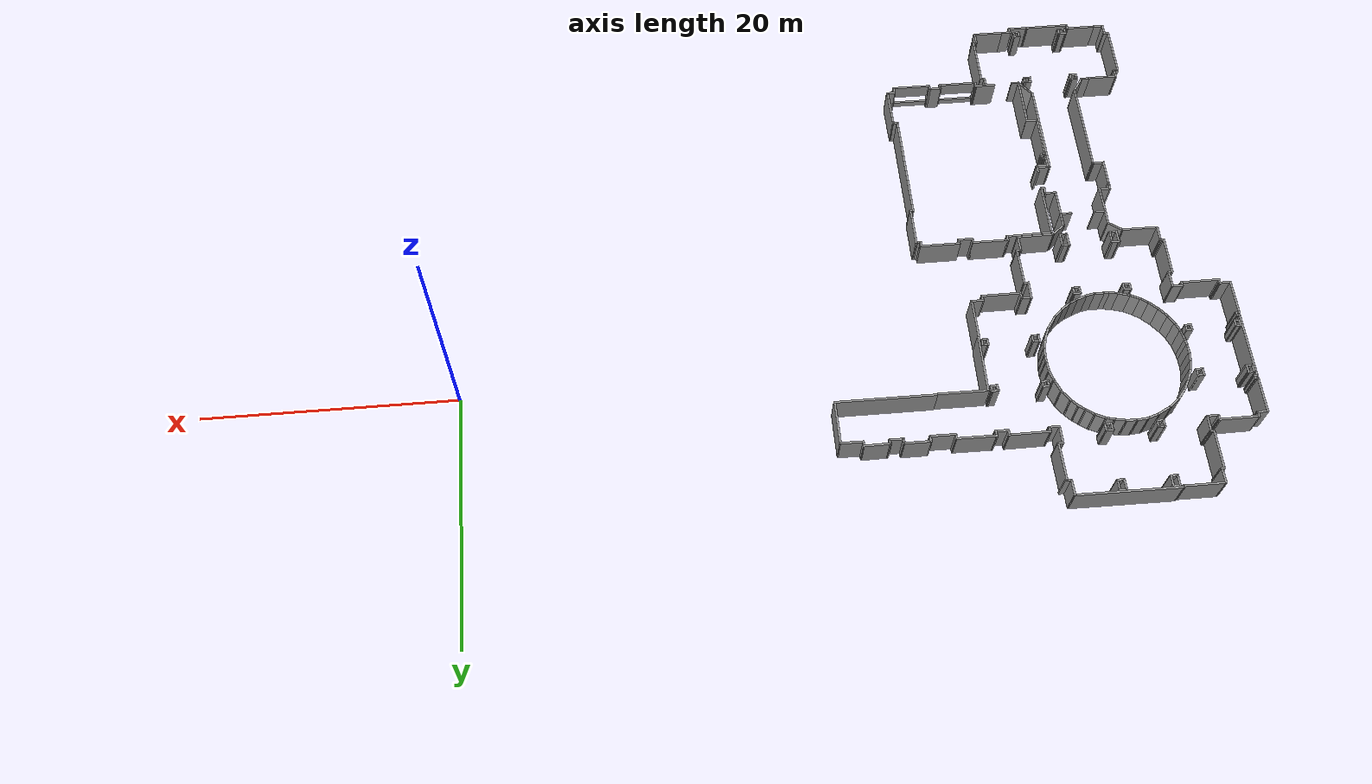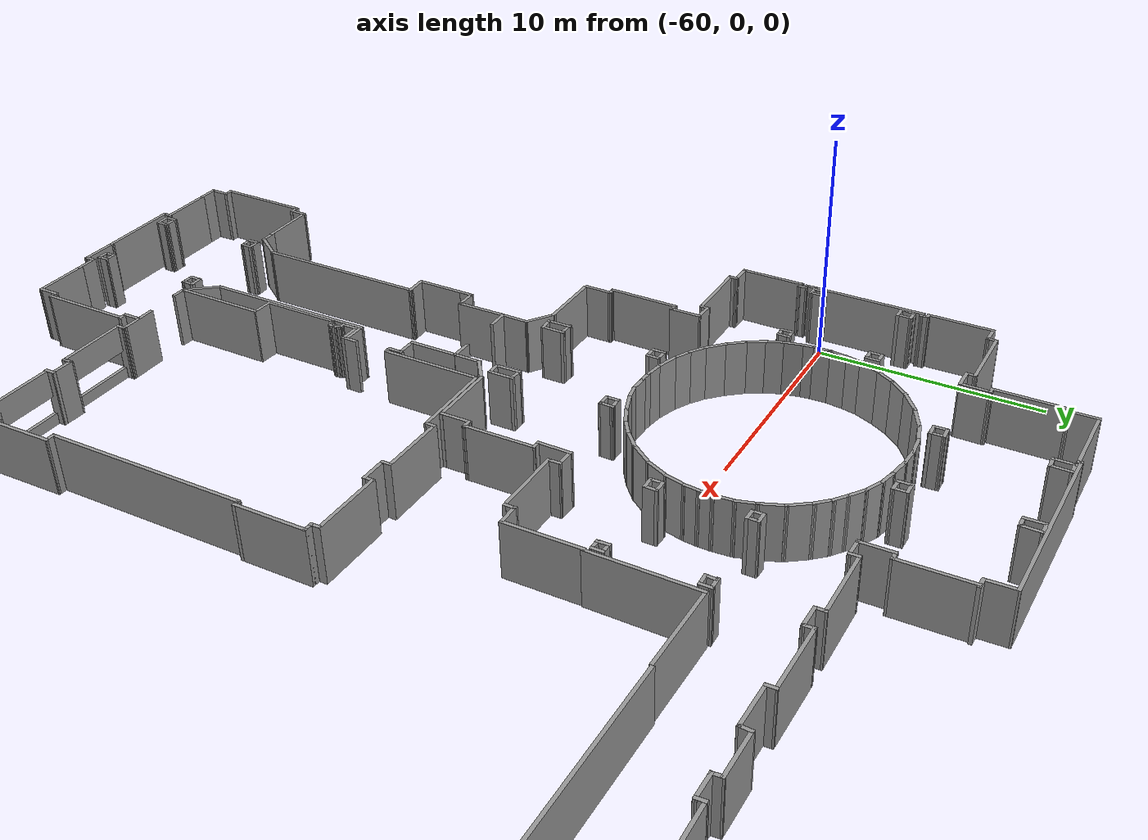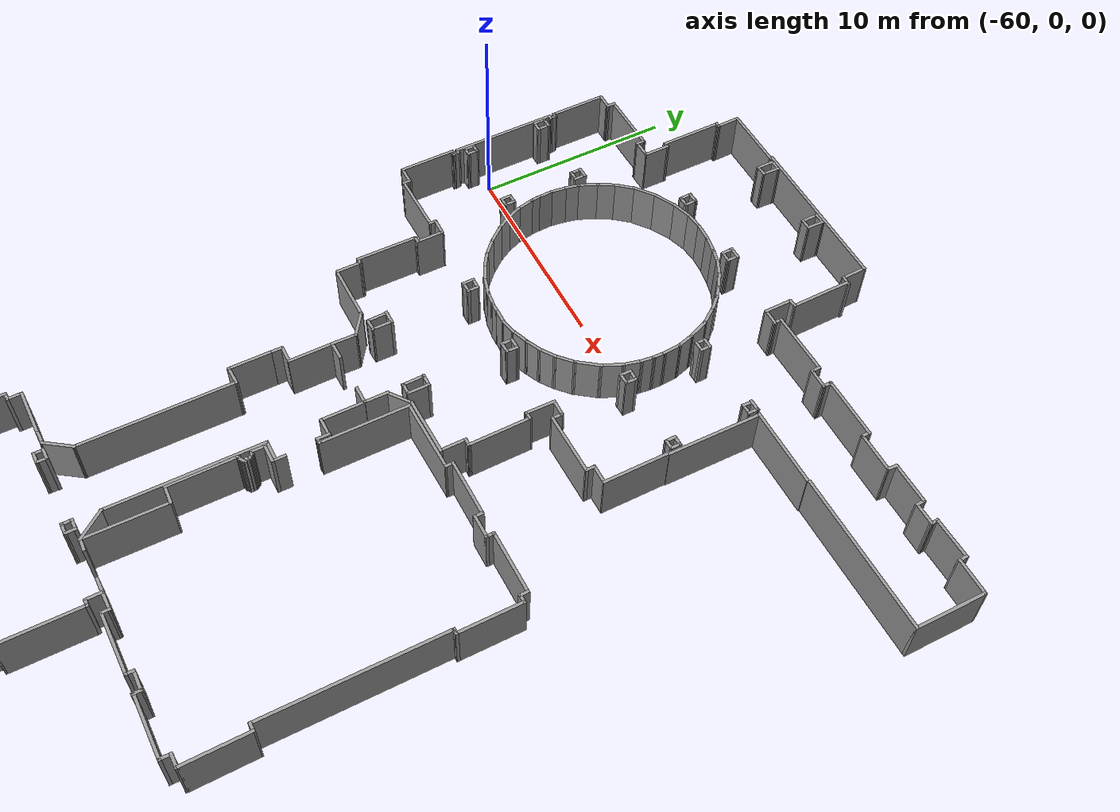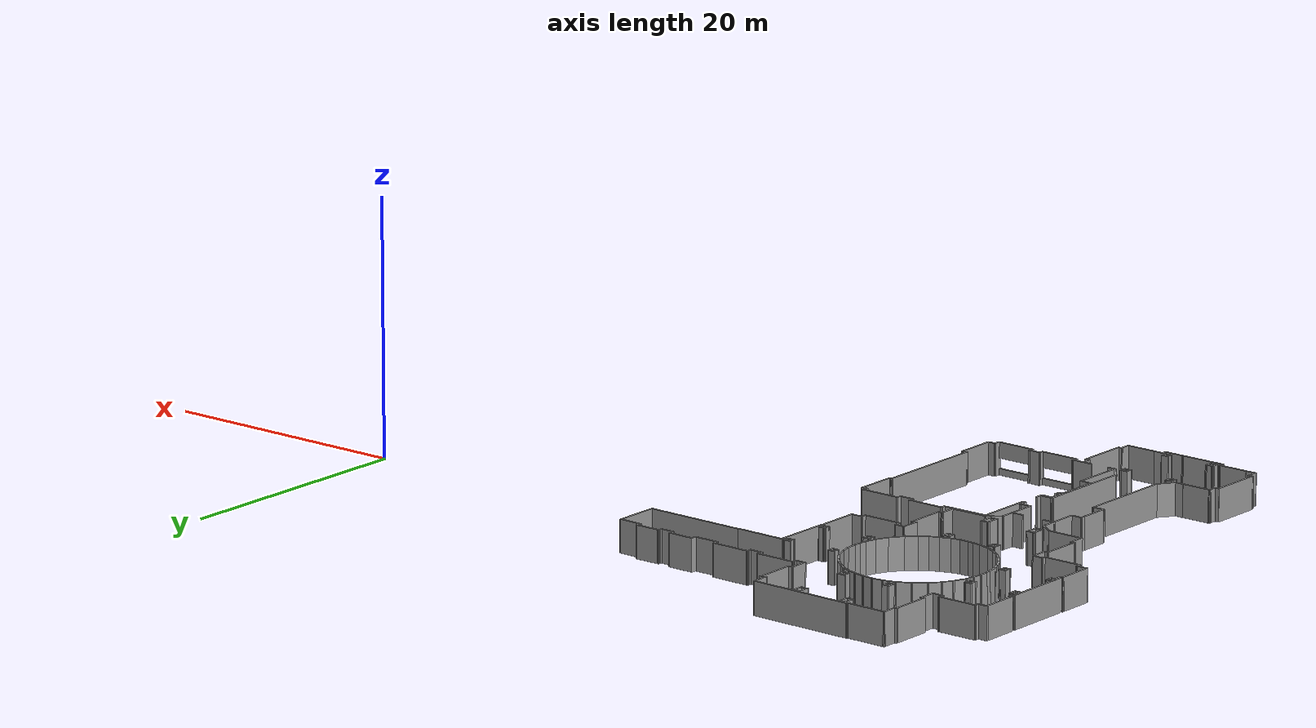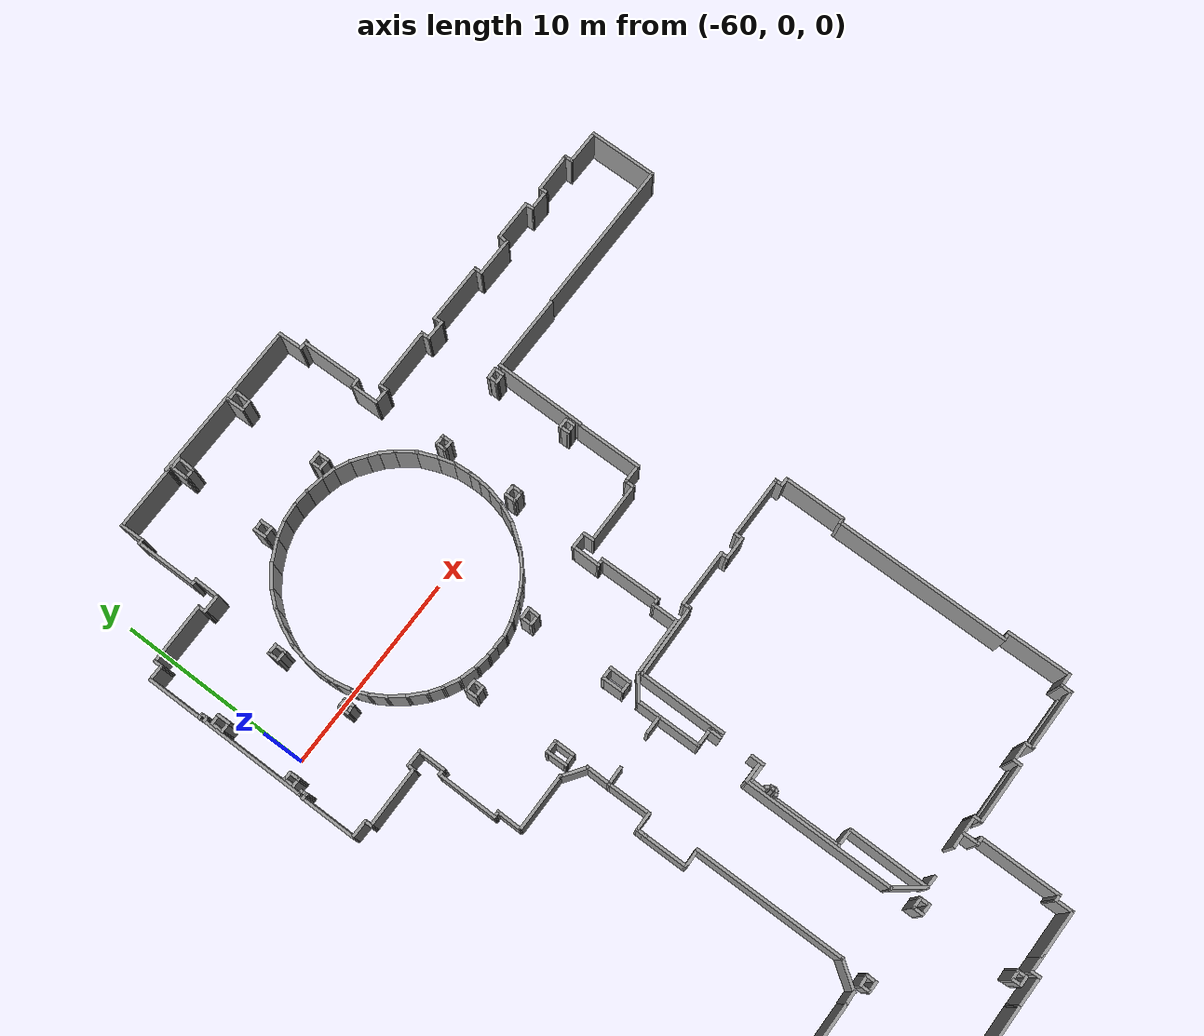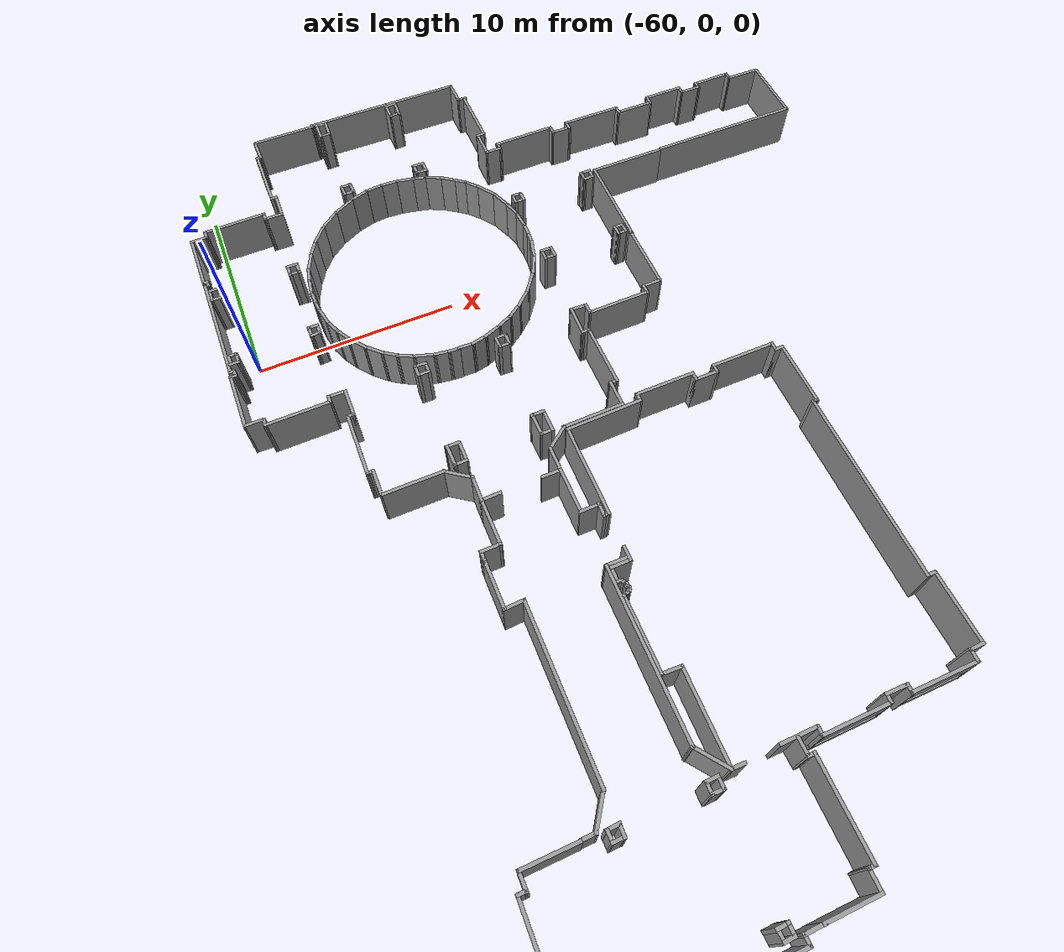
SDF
<?xml version='1.0'?>
<sdf version='1.7'>
  <model name='TD_n1'>
    <pose>-30.6319 -9.22369 0 0 -0 0</pose>
    <link name='Door_3'>
      <collision name='Door_3_Collision'>
        <geometry>
          <box>
            <size>0 0.2 0</size>
          </box>
        </geometry>
        <pose>0 0 0 0 -0 0</pose>
      </collision>
      <visual name='Door_3_Visual'>
        <pose>0 0 0 0 -0 0</pose>
        <geometry>
          <box>
            <size>0 0.2 0</size>
          </box>
        </geometry>
        <material>
          <script>
            <uri>file://media/materials/scripts/gazebo.material</uri>
            <name>Gazebo/Grey</name>
          </script>
        </material>
      </visual>
      <pose>30.6319 9.22369 0 0 0 -0.001641</pose>
    </link>
    <link name='Wall_1'>
      <collision name='Wall_1_Collision'>
        <geometry>
          <box>
            <size>4.5 0.15 2.5</size>
          </box>
        </geometry>
        <pose>0 0 1.25 0 -0 0</pose>
      </collision>
      <visual name='Wall_1_Visual'>
        <pose>0 0 1.25 0 -0 0</pose>
        <geometry>
          <box>
            <size>4.5 0.15 2.5</size>
          </box>
        </geometry>
        <material>
          <script>
            <uri>file://media/materials/scripts/gazebo.material</uri>
            <name>Gazebo/Grey</name>
          </script>
          <ambient>1 1 1 1</ambient>
        </material>
        <meta>
          <layer>0</layer>
        </meta>
      </visual>
      <pose>-17.3412 -2.97464 0 0 -0 1.5708</pose>
    </link>
    <link name='Wall_10'>
      <collision name='Wall_10_Collision'>
        <geometry>
          <box>
            <size>3.25 0.15 2.5</size>
          </box>
        </geometry>
        <pose>0 0 1.25 0 -0 0</pose>
      </collision>
      <visual name='Wall_10_Visual'>
        <pose>0 0 1.25 0 -0 0</pose>
        <geometry>
          <box>
            <size>3.25 0.15 2.5</size>
          </box>
        </geometry>
        <material>
          <script>
            <uri>file://media/materials/scripts/gazebo.material</uri>
            <name>Gazebo/Grey</name>
          </script>
          <ambient>1 1 1 1</ambient>
        </material>
        <meta>
          <layer>0</layer>
        </meta>
      </visual>
      <pose>-8.21265 -0.375309 0 0 -0 0</pose>
    </link>
    <link name='Wall_101'>
      <collision name='Wall_101_Collision'>
        <geometry>
          <box>
            <size>2.29413 0.15 2.5</size>
          </box>
        </geometry>
        <pose>0 0 1.25 0 -0 0</pose>
      </collision>
      <visual name='Wall_101_Visual'>
        <pose>0 0 1.25 0 -0 0</pose>
        <geometry>
          <box>
            <size>2.29413 0.15 2.5</size>
          </box>
        </geometry>
        <material>
          <script>
            <uri>file://media/materials/scripts/gazebo.material</uri>
            <name>Gazebo/Grey</name>
          </script>
          <ambient>1 1 1 1</ambient>
        </material>
        <meta>
          <layer>0</layer>
        </meta>
      </visual>
      <pose>-22.0867 -3.57127 0 0 -0 -1.56353</pose>
    </link>
    <link name='Wall_102'>
      <collision name='Wall_102_Collision'>
        <geometry>
          <box>
            <size>1 0.15 2.5</size>
          </box>
        </geometry>
        <pose>0 0 1.25 0 -0 0</pose>
      </collision>
      <visual name='Wall_102_Visual'>
        <pose>0 0 1.25 0 -0 0</pose>
        <geometry>
          <box>
            <size>1 0.15 2.5</size>
          </box>
        </geometry>
        <material>
          <script>
            <uri>file://media/materials/scripts/gazebo.material</uri>
            <name>Gazebo/Grey</name>
          </script>
          <ambient>1 1 1 1</ambient>
        </material>
        <meta>
          <layer>0</layer>
        </meta>
      </visual>
      <pose>-22.5096 -4.64307 0 0 -0 3.14159</pose>
    </link>
    <link name='Wall_103'>
      <collision name='Wall_103_Collision'>
        <geometry>
          <box>
            <size>0.618308 0.15 2.5</size>
          </box>
        </geometry>
        <pose>0 0 1.25 0 -0 0</pose>
      </collision>
      <visual name='Wall_103_Visual'>
        <pose>0 0 1.25 0 -0 0</pose>
        <geometry>
          <box>
            <size>0.618308 0.15 2.5</size>
          </box>
        </geometry>
        <material>
          <script>
            <uri>file://media/materials/scripts/gazebo.material</uri>
            <name>Gazebo/Grey</name>
          </script>
          <ambient>1 1 1 1</ambient>
        </material>
        <meta>
          <layer>0</layer>
        </meta>
      </visual>
      <pose>-22.9351 -4.87717 0 0 -0 -1.57296</pose>
    </link>
    <link name='Wall_105'>
      <collision name='Wall_105_Collision'>
        <geometry>
          <box>
            <size>1.02402 0.15 2.5</size>
          </box>
        </geometry>
        <pose>0 0 1.25 0 -0 0</pose>
      </collision>
      <visual name='Wall_105_Visual'>
        <pose>0 0 1.25 0 -0 0</pose>
        <geometry>
          <box>
            <size>1.02402 0.15 2.5</size>
          </box>
        </geometry>
        <material>
          <script>
            <uri>file://media/materials/scripts/gazebo.material</uri>
            <name>Gazebo/Grey</name>
          </script>
          <ambient>1 1 1 1</ambient>
        </material>
        <meta>
          <layer>0</layer>
        </meta>
      </visual>
      <pose>-17.9811 -7.20171 0 0 -0 -0.004481</pose>
    </link>
    <link name='Wall_107'>
      <collision name='Wall_107_Collision'>
        <geometry>
          <box>
            <size>0.226709 0.15 2.5</size>
          </box>
        </geometry>
        <pose>0 0 1.25 0 -0 0</pose>
      </collision>
      <visual name='Wall_107_Visual'>
        <pose>0 0 1.25 0 -0 0</pose>
        <geometry>
          <box>
            <size>0.226709 0.15 2.5</size>
          </box>
        </geometry>
        <material>
          <script>
            <uri>file://media/materials/scripts/gazebo.material</uri>
            <name>Gazebo/Grey</name>
          </script>
          <ambient>1 1 1 1</ambient>
        </material>
        <meta>
          <layer>0</layer>
        </meta>
      </visual>
      <pose>-17.9694 -8.43871 0 0 -0 -2.03444</pose>
    </link>
    <link name='Wall_108'>
      <collision name='Wall_108_Collision'>
        <geometry>
          <box>
            <size>0.314919 0.15 2.5</size>
          </box>
        </geometry>
        <pose>0 0 1.25 0 -0 0</pose>
      </collision>
      <visual name='Wall_108_Visual'>
        <pose>0 0 1.25 0 -0 0</pose>
        <geometry>
          <box>
            <size>0.314919 0.15 2.5</size>
          </box>
        </geometry>
        <material>
          <script>
            <uri>file://media/materials/scripts/gazebo.material</uri>
            <name>Gazebo/Grey</name>
          </script>
          <ambient>1 1 1 1</ambient>
        </material>
        <meta>
          <layer>0</layer>
        </meta>
      </visual>
      <pose>-18.0552 -8.51876 0 0 -0 -2.55359</pose>
    </link>
    <link name='Wall_109'>
      <collision name='Wall_109_Collision'>
        <geometry>
          <box>
            <size>0.259233 0.15 2.5</size>
          </box>
        </geometry>
        <pose>0 0 1.25 0 -0 0</pose>
      </collision>
      <visual name='Wall_109_Visual'>
        <pose>0 0 1.25 0 -0 0</pose>
        <geometry>
          <box>
            <size>0.259233 0.15 2.5</size>
          </box>
        </geometry>
        <material>
          <script>
            <uri>file://media/materials/scripts/gazebo.material</uri>
            <name>Gazebo/Grey</name>
          </script>
          <ambient>1 1 1 1</ambient>
        </material>
        <meta>
          <layer>0</layer>
        </meta>
      </visual>
      <pose>-18.1781 -8.57021 0 0 -0 -3.03672</pose>
    </link>
    <link name='Wall_11'>
      <collision name='Wall_11_Collision'>
        <geometry>
          <box>
            <size>0.5 0.15 2.5</size>
          </box>
        </geometry>
        <pose>0 0 1.25 0 -0 0</pose>
      </collision>
      <visual name='Wall_11_Visual'>
        <pose>0 0 1.25 0 -0 0</pose>
        <geometry>
          <box>
            <size>0.5 0.15 2.5</size>
          </box>
        </geometry>
        <material>
          <script>
            <uri>file://media/materials/scripts/gazebo.material</uri>
            <name>Gazebo/Grey</name>
          </script>
          <ambient>1 1 1 1</ambient>
        </material>
        <meta>
          <layer>0</layer>
        </meta>
      </visual>
      <pose>-6.66265 -0.55031 0 0 -0 -1.5708</pose>
    </link>
    <link name='Wall_111'>
      <collision name='Wall_111_Collision'>
        <geometry>
          <box>
            <size>0.301454 0.15 2.5</size>
          </box>
        </geometry>
        <pose>0 0 1.25 0 -0 0</pose>
      </collision>
      <visual name='Wall_111_Visual'>
        <pose>0 0 1.25 0 -0 0</pose>
        <geometry>
          <box>
            <size>0.301454 0.15 2.5</size>
          </box>
        </geometry>
        <material>
          <script>
            <uri>file://media/materials/scripts/gazebo.material</uri>
            <name>Gazebo/Grey</name>
          </script>
          <ambient>1 1 1 1</ambient>
        </material>
        <meta>
          <layer>0</layer>
        </meta>
      </visual>
      <pose>-18.1983 -8.01072 0 0 -0 -0.141419</pose>
    </link>
    <link name='Wall_112'>
      <collision name='Wall_112_Collision'>
        <geometry>
          <box>
            <size>0.263201 0.15 2.5</size>
          </box>
        </geometry>
        <pose>0 0 1.25 0 -0 0</pose>
      </collision>
      <visual name='Wall_112_Visual'>
        <pose>0 0 1.25 0 -0 0</pose>
        <geometry>
          <box>
            <size>0.263201 0.15 2.5</size>
          </box>
        </geometry>
        <material>
          <script>
            <uri>file://media/materials/scripts/gazebo.material</uri>
            <name>Gazebo/Grey</name>
          </script>
          <ambient>1 1 1 1</ambient>
        </material>
        <meta>
          <layer>0</layer>
        </meta>
      </visual>
      <pose>-18.0838 -8.06135 0 0 -0 -0.785398</pose>
    </link>
    <link name='Wall_113'>
      <collision name='Wall_113_Collision'>
        <geometry>
          <box>
            <size>0.256352 0.15 2.5</size>
          </box>
        </geometry>
        <pose>0 0 1.25 0 -0 0</pose>
      </collision>
      <visual name='Wall_113_Visual'>
        <pose>0 0 1.25 0 -0 0</pose>
        <geometry>
          <box>
            <size>0.256352 0.15 2.5</size>
          </box>
        </geometry>
        <material>
          <script>
            <uri>file://media/materials/scripts/gazebo.material</uri>
            <name>Gazebo/Grey</name>
          </script>
          <ambient>1 1 1 1</ambient>
        </material>
        <meta>
          <layer>0</layer>
        </meta>
      </visual>
      <pose>-18.0123 -8.14426 0 0 -0 -0.938048</pose>
    </link>
    <link name='Wall_114'>
      <collision name='Wall_114_Collision'>
        <geometry>
          <box>
            <size>0.237461 0.15 2.5</size>
          </box>
        </geometry>
        <pose>0 0 1.25 0 -0 0</pose>
      </collision>
      <visual name='Wall_114_Visual'>
        <pose>0 0 1.25 0 -0 0</pose>
        <geometry>
          <box>
            <size>0.237461 0.15 2.5</size>
          </box>
        </geometry>
        <material>
          <script>
            <uri>file://media/materials/scripts/gazebo.material</uri>
            <name>Gazebo/Grey</name>
          </script>
          <ambient>1 1 1 1</ambient>
        </material>
        <meta>
          <layer>0</layer>
        </meta>
      </visual>
      <pose>-17.9723 -8.23002 0 0 -0 -1.3734</pose>
    </link>
    <link name='Wall_116'>
      <collision name='Wall_116_Collision'>
        <geometry>
          <box>
            <size>1.01534 0.15 2.5</size>
          </box>
        </geometry>
        <pose>0 0 1.25 0 -0 0</pose>
      </collision>
      <visual name='Wall_116_Visual'>
        <pose>0 0 1.25 0 -0 0</pose>
        <geometry>
          <box>
            <size>1.01534 0.15 2.5</size>
          </box>
        </geometry>
        <material>
          <script>
            <uri>file://media/materials/scripts/gazebo.material</uri>
            <name>Gazebo/Grey</name>
          </script>
          <ambient>1 1 1 1</ambient>
        </material>
        <meta>
          <layer>0</layer>
        </meta>
      </visual>
      <pose>-22.5071 -7.23995 0 0 -0 -3.10645</pose>
    </link>
    <link name='Wall_117'>
      <collision name='Wall_117_Collision'>
        <geometry>
          <box>
            <size>2.35837 0.15 2.5</size>
          </box>
        </geometry>
        <pose>0 0 1.25 0 -0 0</pose>
      </collision>
      <visual name='Wall_117_Visual'>
        <pose>0 0 1.25 0 -0 0</pose>
        <geometry>
          <box>
            <size>2.35837 0.15 2.5</size>
          </box>
        </geometry>
        <material>
          <script>
            <uri>file://media/materials/scripts/gazebo.material</uri>
            <name>Gazebo/Grey</name>
          </script>
          <ambient>1 1 1 1</ambient>
        </material>
        <meta>
          <layer>0</layer>
        </meta>
      </visual>
      <pose>-22.9404 -6.12055 0 0 -0 1.5714</pose>
    </link>
    <link name='Wall_12'>
      <collision name='Wall_12_Collision'>
        <geometry>
          <box>
            <size>0.5 0.15 2.5</size>
          </box>
        </geometry>
        <pose>0 0 1.25 0 -0 0</pose>
      </collision>
      <visual name='Wall_12_Visual'>
        <pose>0 0 1.25 0 -0 0</pose>
        <geometry>
          <box>
            <size>0.5 0.15 2.5</size>
          </box>
        </geometry>
        <material>
          <script>
            <uri>file://media/materials/scripts/gazebo.material</uri>
            <name>Gazebo/Grey</name>
          </script>
          <ambient>1 1 1 1</ambient>
        </material>
        <meta>
          <layer>0</layer>
        </meta>
      </visual>
      <pose>-6.48765 -0.72531 0 0 -0 0</pose>
    </link>
    <link name='Wall_121'>
      <collision name='Wall_121_Collision'>
        <geometry>
          <box>
            <size>1.00199 0.15 2.5</size>
          </box>
        </geometry>
        <pose>0 0 1.25 0 -0 0</pose>
      </collision>
      <visual name='Wall_121_Visual'>
        <pose>0 0 1.25 0 -0 0</pose>
        <geometry>
          <box>
            <size>1.00199 0.15 2.5</size>
          </box>
        </geometry>
        <material>
          <script>
            <uri>file://media/materials/scripts/gazebo.material</uri>
            <name>Gazebo/Grey</name>
          </script>
          <ambient>1 1 1 1</ambient>
        </material>
        <meta>
          <layer>0</layer>
        </meta>
      </visual>
      <pose>-21.6687 -2.49033 0 0 -0 0.021456</pose>
    </link>
    <link name='Wall_123'>
      <collision name='Wall_123_Collision'>
        <geometry>
          <box>
            <size>1 0.15 2.5</size>
          </box>
        </geometry>
        <pose>0 0 1.25 0 -0 0</pose>
      </collision>
      <visual name='Wall_123_Visual'>
        <pose>0 0 1.25 0 -0 0</pose>
        <geometry>
          <box>
            <size>1 0.15 2.5</size>
          </box>
        </geometry>
        <material>
          <script>
            <uri>file://media/materials/scripts/gazebo.material</uri>
            <name>Gazebo/Grey</name>
          </script>
          <ambient>1 1 1 1</ambient>
        </material>
        <meta>
          <layer>0</layer>
        </meta>
      </visual>
      <pose>-18.8515 -2.5042 0 0 -0 3.14159</pose>
    </link>
    <link name='Wall_125'>
      <collision name='Wall_125_Collision'>
        <geometry>
          <box>
            <size>1.32197 0.15 2.5</size>
          </box>
        </geometry>
        <pose>0 0 1.25 0 -0 0</pose>
      </collision>
      <visual name='Wall_125_Visual'>
        <pose>0 0 1.25 0 -0 0</pose>
        <geometry>
          <box>
            <size>1.32197 0.15 2.5</size>
          </box>
        </geometry>
        <material>
          <script>
            <uri>file://media/materials/scripts/gazebo.material</uri>
            <name>Gazebo/Grey</name>
          </script>
          <ambient>1 1 1 1</ambient>
        </material>
        <meta>
          <layer>0</layer>
        </meta>
      </visual>
      <pose>-22.085 -1.91356 0 0 -0 1.5547</pose>
    </link>
    <link name='Wall_126'>
      <collision name='Wall_126_Collision'>
        <geometry>
          <box>
            <size>1.41589 0.15 2.5</size>
          </box>
        </geometry>
        <pose>0 0 1.25 0 -0 0</pose>
      </collision>
      <visual name='Wall_126_Visual'>
        <pose>0 0 1.25 0 -0 0</pose>
        <geometry>
          <box>
            <size>1.41589 0.15 2.5</size>
          </box>
        </geometry>
        <material>
          <script>
            <uri>file://media/materials/scripts/gazebo.material</uri>
            <name>Gazebo/Grey</name>
          </script>
          <ambient>1 1 1 1</ambient>
        </material>
        <meta>
          <layer>0</layer>
        </meta>
      </visual>
      <pose>-22.5927 -0.962635 0 0 -0 2.52693</pose>
    </link>
    <link name='Wall_127'>
      <collision name='Wall_127_Collision'>
        <geometry>
          <box>
            <size>2.91799 0.15 2.5</size>
          </box>
        </geometry>
        <pose>0 0 1.25 0 -0 0</pose>
      </collision>
      <visual name='Wall_127_Visual'>
        <pose>0 0 1.25 0 -0 0</pose>
        <geometry>
          <box>
            <size>2.91799 0.15 2.5</size>
          </box>
        </geometry>
        <material>
          <script>
            <uri>file://media/materials/scripts/gazebo.material</uri>
            <name>Gazebo/Grey</name>
          </script>
          <ambient>1 1 1 1</ambient>
        </material>
        <meta>
          <layer>0</layer>
        </meta>
      </visual>
      <pose>-24.4938 -0.597625 0 0 -0 3.14159</pose>
    </link>
    <link name='Wall_13'>
      <collision name='Wall_13_Collision'>
        <geometry>
          <box>
            <size>3.25 0.15 2.5</size>
          </box>
        </geometry>
        <pose>0 0 1.25 0 -0 0</pose>
      </collision>
      <visual name='Wall_13_Visual'>
        <pose>0 0 1.25 0 -0 0</pose>
        <geometry>
          <box>
            <size>3.25 0.15 2.5</size>
          </box>
        </geometry>
        <material>
          <script>
            <uri>file://media/materials/scripts/gazebo.material</uri>
            <name>Gazebo/Grey</name>
          </script>
          <ambient>1 1 1 1</ambient>
        </material>
        <meta>
          <layer>0</layer>
        </meta>
      </visual>
      <pose>-6.31265 -2.27531 0 0 -0 -1.5708</pose>
    </link>
    <link name='Wall_130'>
      <collision name='Wall_130_Collision'>
        <geometry>
          <box>
            <size>1.28093 0.15 2.5</size>
          </box>
        </geometry>
        <pose>0 0 1.25 0 -0 0</pose>
      </collision>
      <visual name='Wall_130_Visual'>
        <pose>0 0 1.25 0 -0 0</pose>
        <geometry>
          <box>
            <size>1.28093 0.15 2.5</size>
          </box>
        </geometry>
        <material>
          <script>
            <uri>file://media/materials/scripts/gazebo.material</uri>
            <name>Gazebo/Grey</name>
          </script>
          <ambient>1 1 1 1</ambient>
        </material>
        <meta>
          <layer>0</layer>
        </meta>
      </visual>
      <pose>-18.426 -1.93873 0 0 -0 1.56991</pose>
    </link>
    <link name='Wall_131'>
      <collision name='Wall_131_Collision'>
        <geometry>
          <box>
            <size>1.388 0.15 2.5</size>
          </box>
        </geometry>
        <pose>0 0 1.25 0 -0 0</pose>
      </collision>
      <visual name='Wall_131_Visual'>
        <pose>0 0 1.25 0 -0 0</pose>
        <geometry>
          <box>
            <size>1.388 0.15 2.5</size>
          </box>
        </geometry>
        <material>
          <script>
            <uri>file://media/materials/scripts/gazebo.material</uri>
            <name>Gazebo/Grey</name>
          </script>
          <ambient>1 1 1 1</ambient>
        </material>
        <meta>
          <layer>0</layer>
        </meta>
      </visual>
      <pose>-17.9312 -1.00066 0 0 -0 0.645958</pose>
    </link>
    <link name='Wall_132'>
      <collision name='Wall_132_Collision'>
        <geometry>
          <box>
            <size>3.04028 0.15 2.5</size>
          </box>
        </geometry>
        <pose>0 0 1.25 0 -0 0</pose>
      </collision>
      <visual name='Wall_132_Visual'>
        <pose>0 0 1.25 0 -0 0</pose>
        <geometry>
          <box>
            <size>3.04028 0.15 2.5</size>
          </box>
        </geometry>
        <material>
          <script>
            <uri>file://media/materials/scripts/gazebo.material</uri>
            <name>Gazebo/Grey</name>
          </script>
          <ambient>1 1 1 1</ambient>
        </material>
        <meta>
          <layer>0</layer>
        </meta>
      </visual>
      <pose>-15.992 -0.604314 0 0 -0 0.01642</pose>
    </link>
    <link name='Wall_133'>
      <collision name='Wall_133_Collision'>
        <geometry>
          <box>
            <size>1.3797 0.15 2.5</size>
          </box>
        </geometry>
        <pose>0 0 1.25 0 -0 0</pose>
      </collision>
      <visual name='Wall_133_Visual'>
        <pose>0 0 1.25 0 -0 0</pose>
        <geometry>
          <box>
            <size>1.3797 0.15 2.5</size>
          </box>
        </geometry>
        <material>
          <script>
            <uri>file://media/materials/scripts/gazebo.material</uri>
            <name>Gazebo/Grey</name>
          </script>
          <ambient>1 1 1 1</ambient>
        </material>
        <meta>
          <layer>0</layer>
        </meta>
      </visual>
      <pose>-14.5546 0.034263 0 0 -0 1.5738</pose>
    </link>
    <link name='Wall_136'>
      <collision name='Wall_136_Collision'>
        <geometry>
          <box>
            <size>0.464516 0.15 2.5</size>
          </box>
        </geometry>
        <pose>0 0 1.25 0 -0 0</pose>
      </collision>
      <visual name='Wall_136_Visual'>
        <pose>0 0 1.25 0 -0 0</pose>
        <geometry>
          <box>
            <size>0.464516 0.15 2.5</size>
          </box>
        </geometry>
        <material>
          <script>
            <uri>file://media/materials/scripts/gazebo.material</uri>
            <name>Gazebo/Grey</name>
          </script>
          <ambient>1 1 1 1</ambient>
        </material>
        <meta>
          <layer>0</layer>
        </meta>
      </visual>
      <pose>-14.3992 0.646254 0 0 -0 -0.01818</pose>
    </link>
    <link name='Wall_138'>
      <collision name='Wall_138_Collision'>
        <geometry>
          <box>
            <size>3.20297 0.15 2.5</size>
          </box>
        </geometry>
        <pose>0 0 1.25 0 -0 0</pose>
      </collision>
      <visual name='Wall_138_Visual'>
        <pose>0 0 1.25 0 -0 0</pose>
        <geometry>
          <box>
            <size>3.20297 0.15 2.5</size>
          </box>
        </geometry>
        <material>
          <script>
            <uri>file://media/materials/scripts/gazebo.material</uri>
            <name>Gazebo/Grey</name>
          </script>
          <ambient>1 1 1 1</ambient>
        </material>
        <meta>
          <layer>0</layer>
        </meta>
      </visual>
      <pose>-14.2573 2.1698 0 0 -0 1.5808</pose>
    </link>
    <link name='Wall_139'>
      <collision name='Wall_139_Collision'>
        <geometry>
          <box>
            <size>0.464821 0.15 2.5</size>
          </box>
        </geometry>
        <pose>0 0 1.25 0 -0 0</pose>
      </collision>
      <visual name='Wall_139_Visual'>
        <pose>0 0 1.25 0 -0 0</pose>
        <geometry>
          <box>
            <size>0.464821 0.15 2.5</size>
          </box>
        </geometry>
        <material>
          <script>
            <uri>file://media/materials/scripts/gazebo.material</uri>
            <name>Gazebo/Grey</name>
          </script>
          <ambient>1 1 1 1</ambient>
        </material>
        <meta>
          <layer>0</layer>
        </meta>
      </visual>
      <pose>-14.4299 3.69621 0 0 -0 3.14159</pose>
    </link>
    <link name='Wall_14'>
      <collision name='Wall_14_Collision'>
        <geometry>
          <box>
            <size>0.25 0.15 2.5</size>
          </box>
        </geometry>
        <pose>0 0 1.25 0 -0 0</pose>
      </collision>
      <visual name='Wall_14_Visual'>
        <pose>0 0 1.25 0 -0 0</pose>
        <geometry>
          <box>
            <size>0.25 0.15 2.5</size>
          </box>
        </geometry>
        <material>
          <script>
            <uri>file://media/materials/scripts/gazebo.material</uri>
            <name>Gazebo/Grey</name>
          </script>
          <ambient>1 1 1 1</ambient>
        </material>
        <meta>
          <layer>0</layer>
        </meta>
      </visual>
      <pose>-6.36265 -3.82531 0 0 -0 3.14159</pose>
    </link>
    <link name='Wall_140'>
      <collision name='Wall_140_Collision'>
        <geometry>
          <box>
            <size>1.53183 0.15 2.5</size>
          </box>
        </geometry>
        <pose>0 0 1.25 0 -0 0</pose>
      </collision>
      <visual name='Wall_140_Visual'>
        <pose>0 0 1.25 0 -0 0</pose>
        <geometry>
          <box>
            <size>1.53183 0.15 2.5</size>
          </box>
        </geometry>
        <material>
          <script>
            <uri>file://media/materials/scripts/gazebo.material</uri>
            <name>Gazebo/Grey</name>
          </script>
          <ambient>1 1 1 1</ambient>
        </material>
        <meta>
          <layer>0</layer>
        </meta>
      </visual>
      <pose>-14.5786 4.38707 0 0 -0 1.55814</pose>
    </link>
    <link name='Wall_141'>
      <collision name='Wall_141_Collision'>
        <geometry>
          <box>
            <size>0.902276 0.15 2.5</size>
          </box>
        </geometry>
        <pose>0 0 1.25 0 -0 0</pose>
      </collision>
      <visual name='Wall_141_Visual'>
        <pose>0 0 1.25 0 -0 0</pose>
        <geometry>
          <box>
            <size>0.902276 0.15 2.5</size>
          </box>
        </geometry>
        <material>
          <script>
            <uri>file://media/materials/scripts/gazebo.material</uri>
            <name>Gazebo/Grey</name>
          </script>
          <ambient>1 1 1 1</ambient>
        </material>
        <meta>
          <layer>0</layer>
        </meta>
      </visual>
      <pose>-14.1938 5.06918 0 0 -0 -0.023252</pose>
    </link>
    <link name='Wall_142'>
      <collision name='Wall_142_Collision'>
        <geometry>
          <box>
            <size>0.623525 0.15 2.5</size>
          </box>
        </geometry>
        <pose>0 0 1.25 0 -0 0</pose>
      </collision>
      <visual name='Wall_142_Visual'>
        <pose>0 0 1.25 0 -0 0</pose>
        <geometry>
          <box>
            <size>0.623525 0.15 2.5</size>
          </box>
        </geometry>
        <material>
          <script>
            <uri>file://media/materials/scripts/gazebo.material</uri>
            <name>Gazebo/Grey</name>
          </script>
          <ambient>1 1 1 1</ambient>
        </material>
        <meta>
          <layer>0</layer>
        </meta>
      </visual>
      <pose>-13.809 4.82432 0 0 -0 -1.53378</pose>
    </link>
    <link name='Wall_143'>
      <collision name='Wall_143_Collision'>
        <geometry>
          <box>
            <size>3.21067 0.15 2.5</size>
          </box>
        </geometry>
        <pose>0 0 1.25 0 -0 0</pose>
      </collision>
      <visual name='Wall_143_Visual'>
        <pose>0 0 1.25 0 -0 0</pose>
        <geometry>
          <box>
            <size>3.21067 0.15 2.5</size>
          </box>
        </geometry>
        <material>
          <script>
            <uri>file://media/materials/scripts/gazebo.material</uri>
            <name>Gazebo/Grey</name>
          </script>
          <ambient>1 1 1 1</ambient>
        </material>
        <meta>
          <layer>0</layer>
        </meta>
      </visual>
      <pose>-12.27 4.59859 0 0 -0 0.006783</pose>
    </link>
    <link name='Wall_144'>
      <collision name='Wall_144_Collision'>
        <geometry>
          <box>
            <size>0.546457 0.15 2.5</size>
          </box>
        </geometry>
        <pose>0 0 1.25 0 -0 0</pose>
      </collision>
      <visual name='Wall_144_Visual'>
        <pose>0 0 1.25 0 -0 0</pose>
        <geometry>
          <box>
            <size>0.546457 0.15 2.5</size>
          </box>
        </geometry>
        <material>
          <script>
            <uri>file://media/materials/scripts/gazebo.material</uri>
            <name>Gazebo/Grey</name>
          </script>
          <ambient>1 1 1 1</ambient>
        </material>
        <meta>
          <layer>0</layer>
        </meta>
      </visual>
      <pose>-10.7428 4.80708 0 0 -0 1.56986</pose>
    </link>
    <link name='Wall_145'>
      <collision name='Wall_145_Collision'>
        <geometry>
          <box>
            <size>0.962787 0.15 2.5</size>
          </box>
        </geometry>
        <pose>0 0 1.25 0 -0 0</pose>
      </collision>
      <visual name='Wall_145_Visual'>
        <pose>0 0 1.25 0 -0 0</pose>
        <geometry>
          <box>
            <size>0.962787 0.15 2.5</size>
          </box>
        </geometry>
        <material>
          <script>
            <uri>file://media/materials/scripts/gazebo.material</uri>
            <name>Gazebo/Grey</name>
          </script>
          <ambient>1 1 1 1</ambient>
        </material>
        <meta>
          <layer>0</layer>
        </meta>
      </visual>
      <pose>-10.3362 5.00736 0 0 -0 0.005319</pose>
    </link>
    <link name='Wall_147'>
      <collision name='Wall_147_Collision'>
        <geometry>
          <box>
            <size>3.40145 0.15 2.5</size>
          </box>
        </geometry>
        <pose>0 0 1.25 0 -0 0</pose>
      </collision>
      <visual name='Wall_147_Visual'>
        <pose>0 0 1.25 0 -0 0</pose>
        <geometry>
          <box>
            <size>3.40145 0.15 2.5</size>
          </box>
        </geometry>
        <material>
          <script>
            <uri>file://media/materials/scripts/gazebo.material</uri>
            <name>Gazebo/Grey</name>
          </script>
          <ambient>1 1 1 1</ambient>
        </material>
        <meta>
          <layer>0</layer>
        </meta>
      </visual>
      <pose>-9.85346 6.63743 0 0 -0 1.57312</pose>
    </link>
    <link name='Wall_149'>
      <collision name='Wall_149_Collision'>
        <geometry>
          <box>
            <size>4.73903 0.15 2.5</size>
          </box>
        </geometry>
        <pose>0 0 1.25 0 -0 0</pose>
      </collision>
      <visual name='Wall_149_Visual'>
        <pose>0 0 1.25 0 -0 0</pose>
        <geometry>
          <box>
            <size>4.73903 0.15 2.5</size>
          </box>
        </geometry>
        <material>
          <script>
            <uri>file://media/materials/scripts/gazebo.material</uri>
            <name>Gazebo/Grey</name>
          </script>
          <ambient>1 1 1 1</ambient>
        </material>
        <meta>
          <layer>0</layer>
        </meta>
      </visual>
      <pose>-9.79598 10.5803 0 0 -0 1.5614</pose>
    </link>
    <link name='Wall_15'>
      <collision name='Wall_15_Collision'>
        <geometry>
          <box>
            <size>0.25 0.15 2.5</size>
          </box>
        </geometry>
        <pose>0 0 1.25 0 -0 0</pose>
      </collision>
      <visual name='Wall_15_Visual'>
        <pose>0 0 1.25 0 -0 0</pose>
        <geometry>
          <box>
            <size>0.25 0.15 2.5</size>
          </box>
        </geometry>
        <material>
          <script>
            <uri>file://media/materials/scripts/gazebo.material</uri>
            <name>Gazebo/Grey</name>
          </script>
          <ambient>1 1 1 1</ambient>
        </material>
        <meta>
          <layer>0</layer>
        </meta>
      </visual>
      <pose>-6.46265 -3.82531 0 0 -0 3.14159</pose>
    </link>
    <link name='Wall_151'>
      <collision name='Wall_151_Collision'>
        <geometry>
          <box>
            <size>3.98094 0.15 2.5</size>
          </box>
        </geometry>
        <pose>0 0 1.25 0 -0 0</pose>
      </collision>
      <visual name='Wall_151_Visual'>
        <pose>0 0 1.25 0 -0 0</pose>
        <geometry>
          <box>
            <size>3.98094 0.15 2.5</size>
          </box>
        </geometry>
        <material>
          <script>
            <uri>file://media/materials/scripts/gazebo.material</uri>
            <name>Gazebo/Grey</name>
          </script>
          <ambient>1 1 1 1</ambient>
        </material>
        <meta>
          <layer>0</layer>
        </meta>
      </visual>
      <pose>-7.87045 12.8812 0 0 -0 -0.002626</pose>
    </link>
    <link name='Wall_154'>
      <collision name='Wall_154_Collision'>
        <geometry>
          <box>
            <size>0.587151 0.15 2.5</size>
          </box>
        </geometry>
        <pose>0 0 1.25 0 -0 0</pose>
      </collision>
      <visual name='Wall_154_Visual'>
        <pose>0 0 1.25 0 -0 0</pose>
        <geometry>
          <box>
            <size>0.587151 0.15 2.5</size>
          </box>
        </geometry>
        <material>
          <script>
            <uri>file://media/materials/scripts/gazebo.material</uri>
            <name>Gazebo/Grey</name>
          </script>
          <ambient>1 1 1 1</ambient>
        </material>
        <meta>
          <layer>0</layer>
        </meta>
      </visual>
      <pose>-10.4579 8.69933 0 0 -0 -1.54449</pose>
    </link>
    <link name='Wall_155'>
      <collision name='Wall_155_Collision'>
        <geometry>
          <box>
            <size>0.56416 0.15 2.5</size>
          </box>
        </geometry>
        <pose>0 0 1.25 0 -0 0</pose>
      </collision>
      <visual name='Wall_155_Visual'>
        <pose>0 0 1.25 0 -0 0</pose>
        <geometry>
          <box>
            <size>0.56416 0.15 2.5</size>
          </box>
        </geometry>
        <material>
          <script>
            <uri>file://media/materials/scripts/gazebo.material</uri>
            <name>Gazebo/Grey</name>
          </script>
          <ambient>1 1 1 1</ambient>
        </material>
        <meta>
          <layer>0</layer>
        </meta>
      </visual>
      <pose>-10.2451 8.48658 0 0 -0 0.027771</pose>
    </link>
    <link name='Wall_156'>
      <collision name='Wall_156_Collision'>
        <geometry>
          <box>
            <size>0.575655 0.15 2.5</size>
          </box>
        </geometry>
        <pose>0 0 1.25 0 -0 0</pose>
      </collision>
      <visual name='Wall_156_Visual'>
        <pose>0 0 1.25 0 -0 0</pose>
        <geometry>
          <box>
            <size>0.575655 0.15 2.5</size>
          </box>
        </geometry>
        <material>
          <script>
            <uri>file://media/materials/scripts/gazebo.material</uri>
            <name>Gazebo/Grey</name>
          </script>
          <ambient>1 1 1 1</ambient>
        </material>
        <meta>
          <layer>0</layer>
        </meta>
      </visual>
      <pose>-10.0381 8.70508 0 0 -0 1.5708</pose>
    </link>
    <link name='Wall_159'>
      <collision name='Wall_159_Collision'>
        <geometry>
          <box>
            <size>0.545044 0.15 2.5</size>
          </box>
        </geometry>
        <pose>0 0 1.25 0 -0 0</pose>
      </collision>
      <visual name='Wall_159_Visual'>
        <pose>0 0 1.25 0 -0 0</pose>
        <geometry>
          <box>
            <size>0.545044 0.15 2.5</size>
          </box>
        </geometry>
        <material>
          <script>
            <uri>file://media/materials/scripts/gazebo.material</uri>
            <name>Gazebo/Grey</name>
          </script>
          <ambient>1 1 1 1</ambient>
        </material>
        <meta>
          <layer>0</layer>
        </meta>
      </visual>
      <pose>-10.2661 8.91954 0 0 -0 0.00866</pose>
    </link>
    <link name='Wall_16'>
      <collision name='Wall_16_Collision'>
        <geometry>
          <box>
            <size>0.15 0.15 2.5</size>
          </box>
        </geometry>
        <pose>0 0 1.25 0 -0 0</pose>
      </collision>
      <visual name='Wall_16_Visual'>
        <pose>0 0 1.25 0 -0 0</pose>
        <geometry>
          <box>
            <size>0.15 0.15 2.5</size>
          </box>
        </geometry>
        <material>
          <script>
            <uri>file://media/materials/scripts/gazebo.material</uri>
            <name>Gazebo/Grey</name>
          </script>
          <ambient>1 1 1 1</ambient>
        </material>
        <meta>
          <layer>0</layer>
        </meta>
      </visual>
      <pose>-6.51265 -3.82531 0 0 -0 0</pose>
    </link>
    <link name='Wall_161'>
      <collision name='Wall_161_Collision'>
        <geometry>
          <box>
            <size>0.849768 0.15 2.5</size>
          </box>
        </geometry>
        <pose>0 0 1.25 0 -0 0</pose>
      </collision>
      <visual name='Wall_161_Visual'>
        <pose>0 0 1.25 0 -0 0</pose>
        <geometry>
          <box>
            <size>0.849768 0.15 2.5</size>
          </box>
        </geometry>
        <material>
          <script>
            <uri>file://media/materials/scripts/gazebo.material</uri>
            <name>Gazebo/Grey</name>
          </script>
          <ambient>1 1 1 1</ambient>
        </material>
        <meta>
          <layer>0</layer>
        </meta>
      </visual>
      <pose>-14.6264 -16.3859 0 0 -0 -1.54906</pose>
    </link>
    <link name='Wall_162'>
      <collision name='Wall_162_Collision'>
        <geometry>
          <box>
            <size>0.423758 0.15 2.5</size>
          </box>
        </geometry>
        <pose>0 0 1.25 0 -0 0</pose>
      </collision>
      <visual name='Wall_162_Visual'>
        <pose>0 0 1.25 0 -0 0</pose>
        <geometry>
          <box>
            <size>0.423758 0.15 2.5</size>
          </box>
        </geometry>
        <material>
          <script>
            <uri>file://media/materials/scripts/gazebo.material</uri>
            <name>Gazebo/Grey</name>
          </script>
          <ambient>1 1 1 1</ambient>
        </material>
        <meta>
          <layer>0</layer>
        </meta>
      </visual>
      <pose>-14.4819 -16.7357 0 0 -0 0</pose>
    </link>
    <link name='Wall_163'>
      <collision name='Wall_163_Collision'>
        <geometry>
          <box>
            <size>4.1499 0.15 2.5</size>
          </box>
        </geometry>
        <pose>0 0 1.25 0 -0 0</pose>
      </collision>
      <visual name='Wall_163_Visual'>
        <pose>0 0 1.25 0 -0 0</pose>
        <geometry>
          <box>
            <size>4.1499 0.15 2.5</size>
          </box>
        </geometry>
        <material>
          <script>
            <uri>file://media/materials/scripts/gazebo.material</uri>
            <name>Gazebo/Grey</name>
          </script>
          <ambient>1 1 1 1</ambient>
        </material>
        <meta>
          <layer>0</layer>
        </meta>
      </visual>
      <pose>-14.3451 -18.7357 0 0 -0 -1.5708</pose>
    </link>
    <link name='Wall_164'>
      <collision name='Wall_164_Collision'>
        <geometry>
          <box>
            <size>0.408996 0.15 2.5</size>
          </box>
        </geometry>
        <pose>0 0 1.25 0 -0 0</pose>
      </collision>
      <visual name='Wall_164_Visual'>
        <pose>0 0 1.25 0 -0 0</pose>
        <geometry>
          <box>
            <size>0.408996 0.15 2.5</size>
          </box>
        </geometry>
        <material>
          <script>
            <uri>file://media/materials/scripts/gazebo.material</uri>
            <name>Gazebo/Grey</name>
          </script>
          <ambient>1 1 1 1</ambient>
        </material>
        <meta>
          <layer>0</layer>
        </meta>
      </visual>
      <pose>-14.4743 -20.7432 0 0 -0 -3.08284</pose>
    </link>
    <link name='Wall_165'>
      <collision name='Wall_165_Collision'>
        <geometry>
          <box>
            <size>0.970503 0.15 2.5</size>
          </box>
        </geometry>
        <pose>0 0 1.25 0 -0 0</pose>
      </collision>
      <visual name='Wall_165_Visual'>
        <pose>0 0 1.25 0 -0 0</pose>
        <geometry>
          <box>
            <size>0.970503 0.15 2.5</size>
          </box>
        </geometry>
        <material>
          <script>
            <uri>file://media/materials/scripts/gazebo.material</uri>
            <name>Gazebo/Grey</name>
          </script>
          <ambient>1 1 1 1</ambient>
        </material>
        <meta>
          <layer>0</layer>
        </meta>
      </visual>
      <pose>-14.6036 -21.1609 0 0 -0 -1.57076</pose>
    </link>
    <link name='Wall_166'>
      <collision name='Wall_166_Collision'>
        <geometry>
          <box>
            <size>2.45989 0.15 2.5</size>
          </box>
        </geometry>
        <pose>0 0 1.25 0 -0 0</pose>
      </collision>
      <visual name='Wall_166_Visual'>
        <pose>0 0 1.25 0 -0 0</pose>
        <geometry>
          <box>
            <size>2.45989 0.15 2.5</size>
          </box>
        </geometry>
        <material>
          <script>
            <uri>file://media/materials/scripts/gazebo.material</uri>
            <name>Gazebo/Grey</name>
          </script>
          <ambient>1 1 1 1</ambient>
        </material>
        <meta>
          <layer>0</layer>
        </meta>
      </visual>
      <pose>-15.7585 -21.5681 0 0 -0 3.13912</pose>
    </link>
    <link name='Wall_168'>
      <collision name='Wall_168_Collision'>
        <geometry>
          <box>
            <size>1.00169 0.15 2.5</size>
          </box>
        </geometry>
        <pose>0 0 1.25 0 -0 0</pose>
      </collision>
      <visual name='Wall_168_Visual'>
        <pose>0 0 1.25 0 -0 0</pose>
        <geometry>
          <box>
            <size>1.00169 0.15 2.5</size>
          </box>
        </geometry>
        <material>
          <script>
            <uri>file://media/materials/scripts/gazebo.material</uri>
            <name>Gazebo/Grey</name>
          </script>
          <ambient>1 1 1 1</ambient>
        </material>
        <meta>
          <layer>0</layer>
        </meta>
      </visual>
      <pose>-17.2861 -21.5683 0 0 -0 3.14159</pose>
    </link>
    <link name='Wall_169'>
      <collision name='Wall_169_Collision'>
        <geometry>
          <box>
            <size>0.528448 0.15 2.5</size>
          </box>
        </geometry>
        <pose>0 0 1.25 0 -0 0</pose>
      </collision>
      <visual name='Wall_169_Visual'>
        <pose>0 0 1.25 0 -0 0</pose>
        <geometry>
          <box>
            <size>0.528448 0.15 2.5</size>
          </box>
        </geometry>
        <material>
          <script>
            <uri>file://media/materials/scripts/gazebo.material</uri>
            <name>Gazebo/Grey</name>
          </script>
          <ambient>1 1 1 1</ambient>
        </material>
        <meta>
          <layer>0</layer>
        </meta>
      </visual>
      <pose>-17.7091 -21.7632 0 0 -0 -1.55568</pose>
    </link>
    <link name='Wall_17'>
      <collision name='Wall_17_Collision'>
        <geometry>
          <box>
            <size>0.15 0.15 2.5</size>
          </box>
        </geometry>
        <pose>0 0 1.25 0 -0 0</pose>
      </collision>
      <visual name='Wall_17_Visual'>
        <pose>0 0 1.25 0 -0 0</pose>
        <geometry>
          <box>
            <size>0.15 0.15 2.5</size>
          </box>
        </geometry>
        <material>
          <script>
            <uri>file://media/materials/scripts/gazebo.material</uri>
            <name>Gazebo/Grey</name>
          </script>
          <ambient>1 1 1 1</ambient>
        </material>
        <meta>
          <layer>0</layer>
        </meta>
      </visual>
      <pose>-6.51265 -3.82531 0 0 -0 0</pose>
    </link>
    <link name='Wall_170'>
      <collision name='Wall_170_Collision'>
        <geometry>
          <box>
            <size>1.70137 0.15 2.5</size>
          </box>
        </geometry>
        <pose>0 0 1.25 0 -0 0</pose>
      </collision>
      <visual name='Wall_170_Visual'>
        <pose>0 0 1.25 0 -0 0</pose>
        <geometry>
          <box>
            <size>1.70137 0.15 2.5</size>
          </box>
        </geometry>
        <material>
          <script>
            <uri>file://media/materials/scripts/gazebo.material</uri>
            <name>Gazebo/Grey</name>
          </script>
          <ambient>1 1 1 1</ambient>
        </material>
        <meta>
          <layer>0</layer>
        </meta>
      </visual>
      <pose>-18.4818 -21.9447 0 0 -0 3.13179</pose>
    </link>
    <link name='Wall_171'>
      <collision name='Wall_171_Collision'>
        <geometry>
          <box>
            <size>3.69377 0.15 2.5</size>
          </box>
        </geometry>
        <pose>0 0 1.25 0 -0 0</pose>
      </collision>
      <visual name='Wall_171_Visual'>
        <pose>0 0 1.25 0 -0 0</pose>
        <geometry>
          <box>
            <size>3.69377 0.15 2.5</size>
          </box>
        </geometry>
        <material>
          <script>
            <uri>file://media/materials/scripts/gazebo.material</uri>
            <name>Gazebo/Grey</name>
          </script>
          <ambient>1 1 1 1</ambient>
        </material>
        <meta>
          <layer>0</layer>
        </meta>
      </visual>
      <pose>-21.0293 -21.9447 0 0 -0 -3.1373</pose>
    </link>
    <link name='Wall_173'>
      <collision name='Wall_173_Collision'>
        <geometry>
          <box>
            <size>0.485582 0.15 2.5</size>
          </box>
        </geometry>
        <pose>0 0 1.25 0 -0 0</pose>
      </collision>
      <visual name='Wall_173_Visual'>
        <pose>0 0 1.25 0 -0 0</pose>
        <geometry>
          <box>
            <size>0.485582 0.15 2.5</size>
          </box>
        </geometry>
        <material>
          <script>
            <uri>file://media/materials/scripts/gazebo.material</uri>
            <name>Gazebo/Grey</name>
          </script>
          <ambient>1 1 1 1</ambient>
        </material>
        <meta>
          <layer>0</layer>
        </meta>
      </visual>
      <pose>-22.7945 -21.7846 0 0 -0 1.53123</pose>
    </link>
    <link name='Wall_174'>
      <collision name='Wall_174_Collision'>
        <geometry>
          <box>
            <size>2.42321 0.15 2.5</size>
          </box>
        </geometry>
        <pose>0 0 1.25 0 -0 0</pose>
      </collision>
      <visual name='Wall_174_Visual'>
        <pose>0 0 1.25 0 -0 0</pose>
        <geometry>
          <box>
            <size>2.42321 0.15 2.5</size>
          </box>
        </geometry>
        <material>
          <script>
            <uri>file://media/materials/scripts/gazebo.material</uri>
            <name>Gazebo/Grey</name>
          </script>
          <ambient>1 1 1 1</ambient>
        </material>
        <meta>
          <layer>0</layer>
        </meta>
      </visual>
      <pose>-23.9244 -21.614 0 0 -0 3.13897</pose>
    </link>
    <link name='Wall_176'>
      <collision name='Wall_176_Collision'>
        <geometry>
          <box>
            <size>0.956725 0.15 2.5</size>
          </box>
        </geometry>
        <pose>0 0 1.25 0 -0 0</pose>
      </collision>
      <visual name='Wall_176_Visual'>
        <pose>0 0 1.25 0 -0 0</pose>
        <geometry>
          <box>
            <size>0.956725 0.15 2.5</size>
          </box>
        </geometry>
        <material>
          <script>
            <uri>file://media/materials/scripts/gazebo.material</uri>
            <name>Gazebo/Grey</name>
          </script>
          <ambient>1 1 1 1</ambient>
        </material>
        <meta>
          <layer>0</layer>
        </meta>
      </visual>
      <pose>-25.5056 -21.617 0 0 -0 3.14159</pose>
    </link>
    <link name='Wall_177'>
      <collision name='Wall_177_Collision'>
        <geometry>
          <box>
            <size>0.96258 0.15 2.5</size>
          </box>
        </geometry>
        <pose>0 0 1.25 0 -0 0</pose>
      </collision>
      <visual name='Wall_177_Visual'>
        <pose>0 0 1.25 0 -0 0</pose>
        <geometry>
          <box>
            <size>0.96258 0.15 2.5</size>
          </box>
        </geometry>
        <material>
          <script>
            <uri>file://media/materials/scripts/gazebo.material</uri>
            <name>Gazebo/Grey</name>
          </script>
          <ambient>1 1 1 1</ambient>
        </material>
        <meta>
          <layer>0</layer>
        </meta>
      </visual>
      <pose>-25.9102 -21.2107 0 0 -0 1.5739</pose>
    </link>
    <link name='Wall_178'>
      <collision name='Wall_178_Collision'>
        <geometry>
          <box>
            <size>0.471574 0.15 2.5</size>
          </box>
        </geometry>
        <pose>0 0 1.25 0 -0 0</pose>
      </collision>
      <visual name='Wall_178_Visual'>
        <pose>0 0 1.25 0 -0 0</pose>
        <geometry>
          <box>
            <size>0.471574 0.15 2.5</size>
          </box>
        </geometry>
        <material>
          <script>
            <uri>file://media/materials/scripts/gazebo.material</uri>
            <name>Gazebo/Grey</name>
          </script>
          <ambient>1 1 1 1</ambient>
        </material>
        <meta>
          <layer>0</layer>
        </meta>
      </visual>
      <pose>-26.0722 -20.8048 0 0 -0 -3.13885</pose>
    </link>
    <link name='Wall_179'>
      <collision name='Wall_179_Collision'>
        <geometry>
          <box>
            <size>4.22515 0.15 2.5</size>
          </box>
        </geometry>
        <pose>0 0 1.25 0 -0 0</pose>
      </collision>
      <visual name='Wall_179_Visual'>
        <pose>0 0 1.25 0 -0 0</pose>
        <geometry>
          <box>
            <size>4.22515 0.15 2.5</size>
          </box>
        </geometry>
        <material>
          <script>
            <uri>file://media/materials/scripts/gazebo.material</uri>
            <name>Gazebo/Grey</name>
          </script>
          <ambient>1 1 1 1</ambient>
        </material>
        <meta>
          <layer>0</layer>
        </meta>
      </visual>
      <pose>-26.2214 -18.7677 0 0 -0 1.56516</pose>
    </link>
    <link name='Wall_180'>
      <collision name='Wall_180_Collision'>
        <geometry>
          <box>
            <size>0.46112 0.15 2.5</size>
          </box>
        </geometry>
        <pose>0 0 1.25 0 -0 0</pose>
      </collision>
      <visual name='Wall_180_Visual'>
        <pose>0 0 1.25 0 -0 0</pose>
        <geometry>
          <box>
            <size>0.46112 0.15 2.5</size>
          </box>
        </geometry>
        <material>
          <script>
            <uri>file://media/materials/scripts/gazebo.material</uri>
            <name>Gazebo/Grey</name>
          </script>
          <ambient>1 1 1 1</ambient>
        </material>
        <meta>
          <layer>0</layer>
        </meta>
      </visual>
      <pose>-26.0429 -16.7211 0 0 -0 -0.015022</pose>
    </link>
    <link name='Wall_181'>
      <collision name='Wall_181_Collision'>
        <geometry>
          <box>
            <size>0.827764 0.15 2.5</size>
          </box>
        </geometry>
        <pose>0 0 1.25 0 -0 0</pose>
      </collision>
      <visual name='Wall_181_Visual'>
        <pose>0 0 1.25 0 -0 0</pose>
        <geometry>
          <box>
            <size>0.827764 0.15 2.5</size>
          </box>
        </geometry>
        <material>
          <script>
            <uri>file://media/materials/scripts/gazebo.material</uri>
            <name>Gazebo/Grey</name>
          </script>
          <ambient>1 1 1 1</ambient>
        </material>
        <meta>
          <layer>0</layer>
        </meta>
      </visual>
      <pose>-25.894 -16.3846 0 0 -0 1.57564</pose>
    </link>
    <link name='Wall_182'>
      <collision name='Wall_182_Collision'>
        <geometry>
          <box>
            <size>2.5 0.15 2.5</size>
          </box>
        </geometry>
        <pose>0 0 1.25 0 -0 0</pose>
      </collision>
      <visual name='Wall_182_Visual'>
        <pose>0 0 1.25 0 -0 0</pose>
        <geometry>
          <box>
            <size>2.5 0.15 2.5</size>
          </box>
        </geometry>
        <material>
          <script>
            <uri>file://media/materials/scripts/gazebo.material</uri>
            <name>Gazebo/Grey</name>
          </script>
          <ambient>1 1 1 1</ambient>
        </material>
        <meta>
          <layer>0</layer>
        </meta>
      </visual>
      <pose>-24.7206 -16.0457 0 0 -0 0</pose>
    </link>
    <link name='Wall_184'>
      <collision name='Wall_184_Collision'>
        <geometry>
          <box>
            <size>0.716681 0.15 2.5</size>
          </box>
        </geometry>
        <pose>0 0 1.25 0 -0 0</pose>
      </collision>
      <visual name='Wall_184_Visual'>
        <pose>0 0 1.25 0 -0 0</pose>
        <geometry>
          <box>
            <size>0.716681 0.15 2.5</size>
          </box>
        </geometry>
        <material>
          <script>
            <uri>file://media/materials/scripts/gazebo.material</uri>
            <name>Gazebo/Grey</name>
          </script>
          <ambient>1 1 1 1</ambient>
        </material>
        <meta>
          <layer>0</layer>
        </meta>
      </visual>
      <pose>-22.2489 -21.0909 0 0 -0 0.000724</pose>
    </link>
    <link name='Wall_185'>
      <collision name='Wall_185_Collision'>
        <geometry>
          <box>
            <size>0.60367 0.15 2.5</size>
          </box>
        </geometry>
        <pose>0 0 1.25 0 -0 0</pose>
      </collision>
      <visual name='Wall_185_Visual'>
        <pose>0 0 1.25 0 -0 0</pose>
        <geometry>
          <box>
            <size>0.60367 0.15 2.5</size>
          </box>
        </geometry>
        <material>
          <script>
            <uri>file://media/materials/scripts/gazebo.material</uri>
            <name>Gazebo/Grey</name>
          </script>
          <ambient>1 1 1 1</ambient>
        </material>
        <meta>
          <layer>0</layer>
        </meta>
      </visual>
      <pose>-21.9681 -21.3175 0 0 -0 -1.58213</pose>
    </link>
    <link name='Wall_186'>
      <collision name='Wall_186_Collision'>
        <geometry>
          <box>
            <size>0.682391 0.15 2.5</size>
          </box>
        </geometry>
        <pose>0 0 1.25 0 -0 0</pose>
      </collision>
      <visual name='Wall_186_Visual'>
        <pose>0 0 1.25 0 -0 0</pose>
        <geometry>
          <box>
            <size>0.682391 0.15 2.5</size>
          </box>
        </geometry>
        <material>
          <script>
            <uri>file://media/materials/scripts/gazebo.material</uri>
            <name>Gazebo/Grey</name>
          </script>
          <ambient>1 1 1 1</ambient>
        </material>
        <meta>
          <layer>0</layer>
        </meta>
      </visual>
      <pose>-22.2369 -21.5548 0 0 -0 -3.12379</pose>
    </link>
    <link name='Wall_188'>
      <collision name='Wall_188_Collision'>
        <geometry>
          <box>
            <size>0.572734 0.15 2.5</size>
          </box>
        </geometry>
        <pose>0 0 1.25 0 -0 0</pose>
      </collision>
      <visual name='Wall_188_Visual'>
        <pose>0 0 1.25 0 -0 0</pose>
        <geometry>
          <box>
            <size>0.572734 0.15 2.5</size>
          </box>
        </geometry>
        <material>
          <script>
            <uri>file://media/materials/scripts/gazebo.material</uri>
            <name>Gazebo/Grey</name>
          </script>
          <ambient>1 1 1 1</ambient>
        </material>
        <meta>
          <layer>0</layer>
        </meta>
      </visual>
      <pose>-22.529 -21.3024 0 0 -0 -1.5558</pose>
    </link>
    <link name='Wall_19'>
      <collision name='Wall_19_Collision'>
        <geometry>
          <box>
            <size>9 0.15 2.5</size>
          </box>
        </geometry>
        <pose>0 0 1.25 0 -0 0</pose>
      </collision>
      <visual name='Wall_19_Visual'>
        <pose>0 0 1.25 0 -0 0</pose>
        <geometry>
          <box>
            <size>9 0.15 2.5</size>
          </box>
        </geometry>
        <material>
          <script>
            <uri>file://media/materials/scripts/gazebo.material</uri>
            <name>Gazebo/Grey</name>
          </script>
          <ambient>1 1 1 1</ambient>
        </material>
        <meta>
          <layer>0</layer>
        </meta>
      </visual>
      <pose>-6.51265 -8.25031 0 0 -0 -1.5708</pose>
    </link>
    <link name='Wall_190'>
      <collision name='Wall_190_Collision'>
        <geometry>
          <box>
            <size>0.593564 0.15 2.5</size>
          </box>
        </geometry>
        <pose>0 0 1.25 0 -0 0</pose>
      </collision>
      <visual name='Wall_190_Visual'>
        <pose>0 0 1.25 0 -0 0</pose>
        <geometry>
          <box>
            <size>0.593564 0.15 2.5</size>
          </box>
        </geometry>
        <material>
          <script>
            <uri>file://media/materials/scripts/gazebo.material</uri>
            <name>Gazebo/Grey</name>
          </script>
          <ambient>1 1 1 1</ambient>
        </material>
        <meta>
          <layer>0</layer>
        </meta>
      </visual>
      <pose>-18.2588 -21.0755 0 0 -0 0.019605</pose>
    </link>
    <link name='Wall_191'>
      <collision name='Wall_191_Collision'>
        <geometry>
          <box>
            <size>0.576176 0.15 2.5</size>
          </box>
        </geometry>
        <pose>0 0 1.25 0 -0 0</pose>
      </collision>
      <visual name='Wall_191_Visual'>
        <pose>0 0 1.25 0 -0 0</pose>
        <geometry>
          <box>
            <size>0.576176 0.15 2.5</size>
          </box>
        </geometry>
        <material>
          <script>
            <uri>file://media/materials/scripts/gazebo.material</uri>
            <name>Gazebo/Grey</name>
          </script>
          <ambient>1 1 1 1</ambient>
        </material>
        <meta>
          <layer>0</layer>
        </meta>
      </visual>
      <pose>-18.0327 -21.2842 0 0 -0 -1.55039</pose>
    </link>
    <link name='Wall_192'>
      <collision name='Wall_192_Collision'>
        <geometry>
          <box>
            <size>0.567753 0.15 2.5</size>
          </box>
        </geometry>
        <pose>0 0 1.25 0 -0 0</pose>
      </collision>
      <visual name='Wall_192_Visual'>
        <pose>0 0 1.25 0 -0 0</pose>
        <geometry>
          <box>
            <size>0.567753 0.15 2.5</size>
          </box>
        </geometry>
        <material>
          <script>
            <uri>file://media/materials/scripts/gazebo.material</uri>
            <name>Gazebo/Grey</name>
          </script>
          <ambient>1 1 1 1</ambient>
        </material>
        <meta>
          <layer>0</layer>
        </meta>
      </visual>
      <pose>-18.237 -21.5016 0 0 -0 -3.12076</pose>
    </link>
    <link name='Wall_193'>
      <collision name='Wall_193_Collision'>
        <geometry>
          <box>
            <size>0.515631 0.15 2.5</size>
          </box>
        </geometry>
        <pose>0 0 1.25 0 -0 0</pose>
      </collision>
      <visual name='Wall_193_Visual'>
        <pose>0 0 1.25 0 -0 0</pose>
        <geometry>
          <box>
            <size>0.515631 0.15 2.5</size>
          </box>
        </geometry>
        <material>
          <script>
            <uri>file://media/materials/scripts/gazebo.material</uri>
            <name>Gazebo/Grey</name>
          </script>
          <ambient>1 1 1 1</ambient>
        </material>
        <meta>
          <layer>0</layer>
        </meta>
      </visual>
      <pose>-18.4544 -21.3234 0 0 -0 1.61838</pose>
    </link>
    <link name='Wall_195'>
      <collision name='Wall_195_Collision'>
        <geometry>
          <box>
            <size>0.656131 0.15 2.5</size>
          </box>
        </geometry>
        <pose>0 0 1.25 0 -0 0</pose>
      </collision>
      <visual name='Wall_195_Visual'>
        <pose>0 0 1.25 0 -0 0</pose>
        <geometry>
          <box>
            <size>0.656131 0.15 2.5</size>
          </box>
        </geometry>
        <material>
          <script>
            <uri>file://media/materials/scripts/gazebo.material</uri>
            <name>Gazebo/Grey</name>
          </script>
          <ambient>1 1 1 1</ambient>
        </material>
        <meta>
          <layer>0</layer>
        </meta>
      </visual>
      <pose>-22.2679 -16.0785 0 0 -0 0.022723</pose>
    </link>
    <link name='Wall_196'>
      <collision name='Wall_196_Collision'>
        <geometry>
          <box>
            <size>0.606531 0.15 2.5</size>
          </box>
        </geometry>
        <pose>0 0 1.25 0 -0 0</pose>
      </collision>
      <visual name='Wall_196_Visual'>
        <pose>0 0 1.25 0 -0 0</pose>
        <geometry>
          <box>
            <size>0.606531 0.15 2.5</size>
          </box>
        </geometry>
        <material>
          <script>
            <uri>file://media/materials/scripts/gazebo.material</uri>
            <name>Gazebo/Grey</name>
          </script>
          <ambient>1 1 1 1</ambient>
        </material>
        <meta>
          <layer>0</layer>
        </meta>
      </visual>
      <pose>-22.0328 -16.301 0 0 -0 -1.57267</pose>
    </link>
    <link name='Wall_197'>
      <collision name='Wall_197_Collision'>
        <geometry>
          <box>
            <size>0.623737 0.15 2.5</size>
          </box>
        </geometry>
        <pose>0 0 1.25 0 -0 0</pose>
      </collision>
      <visual name='Wall_197_Visual'>
        <pose>0 0 1.25 0 -0 0</pose>
        <geometry>
          <box>
            <size>0.623737 0.15 2.5</size>
          </box>
        </geometry>
        <material>
          <script>
            <uri>file://media/materials/scripts/gazebo.material</uri>
            <name>Gazebo/Grey</name>
          </script>
          <ambient>1 1 1 1</ambient>
        </material>
        <meta>
          <layer>0</layer>
        </meta>
      </visual>
      <pose>-22.2701 -16.5281 0 0 -0 3.13662</pose>
    </link>
    <link name='Wall_198'>
      <collision name='Wall_198_Collision'>
        <geometry>
          <box>
            <size>0.547671 0.15 2.5</size>
          </box>
        </geometry>
        <pose>0 0 1.25 0 -0 0</pose>
      </collision>
      <visual name='Wall_198_Visual'>
        <pose>0 0 1.25 0 -0 0</pose>
        <geometry>
          <box>
            <size>0.547671 0.15 2.5</size>
          </box>
        </geometry>
        <material>
          <script>
            <uri>file://media/materials/scripts/gazebo.material</uri>
            <name>Gazebo/Grey</name>
          </script>
          <ambient>1 1 1 1</ambient>
        </material>
        <meta>
          <layer>0</layer>
        </meta>
      </visual>
      <pose>-22.5092 -16.3281 0 0 -0 1.58219</pose>
    </link>
    <link name='Wall_20'>
      <collision name='Wall_20_Collision'>
        <geometry>
          <box>
            <size>0.5 0.15 2.5</size>
          </box>
        </geometry>
        <pose>0 0 1.25 0 -0 0</pose>
      </collision>
      <visual name='Wall_20_Visual'>
        <pose>0 0 1.25 0 -0 0</pose>
        <geometry>
          <box>
            <size>0.5 0.15 2.5</size>
          </box>
        </geometry>
        <material>
          <script>
            <uri>file://media/materials/scripts/gazebo.material</uri>
            <name>Gazebo/Grey</name>
          </script>
          <ambient>1 1 1 1</ambient>
        </material>
        <meta>
          <layer>0</layer>
        </meta>
      </visual>
      <pose>-6.33765 -12.6753 0 0 -0 0</pose>
    </link>
    <link name='Wall_200'>
      <collision name='Wall_200_Collision'>
        <geometry>
          <box>
            <size>0.630437 0.15 2.5</size>
          </box>
        </geometry>
        <pose>0 0 1.25 0 -0 0</pose>
      </collision>
      <visual name='Wall_200_Visual'>
        <pose>0 0 1.25 0 -0 0</pose>
        <geometry>
          <box>
            <size>0.630437 0.15 2.5</size>
          </box>
        </geometry>
        <material>
          <script>
            <uri>file://media/materials/scripts/gazebo.material</uri>
            <name>Gazebo/Grey</name>
          </script>
          <ambient>1 1 1 1</ambient>
        </material>
        <meta>
          <layer>0</layer>
        </meta>
      </visual>
      <pose>-18.269 -16.0509 0 0 -0 0.005917</pose>
    </link>
    <link name='Wall_201'>
      <collision name='Wall_201_Collision'>
        <geometry>
          <box>
            <size>0.616199 0.15 2.5</size>
          </box>
        </geometry>
        <pose>0 0 1.25 0 -0 0</pose>
      </collision>
      <visual name='Wall_201_Visual'>
        <pose>0 0 1.25 0 -0 0</pose>
        <geometry>
          <box>
            <size>0.616199 0.15 2.5</size>
          </box>
        </geometry>
        <material>
          <script>
            <uri>file://media/materials/scripts/gazebo.material</uri>
            <name>Gazebo/Grey</name>
          </script>
          <ambient>1 1 1 1</ambient>
        </material>
        <meta>
          <layer>0</layer>
        </meta>
      </visual>
      <pose>-18.0274 -16.2825 0 0 -0 -1.5647</pose>
    </link>
    <link name='Wall_202'>
      <collision name='Wall_202_Collision'>
        <geometry>
          <box>
            <size>0.638964 0.15 2.5</size>
          </box>
        </geometry>
        <pose>0 0 1.25 0 -0 0</pose>
      </collision>
      <visual name='Wall_202_Visual'>
        <pose>0 0 1.25 0 -0 0</pose>
        <geometry>
          <box>
            <size>0.638964 0.15 2.5</size>
          </box>
        </geometry>
        <material>
          <script>
            <uri>file://media/materials/scripts/gazebo.material</uri>
            <name>Gazebo/Grey</name>
          </script>
          <ambient>1 1 1 1</ambient>
        </material>
        <meta>
          <layer>0</layer>
        </meta>
      </visual>
      <pose>-18.2704 -16.5128 0 0 -0 3.12996</pose>
    </link>
    <link name='Wall_203'>
      <collision name='Wall_203_Collision'>
        <geometry>
          <box>
            <size>0.593449 0.15 2.5</size>
          </box>
        </geometry>
        <pose>0 0 1.25 0 -0 0</pose>
      </collision>
      <visual name='Wall_203_Visual'>
        <pose>0 0 1.25 0 -0 0</pose>
        <geometry>
          <box>
            <size>0.593449 0.15 2.5</size>
          </box>
        </geometry>
        <material>
          <script>
            <uri>file://media/materials/scripts/gazebo.material</uri>
            <name>Gazebo/Grey</name>
          </script>
          <ambient>1 1 1 1</ambient>
        </material>
        <meta>
          <layer>0</layer>
        </meta>
      </visual>
      <pose>-18.5149 -16.2882 0 0 -0 1.5708</pose>
    </link>
    <link name='Wall_205'>
      <collision name='Wall_205_Collision'>
        <geometry>
          <box>
            <size>1.31255 0.15 2.5</size>
          </box>
        </geometry>
        <pose>0 0 1.25 0 -0 0</pose>
      </collision>
      <visual name='Wall_205_Visual'>
        <pose>0 0 1.25 0 -0 0</pose>
        <geometry>
          <box>
            <size>1.31255 0.15 2.5</size>
          </box>
        </geometry>
        <material>
          <script>
            <uri>file://media/materials/scripts/gazebo.material</uri>
            <name>Gazebo/Grey</name>
          </script>
          <ambient>1 1 1 1</ambient>
        </material>
        <meta>
          <layer>0</layer>
        </meta>
      </visual>
      <pose>-25.9437 0.032626 0 0 -0 1.56424</pose>
    </link>
    <link name='Wall_206'>
      <collision name='Wall_206_Collision'>
        <geometry>
          <box>
            <size>0.4145 0.15 2.5</size>
          </box>
        </geometry>
        <pose>0 0 1.25 0 -0 0</pose>
      </collision>
      <visual name='Wall_206_Visual'>
        <pose>0 0 1.25 0 -0 0</pose>
        <geometry>
          <box>
            <size>0.4145 0.15 2.5</size>
          </box>
        </geometry>
        <material>
          <script>
            <uri>file://media/materials/scripts/gazebo.material</uri>
            <name>Gazebo/Grey</name>
          </script>
          <ambient>1 1 1 1</ambient>
        </material>
        <meta>
          <layer>0</layer>
        </meta>
      </visual>
      <pose>-26.0721 0.613886 0 0 -0 3.14159</pose>
    </link>
    <link name='Wall_209'>
      <collision name='Wall_209_Collision'>
        <geometry>
          <box>
            <size>3.17459 0.15 2.5</size>
          </box>
        </geometry>
        <pose>0 0 1.25 0 -0 0</pose>
      </collision>
      <visual name='Wall_209_Visual'>
        <pose>0 0 1.25 0 -0 0</pose>
        <geometry>
          <box>
            <size>3.17459 0.15 2.5</size>
          </box>
        </geometry>
        <material>
          <script>
            <uri>file://media/materials/scripts/gazebo.material</uri>
            <name>Gazebo/Grey</name>
          </script>
          <ambient>1 1 1 1</ambient>
        </material>
        <meta>
          <layer>0</layer>
        </meta>
      </visual>
      <pose>-26.1929 2.12614 0 0 -0 1.56319</pose>
    </link>
    <link name='Wall_21'>
      <collision name='Wall_21_Collision'>
        <geometry>
          <box>
            <size>3.24645 0.15 2.5</size>
          </box>
        </geometry>
        <pose>0 0 1.25 0 -0 0</pose>
      </collision>
      <visual name='Wall_21_Visual'>
        <pose>0 0 1.25 0 -0 0</pose>
        <geometry>
          <box>
            <size>3.24645 0.15 2.5</size>
          </box>
        </geometry>
        <material>
          <script>
            <uri>file://media/materials/scripts/gazebo.material</uri>
            <name>Gazebo/Grey</name>
          </script>
          <ambient>1 1 1 1</ambient>
        </material>
        <meta>
          <layer>0</layer>
        </meta>
      </visual>
      <pose>-6.14506 -14.2234 0 0 -0 -1.55943</pose>
    </link>
    <link name='Wall_210'>
      <collision name='Wall_210_Collision'>
        <geometry>
          <box>
            <size>0.426 0.15 2.5</size>
          </box>
        </geometry>
        <pose>0 0 1.25 0 -0 0</pose>
      </collision>
      <visual name='Wall_210_Visual'>
        <pose>0 0 1.25 0 -0 0</pose>
        <geometry>
          <box>
            <size>0.426 0.15 2.5</size>
          </box>
        </geometry>
        <material>
          <script>
            <uri>file://media/materials/scripts/gazebo.material</uri>
            <name>Gazebo/Grey</name>
          </script>
          <ambient>1 1 1 1</ambient>
        </material>
        <meta>
          <layer>0</layer>
        </meta>
      </visual>
      <pose>-26.0434 3.63839 0 0 -0 0</pose>
    </link>
    <link name='Wall_211'>
      <collision name='Wall_211_Collision'>
        <geometry>
          <box>
            <size>1.4495 0.15 2.5</size>
          </box>
        </geometry>
        <pose>0 0 1.25 0 -0 0</pose>
      </collision>
      <visual name='Wall_211_Visual'>
        <pose>0 0 1.25 0 -0 0</pose>
        <geometry>
          <box>
            <size>1.4495 0.15 2.5</size>
          </box>
        </geometry>
        <material>
          <script>
            <uri>file://media/materials/scripts/gazebo.material</uri>
            <name>Gazebo/Grey</name>
          </script>
          <ambient>1 1 1 1</ambient>
        </material>
        <meta>
          <layer>0</layer>
        </meta>
      </visual>
      <pose>-25.9054 4.28814 0 0 -0 1.5708</pose>
    </link>
    <link name='Wall_212'>
      <collision name='Wall_212_Collision'>
        <geometry>
          <box>
            <size>0.932338 0.15 2.5</size>
          </box>
        </geometry>
        <pose>0 0 1.25 0 -0 0</pose>
      </collision>
      <visual name='Wall_212_Visual'>
        <pose>0 0 1.25 0 -0 0</pose>
        <geometry>
          <box>
            <size>0.932338 0.15 2.5</size>
          </box>
        </geometry>
        <material>
          <script>
            <uri>file://media/materials/scripts/gazebo.material</uri>
            <name>Gazebo/Grey</name>
          </script>
          <ambient>1 1 1 1</ambient>
        </material>
        <meta>
          <layer>0</layer>
        </meta>
      </visual>
      <pose>-26.2964 4.94939 0 0 -0 3.11219</pose>
    </link>
    <link name='Wall_213'>
      <collision name='Wall_213_Collision'>
        <geometry>
          <box>
            <size>0.43773 0.15 2.5</size>
          </box>
        </geometry>
        <pose>0 0 1.25 0 -0 0</pose>
      </collision>
      <visual name='Wall_213_Visual'>
        <pose>0 0 1.25 0 -0 0</pose>
        <geometry>
          <box>
            <size>0.43773 0.15 2.5</size>
          </box>
        </geometry>
        <material>
          <script>
            <uri>file://media/materials/scripts/gazebo.material</uri>
            <name>Gazebo/Grey</name>
          </script>
          <ambient>1 1 1 1</ambient>
        </material>
        <meta>
          <layer>0</layer>
        </meta>
      </visual>
      <pose>-26.6931 4.81714 0 0 -0 -1.61078</pose>
    </link>
    <link name='Wall_215'>
      <collision name='Wall_215_Collision'>
        <geometry>
          <box>
            <size>3.15334 0.15 2.5</size>
          </box>
        </geometry>
        <pose>0 0 1.25 0 -0 0</pose>
      </collision>
      <visual name='Wall_215_Visual'>
        <pose>0 0 1.25 0 -0 0</pose>
        <geometry>
          <box>
            <size>3.15334 0.15 2.5</size>
          </box>
        </geometry>
        <material>
          <script>
            <uri>file://media/materials/scripts/gazebo.material</uri>
            <name>Gazebo/Grey</name>
          </script>
          <ambient>1 1 1 1</ambient>
        </material>
        <meta>
          <layer>0</layer>
        </meta>
      </visual>
      <pose>-28.2005 4.66442 0 0 -0 -3.13562</pose>
    </link>
    <link name='Wall_216'>
      <collision name='Wall_216_Collision'>
        <geometry>
          <box>
            <size>0.454776 0.15 2.5</size>
          </box>
        </geometry>
        <pose>0 0 1.25 0 -0 0</pose>
      </collision>
      <visual name='Wall_216_Visual'>
        <pose>0 0 1.25 0 -0 0</pose>
        <geometry>
          <box>
            <size>0.454776 0.15 2.5</size>
          </box>
        </geometry>
        <material>
          <script>
            <uri>file://media/materials/scripts/gazebo.material</uri>
            <name>Gazebo/Grey</name>
          </script>
          <ambient>1 1 1 1</ambient>
        </material>
        <meta>
          <layer>0</layer>
        </meta>
      </visual>
      <pose>-29.6966 4.80774 0 0 -0 1.534</pose>
    </link>
    <link name='Wall_217'>
      <collision name='Wall_217_Collision'>
        <geometry>
          <box>
            <size>1.00108 0.15 2.5</size>
          </box>
        </geometry>
        <pose>0 0 1.25 0 -0 0</pose>
      </collision>
      <visual name='Wall_217_Visual'>
        <pose>0 0 1.25 0 -0 0</pose>
        <geometry>
          <box>
            <size>1.00108 0.15 2.5</size>
          </box>
        </geometry>
        <material>
          <script>
            <uri>file://media/materials/scripts/gazebo.material</uri>
            <name>Gazebo/Grey</name>
          </script>
          <ambient>1 1 1 1</ambient>
        </material>
        <meta>
          <layer>0</layer>
        </meta>
      </visual>
      <pose>-30.1165 4.96576 0 0 -0 3.12808</pose>
    </link>
    <link name='Wall_218'>
      <collision name='Wall_218_Collision'>
        <geometry>
          <box>
            <size>2.90531 0.15 2.5</size>
          </box>
        </geometry>
        <pose>0 0 1.25 0 -0 0</pose>
      </collision>
      <visual name='Wall_218_Visual'>
        <pose>0 0 1.25 0 -0 0</pose>
        <geometry>
          <box>
            <size>2.90531 0.15 2.5</size>
          </box>
        </geometry>
        <material>
          <script>
            <uri>file://media/materials/scripts/gazebo.material</uri>
            <name>Gazebo/Grey</name>
          </script>
          <ambient>1 1 1 1</ambient>
        </material>
        <meta>
          <layer>0</layer>
        </meta>
      </visual>
      <pose>-30.5469 6.34915 0 0 -0 1.57439</pose>
    </link>
    <link name='Wall_22'>
      <collision name='Wall_22_Collision'>
        <geometry>
          <box>
            <size>0.75 0.15 2.5</size>
          </box>
        </geometry>
        <pose>0 0 1.25 0 -0 0</pose>
      </collision>
      <visual name='Wall_22_Visual'>
        <pose>0 0 1.25 0 -0 0</pose>
        <geometry>
          <box>
            <size>0.75 0.15 2.5</size>
          </box>
        </geometry>
        <material>
          <script>
            <uri>file://media/materials/scripts/gazebo.material</uri>
            <name>Gazebo/Grey</name>
          </script>
          <ambient>1 1 1 1</ambient>
        </material>
        <meta>
          <layer>0</layer>
        </meta>
      </visual>
      <pose>-6.42747 -15.8419 0 0 -0 3.14159</pose>
    </link>
    <link name='Wall_221'>
      <collision name='Wall_221_Collision'>
        <geometry>
          <box>
            <size>0.374947 0.15 2.5</size>
          </box>
        </geometry>
        <pose>0 0 1.25 0 -0 0</pose>
      </collision>
      <visual name='Wall_221_Visual'>
        <pose>0 0 1.25 0 -0 0</pose>
        <geometry>
          <box>
            <size>0.374947 0.15 2.5</size>
          </box>
        </geometry>
        <material>
          <script>
            <uri>file://media/materials/scripts/gazebo.material</uri>
            <name>Gazebo/Grey</name>
          </script>
          <ambient>1 1 1 1</ambient>
        </material>
        <meta>
          <layer>0</layer>
        </meta>
      </visual>
      <pose>-30.4397 7.71893 0 0 -0 -0.070015</pose>
    </link>
    <link name='Wall_222'>
      <collision name='Wall_222_Collision'>
        <geometry>
          <box>
            <size>0.42418 0.15 2.5</size>
          </box>
        </geometry>
        <pose>0 0 1.25 0 -0 0</pose>
      </collision>
      <visual name='Wall_222_Visual'>
        <pose>0 0 1.25 0 -0 0</pose>
        <geometry>
          <box>
            <size>0.42418 0.15 2.5</size>
          </box>
        </geometry>
        <material>
          <script>
            <uri>file://media/materials/scripts/gazebo.material</uri>
            <name>Gazebo/Grey</name>
          </script>
          <ambient>1 1 1 1</ambient>
        </material>
        <meta>
          <layer>0</layer>
        </meta>
      </visual>
      <pose>-30.3351 7.84794 0 0 -0 1.6263</pose>
    </link>
    <link name='Wall_223'>
      <collision name='Wall_223_Collision'>
        <geometry>
          <box>
            <size>0.317296 0.15 2.5</size>
          </box>
        </geometry>
        <pose>0 0 1.25 0 -0 0</pose>
      </collision>
      <visual name='Wall_223_Visual'>
        <pose>0 0 1.25 0 -0 0</pose>
        <geometry>
          <box>
            <size>0.317296 0.15 2.5</size>
          </box>
        </geometry>
        <material>
          <script>
            <uri>file://media/materials/scripts/gazebo.material</uri>
            <name>Gazebo/Grey</name>
          </script>
          <ambient>1 1 1 1</ambient>
        </material>
        <meta>
          <layer>0</layer>
        </meta>
      </visual>
      <pose>-30.4263 7.98482 0 0 -0 3.14159</pose>
    </link>
    <link name='Wall_224'>
      <collision name='Wall_224_Collision'>
        <geometry>
          <box>
            <size>5.46308 0.15 2.5</size>
          </box>
        </geometry>
        <pose>0 0 1.25 0 -0 0</pose>
      </collision>
      <visual name='Wall_224_Visual'>
        <pose>0 0 1.25 0 -0 0</pose>
        <geometry>
          <box>
            <size>5.46308 0.15 2.5</size>
          </box>
        </geometry>
        <material>
          <script>
            <uri>file://media/materials/scripts/gazebo.material</uri>
            <name>Gazebo/Grey</name>
          </script>
          <ambient>1 1 1 1</ambient>
        </material>
        <meta>
          <layer>0</layer>
        </meta>
      </visual>
      <pose>-30.5111 10.6414 0 0 -0 1.57121</pose>
    </link>
    <link name='Wall_226'>
      <collision name='Wall_226_Collision'>
        <geometry>
          <box>
            <size>0.315907 0.15 2.5</size>
          </box>
        </geometry>
        <pose>0 0 1.25 0 -0 0</pose>
      </collision>
      <visual name='Wall_226_Visual'>
        <pose>0 0 1.25 0 -0 0</pose>
        <geometry>
          <box>
            <size>0.315907 0.15 2.5</size>
          </box>
        </geometry>
        <material>
          <script>
            <uri>file://media/materials/scripts/gazebo.material</uri>
            <name>Gazebo/Grey</name>
          </script>
          <ambient>1 1 1 1</ambient>
        </material>
        <meta>
          <layer>0</layer>
        </meta>
      </visual>
      <pose>-30.4293 13.295 0 0 -0 -0.034469</pose>
    </link>
    <link name='Wall_227'>
      <collision name='Wall_227_Collision'>
        <geometry>
          <box>
            <size>0.413255 0.15 2.5</size>
          </box>
        </geometry>
        <pose>0 0 1.25 0 -0 0</pose>
      </collision>
      <visual name='Wall_227_Visual'>
        <pose>0 0 1.25 0 -0 0</pose>
        <geometry>
          <box>
            <size>0.413255 0.15 2.5</size>
          </box>
        </geometry>
        <material>
          <script>
            <uri>file://media/materials/scripts/gazebo.material</uri>
            <name>Gazebo/Grey</name>
          </script>
          <ambient>1 1 1 1</ambient>
        </material>
        <meta>
          <layer>0</layer>
        </meta>
      </visual>
      <pose>-30.3521 13.4237 0 0 -0 1.61425</pose>
    </link>
    <link name='Wall_228'>
      <collision name='Wall_228_Collision'>
        <geometry>
          <box>
            <size>0.321526 0.15 2.5</size>
          </box>
        </geometry>
        <pose>0 0 1.25 0 -0 0</pose>
      </collision>
      <visual name='Wall_228_Visual'>
        <pose>0 0 1.25 0 -0 0</pose>
        <geometry>
          <box>
            <size>0.321526 0.15 2.5</size>
          </box>
        </geometry>
        <material>
          <script>
            <uri>file://media/materials/scripts/gazebo.material</uri>
            <name>Gazebo/Grey</name>
          </script>
          <ambient>1 1 1 1</ambient>
        </material>
        <meta>
          <layer>0</layer>
        </meta>
      </visual>
      <pose>-30.4436 13.5552 0 0 -0 3.14159</pose>
    </link>
    <link name='Wall_229'>
      <collision name='Wall_229_Collision'>
        <geometry>
          <box>
            <size>2.91052 0.15 2.5</size>
          </box>
        </geometry>
        <pose>0 0 1.25 0 -0 0</pose>
      </collision>
      <visual name='Wall_229_Visual'>
        <pose>0 0 1.25 0 -0 0</pose>
        <geometry>
          <box>
            <size>2.91052 0.15 2.5</size>
          </box>
        </geometry>
        <material>
          <script>
            <uri>file://media/materials/scripts/gazebo.material</uri>
            <name>Gazebo/Grey</name>
          </script>
          <ambient>1 1 1 1</ambient>
        </material>
        <meta>
          <layer>0</layer>
        </meta>
      </visual>
      <pose>-30.5311 14.9354 0 0 -0 1.57204</pose>
    </link>
    <link name='Wall_231'>
      <collision name='Wall_231_Collision'>
        <geometry>
          <box>
            <size>0.557565 0.15 2.5</size>
          </box>
        </geometry>
        <pose>0 0 1.25 0 -0 0</pose>
      </collision>
      <visual name='Wall_231_Visual'>
        <pose>0 0 1.25 0 -0 0</pose>
        <geometry>
          <box>
            <size>0.557565 0.15 2.5</size>
          </box>
        </geometry>
        <material>
          <script>
            <uri>file://media/materials/scripts/gazebo.material</uri>
            <name>Gazebo/Grey</name>
          </script>
          <ambient>1 1 1 1</ambient>
        </material>
        <meta>
          <layer>0</layer>
        </meta>
      </visual>
      <pose>-30.2251 8.39667 0 0 -0 -0.011028</pose>
    </link>
    <link name='Wall_232'>
      <collision name='Wall_232_Collision'>
        <geometry>
          <box>
            <size>0.6215 0.15 2.5</size>
          </box>
        </geometry>
        <pose>0 0 1.25 0 -0 0</pose>
      </collision>
      <visual name='Wall_232_Visual'>
        <pose>0 0 1.25 0 -0 0</pose>
        <geometry>
          <box>
            <size>0.6215 0.15 2.5</size>
          </box>
        </geometry>
        <material>
          <script>
            <uri>file://media/materials/scripts/gazebo.material</uri>
            <name>Gazebo/Grey</name>
          </script>
          <ambient>1 1 1 1</ambient>
        </material>
        <meta>
          <layer>0</layer>
        </meta>
      </visual>
      <pose>-30.0213 8.63017 0 0 -0 1.5708</pose>
    </link>
    <link name='Wall_233'>
      <collision name='Wall_233_Collision'>
        <geometry>
          <box>
            <size>0.506685 0.15 2.5</size>
          </box>
        </geometry>
        <pose>0 0 1.25 0 -0 0</pose>
      </collision>
      <visual name='Wall_233_Visual'>
        <pose>0 0 1.25 0 -0 0</pose>
        <geometry>
          <box>
            <size>0.506685 0.15 2.5</size>
          </box>
        </geometry>
        <material>
          <script>
            <uri>file://media/materials/scripts/gazebo.material</uri>
            <name>Gazebo/Grey</name>
          </script>
          <ambient>1 1 1 1</ambient>
        </material>
        <meta>
          <layer>0</layer>
        </meta>
      </visual>
      <pose>-30.1996 8.87167 0 0 -0 3.10935</pose>
    </link>
    <link name='Wall_234'>
      <collision name='Wall_234_Collision'>
        <geometry>
          <box>
            <size>0.56416 0.15 2.5</size>
          </box>
        </geometry>
        <pose>0 0 1.25 0 -0 0</pose>
      </collision>
      <visual name='Wall_234_Visual'>
        <pose>0 0 1.25 0 -0 0</pose>
        <geometry>
          <box>
            <size>0.56416 0.15 2.5</size>
          </box>
        </geometry>
        <material>
          <script>
            <uri>file://media/materials/scripts/gazebo.material</uri>
            <name>Gazebo/Grey</name>
          </script>
          <ambient>1 1 1 1</ambient>
        </material>
        <meta>
          <layer>0</layer>
        </meta>
      </visual>
      <pose>-30.3778 8.67042 0 0 -0 -1.5708</pose>
    </link>
    <link name='Wall_236'>
      <collision name='Wall_236_Collision'>
        <geometry>
          <box>
            <size>0.5985 0.15 2.5</size>
          </box>
        </geometry>
        <pose>0 0 1.25 0 -0 0</pose>
      </collision>
      <visual name='Wall_236_Visual'>
        <pose>0 0 1.25 0 -0 0</pose>
        <geometry>
          <box>
            <size>0.5985 0.15 2.5</size>
          </box>
        </geometry>
        <material>
          <script>
            <uri>file://media/materials/scripts/gazebo.material</uri>
            <name>Gazebo/Grey</name>
          </script>
          <ambient>1 1 1 1</ambient>
        </material>
        <meta>
          <layer>0</layer>
        </meta>
      </visual>
      <pose>-26.4966 8.72218 0 0 -0 -1.54516</pose>
    </link>
    <link name='Wall_237'>
      <collision name='Wall_237_Collision'>
        <geometry>
          <box>
            <size>0.553157 0.15 2.5</size>
          </box>
        </geometry>
        <pose>0 0 1.25 0 -0 0</pose>
      </collision>
      <visual name='Wall_237_Visual'>
        <pose>0 0 1.25 0 -0 0</pose>
        <geometry>
          <box>
            <size>0.553157 0.15 2.5</size>
          </box>
        </geometry>
        <material>
          <script>
            <uri>file://media/materials/scripts/gazebo.material</uri>
            <name>Gazebo/Grey</name>
          </script>
          <ambient>1 1 1 1</ambient>
        </material>
        <meta>
          <layer>0</layer>
        </meta>
      </visual>
      <pose>-26.2896 8.50943 0 0 -0 0.057081</pose>
    </link>
    <link name='Wall_238'>
      <collision name='Wall_238_Collision'>
        <geometry>
          <box>
            <size>0.5985 0.15 2.5</size>
          </box>
        </geometry>
        <pose>0 0 1.25 0 -0 0</pose>
      </collision>
      <visual name='Wall_238_Visual'>
        <pose>0 0 1.25 0 -0 0</pose>
        <geometry>
          <box>
            <size>0.5985 0.15 2.5</size>
          </box>
        </geometry>
        <material>
          <script>
            <uri>file://media/materials/scripts/gazebo.material</uri>
            <name>Gazebo/Grey</name>
          </script>
          <ambient>1 1 1 1</ambient>
        </material>
        <meta>
          <layer>0</layer>
        </meta>
      </visual>
      <pose>-26.0883 8.74517 0 0 -0 1.5708</pose>
    </link>
    <link name='Wall_239'>
      <collision name='Wall_239_Collision'>
        <geometry>
          <box>
            <size>0.541 0.15 2.5</size>
          </box>
        </geometry>
        <pose>0 0 1.25 0 -0 0</pose>
      </collision>
      <visual name='Wall_239_Visual'>
        <pose>0 0 1.25 0 -0 0</pose>
        <geometry>
          <box>
            <size>0.541 0.15 2.5</size>
          </box>
        </geometry>
        <material>
          <script>
            <uri>file://media/materials/scripts/gazebo.material</uri>
            <name>Gazebo/Grey</name>
          </script>
          <ambient>1 1 1 1</ambient>
        </material>
        <meta>
          <layer>0</layer>
        </meta>
      </visual>
      <pose>-26.2838 8.96942 0 0 -0 3.14159</pose>
    </link>
    <link name='Wall_24'>
      <collision name='Wall_24_Collision'>
        <geometry>
          <box>
            <size>0.6281 0.15 2.5</size>
          </box>
        </geometry>
        <pose>0 0 1.25 0 -0 0</pose>
      </collision>
      <visual name='Wall_24_Visual'>
        <pose>0 0 1.25 0 -0 0</pose>
        <geometry>
          <box>
            <size>0.6281 0.15 2.5</size>
          </box>
        </geometry>
        <material>
          <script>
            <uri>file://media/materials/scripts/gazebo.material</uri>
            <name>Gazebo/Grey</name>
          </script>
          <ambient>1 1 1 1</ambient>
        </material>
        <meta>
          <layer>0</layer>
        </meta>
      </visual>
      <pose>-6.73142 -16.0809 0 0 -0 -1.58731</pose>
    </link>
    <link name='Wall_241'>
      <collision name='Wall_241_Collision'>
        <geometry>
          <box>
            <size>0.592499 0.15 2.5</size>
          </box>
        </geometry>
        <pose>0 0 1.25 0 -0 0</pose>
      </collision>
      <visual name='Wall_241_Visual'>
        <pose>0 0 1.25 0 -0 0</pose>
        <geometry>
          <box>
            <size>0.592499 0.15 2.5</size>
          </box>
        </geometry>
        <material>
          <script>
            <uri>file://media/materials/scripts/gazebo.material</uri>
            <name>Gazebo/Grey</name>
          </script>
          <ambient>1 1 1 1</ambient>
        </material>
        <meta>
          <layer>0</layer>
        </meta>
      </visual>
      <pose>-30.1656 12.3785 0 0 -0 0</pose>
    </link>
    <link name='Wall_242'>
      <collision name='Wall_242_Collision'>
        <geometry>
          <box>
            <size>0.733294 0.15 2.5</size>
          </box>
        </geometry>
        <pose>0 0 1.25 0 -0 0</pose>
      </collision>
      <visual name='Wall_242_Visual'>
        <pose>0 0 1.25 0 -0 0</pose>
        <geometry>
          <box>
            <size>0.733294 0.15 2.5</size>
          </box>
        </geometry>
        <material>
          <script>
            <uri>file://media/materials/scripts/gazebo.material</uri>
            <name>Gazebo/Grey</name>
          </script>
          <ambient>1 1 1 1</ambient>
        </material>
        <meta>
          <layer>0</layer>
        </meta>
      </visual>
      <pose>-29.9444 12.6701 0 0 -0 1.5708</pose>
    </link>
    <link name='Wall_243'>
      <collision name='Wall_243_Collision'>
        <geometry>
          <box>
            <size>0.592955 0.15 2.5</size>
          </box>
        </geometry>
        <pose>0 0 1.25 0 -0 0</pose>
      </collision>
      <visual name='Wall_243_Visual'>
        <pose>0 0 1.25 0 -0 0</pose>
        <geometry>
          <box>
            <size>0.592955 0.15 2.5</size>
          </box>
        </geometry>
        <material>
          <script>
            <uri>file://media/materials/scripts/gazebo.material</uri>
            <name>Gazebo/Grey</name>
          </script>
          <ambient>1 1 1 1</ambient>
        </material>
        <meta>
          <layer>0</layer>
        </meta>
      </visual>
      <pose>-30.1656 12.9517 0 0 -0 -3.09617</pose>
    </link>
    <link name='Wall_244'>
      <collision name='Wall_244_Collision'>
        <geometry>
          <box>
            <size>0.713539 0.15 2.5</size>
          </box>
        </geometry>
        <pose>0 0 1.25 0 -0 0</pose>
      </collision>
      <visual name='Wall_244_Visual'>
        <pose>0 0 1.25 0 -0 0</pose>
        <geometry>
          <box>
            <size>0.713539 0.15 2.5</size>
          </box>
        </geometry>
        <material>
          <script>
            <uri>file://media/materials/scripts/gazebo.material</uri>
            <name>Gazebo/Grey</name>
          </script>
          <ambient>1 1 1 1</ambient>
        </material>
        <meta>
          <layer>0</layer>
        </meta>
      </visual>
      <pose>-30.3969 12.6601 0 0 -0 -1.6065</pose>
    </link>
    <link name='Wall_246'>
      <collision name='Wall_246_Collision'>
        <geometry>
          <box>
            <size>1.11566 0.15 2.5</size>
          </box>
        </geometry>
        <pose>0 0 1.25 0 -0 0</pose>
      </collision>
      <visual name='Wall_246_Visual'>
        <pose>0 0 1.25 0 -0 0</pose>
        <geometry>
          <box>
            <size>1.11566 0.15 2.5</size>
          </box>
        </geometry>
        <material>
          <script>
            <uri>file://media/materials/scripts/gazebo.material</uri>
            <name>Gazebo/Grey</name>
          </script>
          <ambient>1 1 1 1</ambient>
        </material>
        <meta>
          <layer>0</layer>
        </meta>
      </visual>
      <pose>-22.5727 -0.011495 0 0 -0 -1.54997</pose>
    </link>
    <link name='Wall_247'>
      <collision name='Wall_247_Collision'>
        <geometry>
          <box>
            <size>0.693439 0.15 2.5</size>
          </box>
        </geometry>
        <pose>0 0 1.25 0 -0 0</pose>
      </collision>
      <visual name='Wall_247_Visual'>
        <pose>0 0 1.25 0 -0 0</pose>
        <geometry>
          <box>
            <size>0.693439 0.15 2.5</size>
          </box>
        </geometry>
        <material>
          <script>
            <uri>file://media/materials/scripts/gazebo.material</uri>
            <name>Gazebo/Grey</name>
          </script>
          <ambient>1 1 1 1</ambient>
        </material>
        <meta>
          <layer>0</layer>
        </meta>
      </visual>
      <pose>-22.2912 -0.484164 0 0 -0 0.03702</pose>
    </link>
    <link name='Wall_248'>
      <collision name='Wall_248_Collision'>
        <geometry>
          <box>
            <size>1.09534 0.15 2.5</size>
          </box>
        </geometry>
        <pose>0 0 1.25 0 -0 0</pose>
      </collision>
      <visual name='Wall_248_Visual'>
        <pose>0 0 1.25 0 -0 0</pose>
        <geometry>
          <box>
            <size>1.09534 0.15 2.5</size>
          </box>
        </geometry>
        <material>
          <script>
            <uri>file://media/materials/scripts/gazebo.material</uri>
            <name>Gazebo/Grey</name>
          </script>
          <ambient>1 1 1 1</ambient>
        </material>
        <meta>
          <layer>0</layer>
        </meta>
      </visual>
      <pose>-22.0196 -0.001439 0 0 -0 1.5708</pose>
    </link>
    <link name='Wall_249'>
      <collision name='Wall_249_Collision'>
        <geometry>
          <box>
            <size>0.753407 0.15 2.5</size>
          </box>
        </geometry>
        <pose>0 0 1.25 0 -0 0</pose>
      </collision>
      <visual name='Wall_249_Visual'>
        <pose>0 0 1.25 0 -0 0</pose>
        <geometry>
          <box>
            <size>0.753407 0.15 2.5</size>
          </box>
        </geometry>
        <material>
          <script>
            <uri>file://media/materials/scripts/gazebo.material</uri>
            <name>Gazebo/Grey</name>
          </script>
          <ambient>1 1 1 1</ambient>
        </material>
        <meta>
          <layer>0</layer>
        </meta>
      </visual>
      <pose>-22.3213 0.471231 0 0 -0 3.14159</pose>
    </link>
    <link name='Wall_251'>
      <collision name='Wall_251_Collision'>
        <geometry>
          <box>
            <size>0.713539 0.15 2.5</size>
          </box>
        </geometry>
        <pose>0 0 1.25 0 -0 0</pose>
      </collision>
      <visual name='Wall_251_Visual'>
        <pose>0 0 1.25 0 -0 0</pose>
        <geometry>
          <box>
            <size>0.713539 0.15 2.5</size>
          </box>
        </geometry>
        <material>
          <script>
            <uri>file://media/materials/scripts/gazebo.material</uri>
            <name>Gazebo/Grey</name>
          </script>
          <ambient>1 1 1 1</ambient>
        </material>
        <meta>
          <layer>0</layer>
        </meta>
      </visual>
      <pose>-18.2584 0.471231 0 0 -0 0</pose>
    </link>
    <link name='Wall_252'>
      <collision name='Wall_252_Collision'>
        <geometry>
          <box>
            <size>1.17599 0.15 2.5</size>
          </box>
        </geometry>
        <pose>0 0 1.25 0 -0 0</pose>
      </collision>
      <visual name='Wall_252_Visual'>
        <pose>0 0 1.25 0 -0 0</pose>
        <geometry>
          <box>
            <size>1.17599 0.15 2.5</size>
          </box>
        </geometry>
        <material>
          <script>
            <uri>file://media/materials/scripts/gazebo.material</uri>
            <name>Gazebo/Grey</name>
          </script>
          <ambient>1 1 1 1</ambient>
        </material>
        <meta>
          <layer>0</layer>
        </meta>
      </visual>
      <pose>-17.9768 -0.041666 0 0 -0 -1.5708</pose>
    </link>
    <link name='Wall_253'>
      <collision name='Wall_253_Collision'>
        <geometry>
          <box>
            <size>0.672953 0.15 2.5</size>
          </box>
        </geometry>
        <pose>0 0 1.25 0 -0 0</pose>
      </collision>
      <visual name='Wall_253_Visual'>
        <pose>0 0 1.25 0 -0 0</pose>
        <geometry>
          <box>
            <size>0.672953 0.15 2.5</size>
          </box>
        </geometry>
        <material>
          <script>
            <uri>file://media/materials/scripts/gazebo.material</uri>
            <name>Gazebo/Grey</name>
          </script>
          <ambient>1 1 1 1</ambient>
        </material>
        <meta>
          <layer>0</layer>
        </meta>
      </visual>
      <pose>-18.2383 -0.554561 0 0 -0 3.14159</pose>
    </link>
    <link name='Wall_254'>
      <collision name='Wall_254_Collision'>
        <geometry>
          <box>
            <size>1.17599 0.15 2.5</size>
          </box>
        </geometry>
        <pose>0 0 1.25 0 -0 0</pose>
      </collision>
      <visual name='Wall_254_Visual'>
        <pose>0 0 1.25 0 -0 0</pose>
        <geometry>
          <box>
            <size>1.17599 0.15 2.5</size>
          </box>
        </geometry>
        <material>
          <script>
            <uri>file://media/materials/scripts/gazebo.material</uri>
            <name>Gazebo/Grey</name>
          </script>
          <ambient>1 1 1 1</ambient>
        </material>
        <meta>
          <layer>0</layer>
        </meta>
      </visual>
      <pose>-18.5098 -0.041666 0 0 -0 1.5904</pose>
    </link>
    <link name='Wall_256'>
      <collision name='Wall_256_Collision'>
        <geometry>
          <box>
            <size>0.653241 0.15 2.5</size>
          </box>
        </geometry>
        <pose>0 0 1.25 0 -0 0</pose>
      </collision>
      <visual name='Wall_256_Visual'>
        <pose>0 0 1.25 0 -0 0</pose>
        <geometry>
          <box>
            <size>0.653241 0.15 2.5</size>
          </box>
        </geometry>
        <material>
          <script>
            <uri>file://media/materials/scripts/gazebo.material</uri>
            <name>Gazebo/Grey</name>
          </script>
          <ambient>1 1 1 1</ambient>
        </material>
        <meta>
          <layer>0</layer>
        </meta>
      </visual>
      <pose>-22.5443 4.71376 0 0 -0 -1.5708</pose>
    </link>
    <link name='Wall_257'>
      <collision name='Wall_257_Collision'>
        <geometry>
          <box>
            <size>0.652839 0.15 2.5</size>
          </box>
        </geometry>
        <pose>0 0 1.25 0 -0 0</pose>
      </collision>
      <visual name='Wall_257_Visual'>
        <pose>0 0 1.25 0 -0 0</pose>
        <geometry>
          <box>
            <size>0.652839 0.15 2.5</size>
          </box>
        </geometry>
        <material>
          <script>
            <uri>file://media/materials/scripts/gazebo.material</uri>
            <name>Gazebo/Grey</name>
          </script>
          <ambient>1 1 1 1</ambient>
        </material>
        <meta>
          <layer>0</layer>
        </meta>
      </visual>
      <pose>-22.2928 4.46234 0 0 -0 0</pose>
    </link>
    <link name='Wall_258'>
      <collision name='Wall_258_Collision'>
        <geometry>
          <box>
            <size>0.632726 0.15 2.5</size>
          </box>
        </geometry>
        <pose>0 0 1.25 0 -0 0</pose>
      </collision>
      <visual name='Wall_258_Visual'>
        <pose>0 0 1.25 0 -0 0</pose>
        <geometry>
          <box>
            <size>0.632726 0.15 2.5</size>
          </box>
        </geometry>
        <material>
          <script>
            <uri>file://media/materials/scripts/gazebo.material</uri>
            <name>Gazebo/Grey</name>
          </script>
          <ambient>1 1 1 1</ambient>
        </material>
        <meta>
          <layer>0</layer>
        </meta>
      </visual>
      <pose>-22.0414 4.7037 0 0 -0 1.5708</pose>
    </link>
    <link name='Wall_259'>
      <collision name='Wall_259_Collision'>
        <geometry>
          <box>
            <size>0.613049 0.15 2.5</size>
          </box>
        </geometry>
        <pose>0 0 1.25 0 -0 0</pose>
      </collision>
      <visual name='Wall_259_Visual'>
        <pose>0 0 1.25 0 -0 0</pose>
        <geometry>
          <box>
            <size>0.613049 0.15 2.5</size>
          </box>
        </geometry>
        <material>
          <script>
            <uri>file://media/materials/scripts/gazebo.material</uri>
            <name>Gazebo/Grey</name>
          </script>
          <ambient>1 1 1 1</ambient>
        </material>
        <meta>
          <layer>0</layer>
        </meta>
      </visual>
      <pose>-22.2727 4.95512 0 0 -0 3.09814</pose>
    </link>
    <link name='Wall_261'>
      <collision name='Wall_261_Collision'>
        <geometry>
          <box>
            <size>0.645294 0.15 2.5</size>
          </box>
        </geometry>
        <pose>0 0 1.25 0 -0 0</pose>
      </collision>
      <visual name='Wall_261_Visual'>
        <pose>0 0 1.25 0 -0 0</pose>
        <geometry>
          <box>
            <size>0.645294 0.15 2.5</size>
          </box>
        </geometry>
        <material>
          <script>
            <uri>file://media/materials/scripts/gazebo.material</uri>
            <name>Gazebo/Grey</name>
          </script>
          <ambient>1 1 1 1</ambient>
        </material>
        <meta>
          <layer>0</layer>
        </meta>
      </visual>
      <pose>-18.2663 4.97984 0 0 -0 0.022012</pose>
    </link>
    <link name='Wall_262'>
      <collision name='Wall_262_Collision'>
        <geometry>
          <box>
            <size>0.67334 0.15 2.5</size>
          </box>
        </geometry>
        <pose>0 0 1.25 0 -0 0</pose>
      </collision>
      <visual name='Wall_262_Visual'>
        <pose>0 0 1.25 0 -0 0</pose>
        <geometry>
          <box>
            <size>0.67334 0.15 2.5</size>
          </box>
        </geometry>
        <material>
          <script>
            <uri>file://media/materials/scripts/gazebo.material</uri>
            <name>Gazebo/Grey</name>
          </script>
          <ambient>1 1 1 1</ambient>
        </material>
        <meta>
          <layer>0</layer>
        </meta>
      </visual>
      <pose>-18.0288 4.72382 0 0 -0 -1.60924</pose>
    </link>
    <link name='Wall_263'>
      <collision name='Wall_263_Collision'>
        <geometry>
          <box>
            <size>0.633145 0.15 2.5</size>
          </box>
        </geometry>
        <pose>0 0 1.25 0 -0 0</pose>
      </collision>
      <visual name='Wall_263_Visual'>
        <pose>0 0 1.25 0 -0 0</pose>
        <geometry>
          <box>
            <size>0.633145 0.15 2.5</size>
          </box>
        </geometry>
        <material>
          <script>
            <uri>file://media/materials/scripts/gazebo.material</uri>
            <name>Gazebo/Grey</name>
          </script>
          <ambient>1 1 1 1</ambient>
        </material>
        <meta>
          <layer>0</layer>
        </meta>
      </visual>
      <pose>-18.2802 4.46234 0 0 -0 3.14159</pose>
    </link>
    <link name='Wall_264'>
      <collision name='Wall_264_Collision'>
        <geometry>
          <box>
            <size>0.633145 0.15 2.5</size>
          </box>
        </geometry>
        <pose>0 0 1.25 0 -0 0</pose>
      </collision>
      <visual name='Wall_264_Visual'>
        <pose>0 0 1.25 0 -0 0</pose>
        <geometry>
          <box>
            <size>0.633145 0.15 2.5</size>
          </box>
        </geometry>
        <material>
          <script>
            <uri>file://media/materials/scripts/gazebo.material</uri>
            <name>Gazebo/Grey</name>
          </script>
          <ambient>1 1 1 1</ambient>
        </material>
        <meta>
          <layer>0</layer>
        </meta>
      </visual>
      <pose>-18.5215 4.7037 0 0 -0 1.5708</pose>
    </link>
    <link name='Wall_266'>
      <collision name='Wall_266_Collision'>
        <geometry>
          <box>
            <size>0.648588 0.15 2.5</size>
          </box>
        </geometry>
        <pose>0 0 1.25 0 -0 0</pose>
      </collision>
      <visual name='Wall_266_Visual'>
        <pose>0 0 1.25 0 -0 0</pose>
        <geometry>
          <box>
            <size>0.648588 0.15 2.5</size>
          </box>
        </geometry>
        <material>
          <script>
            <uri>file://media/materials/scripts/gazebo.material</uri>
            <name>Gazebo/Grey</name>
          </script>
          <ambient>1 1 1 1</ambient>
        </material>
        <meta>
          <layer>0</layer>
        </meta>
      </visual>
      <pose>-14.4827 8.70527 0 0 -0 -1.56114</pose>
    </link>
    <link name='Wall_267'>
      <collision name='Wall_267_Collision'>
        <geometry>
          <box>
            <size>0.628143 0.15 2.5</size>
          </box>
        </geometry>
        <pose>0 0 1.25 0 -0 0</pose>
      </collision>
      <visual name='Wall_267_Visual'>
        <pose>0 0 1.25 0 -0 0</pose>
        <geometry>
          <box>
            <size>0.628143 0.15 2.5</size>
          </box>
        </geometry>
        <material>
          <script>
            <uri>file://media/materials/scripts/gazebo.material</uri>
            <name>Gazebo/Grey</name>
          </script>
          <ambient>1 1 1 1</ambient>
        </material>
        <meta>
          <layer>0</layer>
        </meta>
      </visual>
      <pose>-14.2413 8.46593 0 0 -0 0.020803</pose>
    </link>
    <link name='Wall_268'>
      <collision name='Wall_268_Collision'>
        <geometry>
          <box>
            <size>0.628699 0.15 2.5</size>
          </box>
        </geometry>
        <pose>0 0 1.25 0 -0 0</pose>
      </collision>
      <visual name='Wall_268_Visual'>
        <pose>0 0 1.25 0 -0 0</pose>
        <geometry>
          <box>
            <size>0.628699 0.15 2.5</size>
          </box>
        </geometry>
        <material>
          <script>
            <uri>file://media/materials/scripts/gazebo.material</uri>
            <name>Gazebo/Grey</name>
          </script>
          <ambient>1 1 1 1</ambient>
        </material>
        <meta>
          <layer>0</layer>
        </meta>
      </visual>
      <pose>-13.9902 8.71024 0 0 -0 1.56138</pose>
    </link>
    <link name='Wall_270'>
      <collision name='Wall_270_Collision'>
        <geometry>
          <box>
            <size>0.647202 0.15 2.5</size>
          </box>
        </geometry>
        <pose>0 0 1.25 0 -0 0</pose>
      </collision>
      <visual name='Wall_270_Visual'>
        <pose>0 0 1.25 0 -0 0</pose>
        <geometry>
          <box>
            <size>0.647202 0.15 2.5</size>
          </box>
        </geometry>
        <material>
          <script>
            <uri>file://media/materials/scripts/gazebo.material</uri>
            <name>Gazebo/Grey</name>
          </script>
          <ambient>1 1 1 1</ambient>
        </material>
        <meta>
          <layer>0</layer>
        </meta>
      </visual>
      <pose>-14.2365 8.95206 0 0 -0 -0.01</pose>
    </link>
    <link name='Wall_272'>
      <collision name='Wall_272_Collision'>
        <geometry>
          <box>
            <size>0.343469 0.15 2.5</size>
          </box>
        </geometry>
        <pose>0 0 1.25 0 -0 0</pose>
      </collision>
      <visual name='Wall_272_Visual'>
        <pose>0 0 1.25 0 -0 0</pose>
        <geometry>
          <box>
            <size>0.343469 0.15 2.5</size>
          </box>
        </geometry>
        <material>
          <script>
            <uri>file://media/materials/scripts/gazebo.material</uri>
            <name>Gazebo/Grey</name>
          </script>
          <ambient>1 1 1 1</ambient>
        </material>
        <meta>
          <layer>0</layer>
        </meta>
      </visual>
      <pose>-17.438 -5.14965 0 0 -0 -3.14147</pose>
    </link>
    <link name='Wall_274'>
      <collision name='Wall_274_Collision'>
        <geometry>
          <box>
            <size>0.82889 0.15 2.5</size>
          </box>
        </geometry>
        <pose>0 0 1.25 0 -0 0</pose>
      </collision>
      <visual name='Wall_274_Visual'>
        <pose>0 0 1.25 0 -0 0</pose>
        <geometry>
          <box>
            <size>0.82889 0.15 2.5</size>
          </box>
        </geometry>
        <material>
          <script>
            <uri>file://media/materials/scripts/gazebo.material</uri>
            <name>Gazebo/Grey</name>
          </script>
          <ambient>1 1 1 1</ambient>
        </material>
        <meta>
          <layer>0</layer>
        </meta>
      </visual>
      <pose>-19.9562 5.11698 0 0 -0 -0.033885</pose>
    </link>
    <link name='Wall_275'>
      <collision name='Wall_275_Collision'>
        <geometry>
          <box>
            <size>0.85601 0.15 2.5</size>
          </box>
        </geometry>
        <pose>0 0 1.25 0 -0 0</pose>
      </collision>
      <visual name='Wall_275_Visual'>
        <pose>0 0 1.25 0 -0 0</pose>
        <geometry>
          <box>
            <size>0.85601 0.15 2.5</size>
          </box>
        </geometry>
        <material>
          <script>
            <uri>file://media/materials/scripts/gazebo.material</uri>
            <name>Gazebo/Grey</name>
          </script>
          <ambient>1 1 1 1</ambient>
        </material>
        <meta>
          <layer>0</layer>
        </meta>
      </visual>
      <pose>-19.272 5.18023 0 0 -0 0.213369</pose>
    </link>
    <link name='Wall_276'>
      <collision name='Wall_276_Collision'>
        <geometry>
          <box>
            <size>1.00873 0.15 2.5</size>
          </box>
        </geometry>
        <pose>0 0 1.25 0 -0 0</pose>
      </collision>
      <visual name='Wall_276_Visual'>
        <pose>0 0 1.25 0 -0 0</pose>
        <geometry>
          <box>
            <size>1.00873 0.15 2.5</size>
          </box>
        </geometry>
        <material>
          <script>
            <uri>file://media/materials/scripts/gazebo.material</uri>
            <name>Gazebo/Grey</name>
          </script>
          <ambient>1 1 1 1</ambient>
        </material>
        <meta>
          <layer>0</layer>
        </meta>
      </visual>
      <pose>-18.5245 5.40448 0 0 -0 0.355636</pose>
    </link>
    <link name='Wall_277'>
      <collision name='Wall_277_Collision'>
        <geometry>
          <box>
            <size>0.896172 0.15 2.5</size>
          </box>
        </geometry>
        <pose>0 0 1.25 0 -0 0</pose>
      </collision>
      <visual name='Wall_277_Visual'>
        <pose>0 0 1.25 0 -0 0</pose>
        <geometry>
          <box>
            <size>0.896172 0.15 2.5</size>
          </box>
        </geometry>
        <material>
          <script>
            <uri>file://media/materials/scripts/gazebo.material</uri>
            <name>Gazebo/Grey</name>
          </script>
          <ambient>1 1 1 1</ambient>
        </material>
        <meta>
          <layer>0</layer>
        </meta>
      </visual>
      <pose>-17.7827 5.70923 0 0 -0 0.429178</pose>
    </link>
    <link name='Wall_278'>
      <collision name='Wall_278_Collision'>
        <geometry>
          <box>
            <size>0.94425 0.15 2.5</size>
          </box>
        </geometry>
        <pose>0 0 1.25 0 -0 0</pose>
      </collision>
      <visual name='Wall_278_Visual'>
        <pose>0 0 1.25 0 -0 0</pose>
        <geometry>
          <box>
            <size>0.94425 0.15 2.5</size>
          </box>
        </geometry>
        <material>
          <script>
            <uri>file://media/materials/scripts/gazebo.material</uri>
            <name>Gazebo/Grey</name>
          </script>
          <ambient>1 1 1 1</ambient>
        </material>
        <meta>
          <layer>0</layer>
        </meta>
      </visual>
      <pose>-17.1157 6.08873 0 0 -0 0.60005</pose>
    </link>
    <link name='Wall_279'>
      <collision name='Wall_279_Collision'>
        <geometry>
          <box>
            <size>1.10228 0.15 2.5</size>
          </box>
        </geometry>
        <pose>0 0 1.25 0 -0 0</pose>
      </collision>
      <visual name='Wall_279_Visual'>
        <pose>0 0 1.25 0 -0 0</pose>
        <geometry>
          <box>
            <size>1.10228 0.15 2.5</size>
          </box>
        </geometry>
        <material>
          <script>
            <uri>file://media/materials/scripts/gazebo.material</uri>
            <name>Gazebo/Grey</name>
          </script>
          <ambient>1 1 1 1</ambient>
        </material>
        <meta>
          <layer>0</layer>
        </meta>
      </visual>
      <pose>-16.4372 6.63498 0 0 -0 0.742689</pose>
    </link>
    <link name='Wall_280'>
      <collision name='Wall_280_Collision'>
        <geometry>
          <box>
            <size>1.35064 0.15 2.5</size>
          </box>
        </geometry>
        <pose>0 0 1.25 0 -0 0</pose>
      </collision>
      <visual name='Wall_280_Visual'>
        <pose>0 0 1.25 0 -0 0</pose>
        <geometry>
          <box>
            <size>1.35064 0.15 2.5</size>
          </box>
        </geometry>
        <material>
          <script>
            <uri>file://media/materials/scripts/gazebo.material</uri>
            <name>Gazebo/Grey</name>
          </script>
          <ambient>1 1 1 1</ambient>
        </material>
        <meta>
          <layer>0</layer>
        </meta>
      </visual>
      <pose>-15.73 7.43998 0 0 -0 0.934958</pose>
    </link>
    <link name='Wall_281'>
      <collision name='Wall_281_Collision'>
        <geometry>
          <box>
            <size>1.17408 0.15 2.5</size>
          </box>
        </geometry>
        <pose>0 0 1.25 0 -0 0</pose>
      </collision>
      <visual name='Wall_281_Visual'>
        <pose>0 0 1.25 0 -0 0</pose>
        <geometry>
          <box>
            <size>1.17408 0.15 2.5</size>
          </box>
        </geometry>
        <material>
          <script>
            <uri>file://media/materials/scripts/gazebo.material</uri>
            <name>Gazebo/Grey</name>
          </script>
          <ambient>1 1 1 1</ambient>
        </material>
        <meta>
          <layer>0</layer>
        </meta>
      </visual>
      <pose>-15.1607 8.38873 0 0 -0 1.14231</pose>
    </link>
    <link name='Wall_283'>
      <collision name='Wall_283_Collision'>
        <geometry>
          <box>
            <size>1.00348 0.15 2.5</size>
          </box>
        </geometry>
        <pose>0 0 1.25 0 -0 0</pose>
      </collision>
      <visual name='Wall_283_Visual'>
        <pose>0 0 1.25 0 -0 0</pose>
        <geometry>
          <box>
            <size>1.00348 0.15 2.5</size>
          </box>
        </geometry>
        <material>
          <script>
            <uri>file://media/materials/scripts/gazebo.material</uri>
            <name>Gazebo/Grey</name>
          </script>
          <ambient>1 1 1 1</ambient>
        </material>
        <meta>
          <layer>0</layer>
        </meta>
      </visual>
      <pose>-14.8445 9.26848 0 0 -0 1.32582</pose>
    </link>
    <link name='Wall_284'>
      <collision name='Wall_284_Collision'>
        <geometry>
          <box>
            <size>0.763393 0.15 2.5</size>
          </box>
        </geometry>
        <pose>0 0 1.25 0 -0 0</pose>
      </collision>
      <visual name='Wall_284_Visual'>
        <pose>0 0 1.25 0 -0 0</pose>
        <geometry>
          <box>
            <size>0.763393 0.15 2.5</size>
          </box>
        </geometry>
        <material>
          <script>
            <uri>file://media/materials/scripts/gazebo.material</uri>
            <name>Gazebo/Grey</name>
          </script>
          <ambient>1 1 1 1</ambient>
        </material>
        <meta>
          <layer>0</layer>
        </meta>
      </visual>
      <pose>-14.7065 9.98723 0 0 -0 1.45807</pose>
    </link>
    <link name='Wall_285'>
      <collision name='Wall_285_Collision'>
        <geometry>
          <box>
            <size>0.713617 0.15 2.5</size>
          </box>
        </geometry>
        <pose>0 0 1.25 0 -0 0</pose>
      </collision>
      <visual name='Wall_285_Visual'>
        <pose>0 0 1.25 0 -0 0</pose>
        <geometry>
          <box>
            <size>0.713617 0.15 2.5</size>
          </box>
        </geometry>
        <material>
          <script>
            <uri>file://media/materials/scripts/gazebo.material</uri>
            <name>Gazebo/Grey</name>
          </script>
          <ambient>1 1 1 1</ambient>
        </material>
        <meta>
          <layer>0</layer>
        </meta>
      </visual>
      <pose>-14.6662 10.5737 0 0 -0 1.55039</pose>
    </link>
    <link name='Wall_286'>
      <collision name='Wall_286_Collision'>
        <geometry>
          <box>
            <size>0.979277 0.15 2.5</size>
          </box>
        </geometry>
        <pose>0 0 1.25 0 -0 0</pose>
      </collision>
      <visual name='Wall_286_Visual'>
        <pose>0 0 1.25 0 -0 0</pose>
        <geometry>
          <box>
            <size>0.979277 0.15 2.5</size>
          </box>
        </geometry>
        <material>
          <script>
            <uri>file://media/materials/scripts/gazebo.material</uri>
            <name>Gazebo/Grey</name>
          </script>
          <ambient>1 1 1 1</ambient>
        </material>
        <meta>
          <layer>0</layer>
        </meta>
      </visual>
      <pose>-14.6892 11.2695 0 0 -0 1.64013</pose>
    </link>
    <link name='Wall_287'>
      <collision name='Wall_287_Collision'>
        <geometry>
          <box>
            <size>0.950882 0.15 2.5</size>
          </box>
        </geometry>
        <pose>0 0 1.25 0 -0 0</pose>
      </collision>
      <visual name='Wall_287_Visual'>
        <pose>0 0 1.25 0 -0 0</pose>
        <geometry>
          <box>
            <size>0.950882 0.15 2.5</size>
          </box>
        </geometry>
        <material>
          <script>
            <uri>file://media/materials/scripts/gazebo.material</uri>
            <name>Gazebo/Grey</name>
          </script>
          <ambient>1 1 1 1</ambient>
        </material>
        <meta>
          <layer>0</layer>
        </meta>
      </visual>
      <pose>-14.8272 12.0687 0 0 -0 1.84712</pose>
    </link>
    <link name='Wall_289'>
      <collision name='Wall_289_Collision'>
        <geometry>
          <box>
            <size>1.17718 0.15 2.5</size>
          </box>
        </geometry>
        <pose>0 0 1.25 0 -0 0</pose>
      </collision>
      <visual name='Wall_289_Visual'>
        <pose>0 0 1.25 0 -0 0</pose>
        <geometry>
          <box>
            <size>1.17718 0.15 2.5</size>
          </box>
        </geometry>
        <material>
          <script>
            <uri>file://media/materials/scripts/gazebo.material</uri>
            <name>Gazebo/Grey</name>
          </script>
          <ambient>1 1 1 1</ambient>
        </material>
        <meta>
          <layer>0</layer>
        </meta>
      </visual>
      <pose>-15.1262 12.9312 0 0 -0 1.94922</pose>
    </link>
    <link name='Wall_29'>
      <collision name='Wall_29_Collision'>
        <geometry>
          <box>
            <size>0.5 0.15 2.5</size>
          </box>
        </geometry>
        <pose>0 0 1.25 0 -0 0</pose>
      </collision>
      <visual name='Wall_29_Visual'>
        <pose>0 0 1.25 0 -0 0</pose>
        <geometry>
          <box>
            <size>0.5 0.15 2.5</size>
          </box>
        </geometry>
        <material>
          <script>
            <uri>file://media/materials/scripts/gazebo.material</uri>
            <name>Gazebo/Grey</name>
          </script>
          <ambient>1 1 1 1</ambient>
        </material>
        <meta>
          <layer>0</layer>
        </meta>
      </visual>
      <pose>-9.77392 -16.1762 0 0 -0 -1.5708</pose>
    </link>
    <link name='Wall_290'>
      <collision name='Wall_290_Collision'>
        <geometry>
          <box>
            <size>1.13927 0.15 2.5</size>
          </box>
        </geometry>
        <pose>0 0 1.25 0 -0 0</pose>
      </collision>
      <visual name='Wall_290_Visual'>
        <pose>0 0 1.25 0 -0 0</pose>
        <geometry>
          <box>
            <size>1.13927 0.15 2.5</size>
          </box>
        </geometry>
        <material>
          <script>
            <uri>file://media/materials/scripts/gazebo.material</uri>
            <name>Gazebo/Grey</name>
          </script>
          <ambient>1 1 1 1</ambient>
        </material>
        <meta>
          <layer>0</layer>
        </meta>
      </visual>
      <pose>-15.6035 13.811 0 0 -0 2.19105</pose>
    </link>
    <link name='Wall_291'>
      <collision name='Wall_291_Collision'>
        <geometry>
          <box>
            <size>0.874135 0.15 2.5</size>
          </box>
        </geometry>
        <pose>0 0 1.25 0 -0 0</pose>
      </collision>
      <visual name='Wall_291_Visual'>
        <pose>0 0 1.25 0 -0 0</pose>
        <geometry>
          <box>
            <size>0.874135 0.15 2.5</size>
          </box>
        </geometry>
        <material>
          <script>
            <uri>file://media/materials/scripts/gazebo.material</uri>
            <name>Gazebo/Grey</name>
          </script>
          <ambient>1 1 1 1</ambient>
        </material>
        <meta>
          <layer>0</layer>
        </meta>
      </visual>
      <pose>-16.1382 14.478 0 0 -0 2.3225</pose>
    </link>
    <link name='Wall_292'>
      <collision name='Wall_292_Collision'>
        <geometry>
          <box>
            <size>0.731973 0.15 2.5</size>
          </box>
        </geometry>
        <pose>0 0 1.25 0 -0 0</pose>
      </collision>
      <visual name='Wall_292_Visual'>
        <pose>0 0 1.25 0 -0 0</pose>
        <geometry>
          <box>
            <size>0.731973 0.15 2.5</size>
          </box>
        </geometry>
        <material>
          <script>
            <uri>file://media/materials/scripts/gazebo.material</uri>
            <name>Gazebo/Grey</name>
          </script>
          <ambient>1 1 1 1</ambient>
        </material>
        <meta>
          <layer>0</layer>
        </meta>
      </visual>
      <pose>-16.6155 14.9207 0 0 -0 2.48228</pose>
    </link>
    <link name='Wall_293'>
      <collision name='Wall_293_Collision'>
        <geometry>
          <box>
            <size>0.916024 0.15 2.5</size>
          </box>
        </geometry>
        <pose>0 0 1.25 0 -0 0</pose>
      </collision>
      <visual name='Wall_293_Visual'>
        <pose>0 0 1.25 0 -0 0</pose>
        <geometry>
          <box>
            <size>0.916024 0.15 2.5</size>
          </box>
        </geometry>
        <material>
          <script>
            <uri>file://media/materials/scripts/gazebo.material</uri>
            <name>Gazebo/Grey</name>
          </script>
          <ambient>1 1 1 1</ambient>
        </material>
        <meta>
          <layer>0</layer>
        </meta>
      </visual>
      <pose>-17.156 15.3232 0 0 -0 2.51611</pose>
    </link>
    <link name='Wall_294'>
      <collision name='Wall_294_Collision'>
        <geometry>
          <box>
            <size>0.988554 0.15 2.5</size>
          </box>
        </geometry>
        <pose>0 0 1.25 0 -0 0</pose>
      </collision>
      <visual name='Wall_294_Visual'>
        <pose>0 0 1.25 0 -0 0</pose>
        <geometry>
          <box>
            <size>0.988554 0.15 2.5</size>
          </box>
        </geometry>
        <material>
          <script>
            <uri>file://media/materials/scripts/gazebo.material</uri>
            <name>Gazebo/Grey</name>
          </script>
          <ambient>1 1 1 1</ambient>
        </material>
        <meta>
          <layer>0</layer>
        </meta>
      </visual>
      <pose>-17.846 15.7257 0 0 -0 2.70248</pose>
    </link>
    <link name='Wall_295'>
      <collision name='Wall_295_Collision'>
        <geometry>
          <box>
            <size>0.81382 0.15 2.5</size>
          </box>
        </geometry>
        <pose>0 0 1.25 0 -0 0</pose>
      </collision>
      <visual name='Wall_295_Visual'>
        <pose>0 0 1.25 0 -0 0</pose>
        <geometry>
          <box>
            <size>0.81382 0.15 2.5</size>
          </box>
        </geometry>
        <material>
          <script>
            <uri>file://media/materials/scripts/gazebo.material</uri>
            <name>Gazebo/Grey</name>
          </script>
          <ambient>1 1 1 1</ambient>
        </material>
        <meta>
          <layer>0</layer>
        </meta>
      </visual>
      <pose>-18.5475 15.9845 0 0 -0 2.89661</pose>
    </link>
    <link name='Wall_296'>
      <collision name='Wall_296_Collision'>
        <geometry>
          <box>
            <size>1.0161 0.15 2.5</size>
          </box>
        </geometry>
        <pose>0 0 1.25 0 -0 0</pose>
      </collision>
      <visual name='Wall_296_Visual'>
        <pose>0 0 1.25 0 -0 0</pose>
        <geometry>
          <box>
            <size>1.0161 0.15 2.5</size>
          </box>
        </geometry>
        <material>
          <script>
            <uri>file://media/materials/scripts/gazebo.material</uri>
            <name>Gazebo/Grey</name>
          </script>
          <ambient>1 1 1 1</ambient>
        </material>
        <meta>
          <layer>0</layer>
        </meta>
      </visual>
      <pose>-19.295 16.1455 0 0 -0 2.95461</pose>
    </link>
    <link name='Wall_297'>
      <collision name='Wall_297_Collision'>
        <geometry>
          <box>
            <size>0.967229 0.15 2.5</size>
          </box>
        </geometry>
        <pose>0 0 1.25 0 -0 0</pose>
      </collision>
      <visual name='Wall_297_Visual'>
        <pose>0 0 1.25 0 -0 0</pose>
        <geometry>
          <box>
            <size>0.967229 0.15 2.5</size>
          </box>
        </geometry>
        <material>
          <script>
            <uri>file://media/materials/scripts/gazebo.material</uri>
            <name>Gazebo/Grey</name>
          </script>
          <ambient>1 1 1 1</ambient>
        </material>
        <meta>
          <layer>0</layer>
        </meta>
      </visual>
      <pose>-20.1287 16.249 0 0 -0 3.08531</pose>
    </link>
    <link name='Wall_298'>
      <collision name='Wall_298_Collision'>
        <geometry>
          <box>
            <size>0.993351 0.15 2.5</size>
          </box>
        </geometry>
        <pose>0 0 1.25 0 -0 0</pose>
      </collision>
      <visual name='Wall_298_Visual'>
        <pose>0 0 1.25 0 -0 0</pose>
        <geometry>
          <box>
            <size>0.993351 0.15 2.5</size>
          </box>
        </geometry>
        <material>
          <script>
            <uri>file://media/materials/scripts/gazebo.material</uri>
            <name>Gazebo/Grey</name>
          </script>
          <ambient>1 1 1 1</ambient>
        </material>
        <meta>
          <layer>0</layer>
        </meta>
      </visual>
      <pose>-20.9567 16.2317 0 0 -0 -3.046</pose>
    </link>
    <link name='Wall_299'>
      <collision name='Wall_299_Collision'>
        <geometry>
          <box>
            <size>1.07752 0.15 2.5</size>
          </box>
        </geometry>
        <pose>0 0 1.25 0 -0 0</pose>
      </collision>
      <visual name='Wall_299_Visual'>
        <pose>0 0 1.25 0 -0 0</pose>
        <geometry>
          <box>
            <size>1.07752 0.15 2.5</size>
          </box>
        </geometry>
        <material>
          <script>
            <uri>file://media/materials/scripts/gazebo.material</uri>
            <name>Gazebo/Grey</name>
          </script>
          <ambient>1 1 1 1</ambient>
        </material>
        <meta>
          <layer>0</layer>
        </meta>
      </visual>
      <pose>-21.8192 16.0535 0 0 -0 -2.83945</pose>
    </link>
    <link name='Wall_300'>
      <collision name='Wall_300_Collision'>
        <geometry>
          <box>
            <size>1.30213 0.15 2.5</size>
          </box>
        </geometry>
        <pose>0 0 1.25 0 -0 0</pose>
      </collision>
      <visual name='Wall_300_Visual'>
        <pose>0 0 1.25 0 -0 0</pose>
        <geometry>
          <box>
            <size>1.30213 0.15 2.5</size>
          </box>
        </geometry>
        <material>
          <script>
            <uri>file://media/materials/scripts/gazebo.material</uri>
            <name>Gazebo/Grey</name>
          </script>
          <ambient>1 1 1 1</ambient>
        </material>
        <meta>
          <layer>0</layer>
        </meta>
      </visual>
      <pose>-22.7737 15.651 0 0 -0 -2.66455</pose>
    </link>
    <link name='Wall_301'>
      <collision name='Wall_301_Collision'>
        <geometry>
          <box>
            <size>1.24739 0.15 2.5</size>
          </box>
        </geometry>
        <pose>0 0 1.25 0 -0 0</pose>
      </collision>
      <visual name='Wall_301_Visual'>
        <pose>0 0 1.25 0 -0 0</pose>
        <geometry>
          <box>
            <size>1.24739 0.15 2.5</size>
          </box>
        </geometry>
        <material>
          <script>
            <uri>file://media/materials/scripts/gazebo.material</uri>
            <name>Gazebo/Grey</name>
          </script>
          <ambient>1 1 1 1</ambient>
        </material>
        <meta>
          <layer>0</layer>
        </meta>
      </visual>
      <pose>-23.7167 15.0472 0 0 -0 -2.47504</pose>
    </link>
    <link name='Wall_302'>
      <collision name='Wall_302_Collision'>
        <geometry>
          <box>
            <size>1.1218 0.15 2.5</size>
          </box>
        </geometry>
        <pose>0 0 1.25 0 -0 0</pose>
      </collision>
      <visual name='Wall_302_Visual'>
        <pose>0 0 1.25 0 -0 0</pose>
        <geometry>
          <box>
            <size>1.1218 0.15 2.5</size>
          </box>
        </geometry>
        <material>
          <script>
            <uri>file://media/materials/scripts/gazebo.material</uri>
            <name>Gazebo/Grey</name>
          </script>
          <ambient>1 1 1 1</ambient>
        </material>
        <meta>
          <layer>0</layer>
        </meta>
      </visual>
      <pose>-24.4585 14.3342 0 0 -0 -2.26402</pose>
    </link>
    <link name='Wall_304'>
      <collision name='Wall_304_Collision'>
        <geometry>
          <box>
            <size>1.01587 0.15 2.5</size>
          </box>
        </geometry>
        <pose>0 0 1.25 0 -0 0</pose>
      </collision>
      <visual name='Wall_304_Visual'>
        <pose>0 0 1.25 0 -0 0</pose>
        <geometry>
          <box>
            <size>1.01587 0.15 2.5</size>
          </box>
        </geometry>
        <material>
          <script>
            <uri>file://media/materials/scripts/gazebo.material</uri>
            <name>Gazebo/Grey</name>
          </script>
          <ambient>1 1 1 1</ambient>
        </material>
        <meta>
          <layer>0</layer>
        </meta>
      </visual>
      <pose>-24.9875 13.5867 0 0 -0 -2.09983</pose>
    </link>
    <link name='Wall_305'>
      <collision name='Wall_305_Collision'>
        <geometry>
          <box>
            <size>1.11339 0.15 2.5</size>
          </box>
        </geometry>
        <pose>0 0 1.25 0 -0 0</pose>
      </collision>
      <visual name='Wall_305_Visual'>
        <pose>0 0 1.25 0 -0 0</pose>
        <geometry>
          <box>
            <size>1.11339 0.15 2.5</size>
          </box>
        </geometry>
        <material>
          <script>
            <uri>file://media/materials/scripts/gazebo.material</uri>
            <name>Gazebo/Grey</name>
          </script>
          <ambient>1 1 1 1</ambient>
        </material>
        <meta>
          <layer>0</layer>
        </meta>
      </visual>
      <pose>-25.3957 12.7702 0 0 -0 -1.97569</pose>
    </link>
    <link name='Wall_306'>
      <collision name='Wall_306_Collision'>
        <geometry>
          <box>
            <size>0.80862 0.15 2.5</size>
          </box>
        </geometry>
        <pose>0 0 1.25 0 -0 0</pose>
      </collision>
      <visual name='Wall_306_Visual'>
        <pose>0 0 1.25 0 -0 0</pose>
        <geometry>
          <box>
            <size>0.80862 0.15 2.5</size>
          </box>
        </geometry>
        <material>
          <script>
            <uri>file://media/materials/scripts/gazebo.material</uri>
            <name>Gazebo/Grey</name>
          </script>
          <ambient>1 1 1 1</ambient>
        </material>
        <meta>
          <layer>0</layer>
        </meta>
      </visual>
      <pose>-25.6545 12.0055 0 0 -0 -1.78189</pose>
    </link>
    <link name='Wall_307'>
      <collision name='Wall_307_Collision'>
        <geometry>
          <box>
            <size>0.90314 0.15 2.5</size>
          </box>
        </geometry>
        <pose>0 0 1.25 0 -0 0</pose>
      </collision>
      <visual name='Wall_307_Visual'>
        <pose>0 0 1.25 0 -0 0</pose>
        <geometry>
          <box>
            <size>0.90314 0.15 2.5</size>
          </box>
        </geometry>
        <material>
          <script>
            <uri>file://media/materials/scripts/gazebo.material</uri>
            <name>Gazebo/Grey</name>
          </script>
          <ambient>1 1 1 1</ambient>
        </material>
        <meta>
          <layer>0</layer>
        </meta>
      </visual>
      <pose>-25.7695 11.3097 0 0 -0 -1.69326</pose>
    </link>
    <link name='Wall_308'>
      <collision name='Wall_308_Collision'>
        <geometry>
          <box>
            <size>0.874865 0.15 2.5</size>
          </box>
        </geometry>
        <pose>0 0 1.25 0 -0 0</pose>
      </collision>
      <visual name='Wall_308_Visual'>
        <pose>0 0 1.25 0 -0 0</pose>
        <geometry>
          <box>
            <size>0.874865 0.15 2.5</size>
          </box>
        </geometry>
        <material>
          <script>
            <uri>file://media/materials/scripts/gazebo.material</uri>
            <name>Gazebo/Grey</name>
          </script>
          <ambient>1 1 1 1</ambient>
        </material>
        <meta>
          <layer>0</layer>
        </meta>
      </visual>
      <pose>-25.804 10.5737 0 0 -0 -1.53906</pose>
    </link>
    <link name='Wall_309'>
      <collision name='Wall_309_Collision'>
        <geometry>
          <box>
            <size>0.589414 0.15 2.5</size>
          </box>
        </geometry>
        <pose>0 0 1.25 0 -0 0</pose>
      </collision>
      <visual name='Wall_309_Visual'>
        <pose>0 0 1.25 0 -0 0</pose>
        <geometry>
          <box>
            <size>0.589414 0.15 2.5</size>
          </box>
        </geometry>
        <material>
          <script>
            <uri>file://media/materials/scripts/gazebo.material</uri>
            <name>Gazebo/Grey</name>
          </script>
          <ambient>1 1 1 1</ambient>
        </material>
        <meta>
          <layer>0</layer>
        </meta>
      </visual>
      <pose>-25.7695 9.99298 0 0 -0 -1.46592</pose>
    </link>
    <link name='Wall_31'>
      <collision name='Wall_31_Collision'>
        <geometry>
          <box>
            <size>1.08081 0.15 2.5</size>
          </box>
        </geometry>
        <pose>0 0 1.25 0 -0 0</pose>
      </collision>
      <visual name='Wall_31_Visual'>
        <pose>0 0 1.25 0 -0 0</pose>
        <geometry>
          <box>
            <size>1.08081 0.15 2.5</size>
          </box>
        </geometry>
        <material>
          <script>
            <uri>file://media/materials/scripts/gazebo.material</uri>
            <name>Gazebo/Grey</name>
          </script>
          <ambient>1 1 1 1</ambient>
        </material>
        <meta>
          <layer>0</layer>
        </meta>
      </visual>
      <pose>-10.2393 -15.9966 0 0 -0 3.12103</pose>
    </link>
    <link name='Wall_311'>
      <collision name='Wall_311_Collision'>
        <geometry>
          <box>
            <size>0.973275 0.15 2.5</size>
          </box>
        </geometry>
        <pose>0 0 1.25 0 -0 0</pose>
      </collision>
      <visual name='Wall_311_Visual'>
        <pose>0 0 1.25 0 -0 0</pose>
        <geometry>
          <box>
            <size>0.973275 0.15 2.5</size>
          </box>
        </geometry>
        <material>
          <script>
            <uri>file://media/materials/scripts/gazebo.material</uri>
            <name>Gazebo/Grey</name>
          </script>
          <ambient>1 1 1 1</ambient>
        </material>
        <meta>
          <layer>0</layer>
        </meta>
      </visual>
      <pose>-25.6602 9.37198 0 0 -0 -1.3597</pose>
    </link>
    <link name='Wall_312'>
      <collision name='Wall_312_Collision'>
        <geometry>
          <box>
            <size>0.908128 0.15 2.5</size>
          </box>
        </geometry>
        <pose>0 0 1.25 0 -0 0</pose>
      </collision>
      <visual name='Wall_312_Visual'>
        <pose>0 0 1.25 0 -0 0</pose>
        <geometry>
          <box>
            <size>0.908128 0.15 2.5</size>
          </box>
        </geometry>
        <material>
          <script>
            <uri>file://media/materials/scripts/gazebo.material</uri>
            <name>Gazebo/Grey</name>
          </script>
          <ambient>1 1 1 1</ambient>
        </material>
        <meta>
          <layer>0</layer>
        </meta>
      </visual>
      <pose>-25.4302 8.61873 0 0 -0 -1.18184</pose>
    </link>
    <link name='Wall_313'>
      <collision name='Wall_313_Collision'>
        <geometry>
          <box>
            <size>0.923156 0.15 2.5</size>
          </box>
        </geometry>
        <pose>0 0 1.25 0 -0 0</pose>
      </collision>
      <visual name='Wall_313_Visual'>
        <pose>0 0 1.25 0 -0 0</pose>
        <geometry>
          <box>
            <size>0.923156 0.15 2.5</size>
          </box>
        </geometry>
        <material>
          <script>
            <uri>file://media/materials/scripts/gazebo.material</uri>
            <name>Gazebo/Grey</name>
          </script>
          <ambient>1 1 1 1</ambient>
        </material>
        <meta>
          <layer>0</layer>
        </meta>
      </visual>
      <pose>-25.091 7.93448 0 0 -0 -1.04058</pose>
    </link>
    <link name='Wall_314'>
      <collision name='Wall_314_Collision'>
        <geometry>
          <box>
            <size>1.06597 0.15 2.5</size>
          </box>
        </geometry>
        <pose>0 0 1.25 0 -0 0</pose>
      </collision>
      <visual name='Wall_314_Visual'>
        <pose>0 0 1.25 0 -0 0</pose>
        <geometry>
          <box>
            <size>1.06597 0.15 2.5</size>
          </box>
        </geometry>
        <material>
          <script>
            <uri>file://media/materials/scripts/gazebo.material</uri>
            <name>Gazebo/Grey</name>
          </script>
          <ambient>1 1 1 1</ambient>
        </material>
        <meta>
          <layer>0</layer>
        </meta>
      </visual>
      <pose>-24.608 7.24448 0 0 -0 -0.892134</pose>
    </link>
    <link name='Wall_315'>
      <collision name='Wall_315_Collision'>
        <geometry>
          <box>
            <size>1.02838 0.15 2.5</size>
          </box>
        </geometry>
        <pose>0 0 1.25 0 -0 0</pose>
      </collision>
      <visual name='Wall_315_Visual'>
        <pose>0 0 1.25 0 -0 0</pose>
        <geometry>
          <box>
            <size>1.02838 0.15 2.5</size>
          </box>
        </geometry>
        <material>
          <script>
            <uri>file://media/materials/scripts/gazebo.material</uri>
            <name>Gazebo/Grey</name>
          </script>
          <ambient>1 1 1 1</ambient>
        </material>
        <meta>
          <layer>0</layer>
        </meta>
      </visual>
      <pose>-24.0042 6.58323 0 0 -0 -0.766882</pose>
    </link>
    <link name='Wall_316'>
      <collision name='Wall_316_Collision'>
        <geometry>
          <box>
            <size>0.877324 0.15 2.5</size>
          </box>
        </geometry>
        <pose>0 0 1.25 0 -0 0</pose>
      </collision>
      <visual name='Wall_316_Visual'>
        <pose>0 0 1.25 0 -0 0</pose>
        <geometry>
          <box>
            <size>0.877324 0.15 2.5</size>
          </box>
        </geometry>
        <material>
          <script>
            <uri>file://media/materials/scripts/gazebo.material</uri>
            <name>Gazebo/Grey</name>
          </script>
          <ambient>1 1 1 1</ambient>
        </material>
        <meta>
          <layer>0</layer>
        </meta>
      </visual>
      <pose>-23.389 6.07148 0 0 -0 -0.605545</pose>
    </link>
    <link name='Wall_317'>
      <collision name='Wall_317_Collision'>
        <geometry>
          <box>
            <size>0.936889 0.15 2.5</size>
          </box>
        </geometry>
        <pose>0 0 1.25 0 -0 0</pose>
      </collision>
      <visual name='Wall_317_Visual'>
        <pose>0 0 1.25 0 -0 0</pose>
        <geometry>
          <box>
            <size>0.936889 0.15 2.5</size>
          </box>
        </geometry>
        <material>
          <script>
            <uri>file://media/materials/scripts/gazebo.material</uri>
            <name>Gazebo/Grey</name>
          </script>
          <ambient>1 1 1 1</ambient>
        </material>
        <meta>
          <layer>0</layer>
        </meta>
      </visual>
      <pose>-22.7392 5.68623 0 0 -0 -0.470183</pose>
    </link>
    <link name='Wall_318'>
      <collision name='Wall_318_Collision'>
        <geometry>
          <box>
            <size>1.0995 0.15 2.5</size>
          </box>
        </geometry>
        <pose>0 0 1.25 0 -0 0</pose>
      </collision>
      <visual name='Wall_318_Visual'>
        <pose>0 0 1.25 0 -0 0</pose>
        <geometry>
          <box>
            <size>1.0995 0.15 2.5</size>
          </box>
        </geometry>
        <material>
          <script>
            <uri>file://media/materials/scripts/gazebo.material</uri>
            <name>Gazebo/Grey</name>
          </script>
          <ambient>1 1 1 1</ambient>
        </material>
        <meta>
          <layer>0</layer>
        </meta>
      </visual>
      <pose>-21.9342 5.36998 0 0 -0 -0.294937</pose>
    </link>
    <link name='Wall_319'>
      <collision name='Wall_319_Collision'>
        <geometry>
          <box>
            <size>0.834709 0.15 2.5</size>
          </box>
        </geometry>
        <pose>0 0 1.25 0 -0 0</pose>
      </collision>
      <visual name='Wall_319_Visual'>
        <pose>0 0 1.25 0 -0 0</pose>
        <geometry>
          <box>
            <size>0.834709 0.15 2.5</size>
          </box>
        </geometry>
        <material>
          <script>
            <uri>file://media/materials/scripts/gazebo.material</uri>
            <name>Gazebo/Grey</name>
          </script>
          <ambient>1 1 1 1</ambient>
        </material>
        <meta>
          <layer>0</layer>
        </meta>
      </visual>
      <pose>-21.1407 5.18598 0 0 -0 -0.134771</pose>
    </link>
    <link name='Wall_320'>
      <collision name='Wall_320_Collision'>
        <geometry>
          <box>
            <size>0.611292 0.15 2.5</size>
          </box>
        </geometry>
        <pose>0 0 1.25 0 -0 0</pose>
      </collision>
      <visual name='Wall_320_Visual'>
        <pose>0 0 1.25 0 -0 0</pose>
        <geometry>
          <box>
            <size>0.611292 0.15 2.5</size>
          </box>
        </geometry>
        <material>
          <script>
            <uri>file://media/materials/scripts/gazebo.material</uri>
            <name>Gazebo/Grey</name>
          </script>
          <ambient>1 1 1 1</ambient>
        </material>
        <meta>
          <layer>0</layer>
        </meta>
      </visual>
      <pose>-20.5715 5.12273 0 0 -0 -0.07486</pose>
    </link>
    <link name='Wall_322'>
      <collision name='Wall_322_Collision'>
        <geometry>
          <box>
            <size>0.608531 0.15 2.5</size>
          </box>
        </geometry>
        <pose>0 0 1.25 0 -0 0</pose>
      </collision>
      <visual name='Wall_322_Visual'>
        <pose>0 0 1.25 0 -0 0</pose>
        <geometry>
          <box>
            <size>0.608531 0.15 2.5</size>
          </box>
        </geometry>
        <material>
          <script>
            <uri>file://media/materials/scripts/gazebo.material</uri>
            <name>Gazebo/Grey</name>
          </script>
          <ambient>1 1 1 1</ambient>
        </material>
        <meta>
          <layer>0</layer>
        </meta>
      </visual>
      <pose>-26.2629 12.9196 0 0 -0 0.004466</pose>
    </link>
    <link name='Wall_323'>
      <collision name='Wall_323_Collision'>
        <geometry>
          <box>
            <size>0.668428 0.15 2.5</size>
          </box>
        </geometry>
        <pose>0 0 1.25 0 -0 0</pose>
      </collision>
      <visual name='Wall_323_Visual'>
        <pose>0 0 1.25 0 -0 0</pose>
        <geometry>
          <box>
            <size>0.668428 0.15 2.5</size>
          </box>
        </geometry>
        <material>
          <script>
            <uri>file://media/materials/scripts/gazebo.material</uri>
            <name>Gazebo/Grey</name>
          </script>
          <ambient>1 1 1 1</ambient>
        </material>
        <meta>
          <layer>0</layer>
        </meta>
      </visual>
      <pose>-26.0325 12.6614 0 0 -0 -1.5666</pose>
    </link>
    <link name='Wall_324'>
      <collision name='Wall_324_Collision'>
        <geometry>
          <box>
            <size>0.59965 0.15 2.5</size>
          </box>
        </geometry>
        <pose>0 0 1.25 0 -0 0</pose>
      </collision>
      <visual name='Wall_324_Visual'>
        <pose>0 0 1.25 0 -0 0</pose>
        <geometry>
          <box>
            <size>0.59965 0.15 2.5</size>
          </box>
        </geometry>
        <material>
          <script>
            <uri>file://media/materials/scripts/gazebo.material</uri>
            <name>Gazebo/Grey</name>
          </script>
          <ambient>1 1 1 1</ambient>
        </material>
        <meta>
          <layer>0</layer>
        </meta>
      </visual>
      <pose>-26.2663 12.4122 0 0 -0 3.14159</pose>
    </link>
    <link name='Wall_325'>
      <collision name='Wall_325_Collision'>
        <geometry>
          <box>
            <size>0.6203 0.15 2.5</size>
          </box>
        </geometry>
        <pose>0 0 1.25 0 -0 0</pose>
      </collision>
      <visual name='Wall_325_Visual'>
        <pose>0 0 1.25 0 -0 0</pose>
        <geometry>
          <box>
            <size>0.6203 0.15 2.5</size>
          </box>
        </geometry>
        <material>
          <script>
            <uri>file://media/materials/scripts/gazebo.material</uri>
            <name>Gazebo/Grey</name>
          </script>
          <ambient>1 1 1 1</ambient>
        </material>
        <meta>
          <layer>0</layer>
        </meta>
      </visual>
      <pose>-26.4811 12.6374 0 0 -0 1.5708</pose>
    </link>
    <link name='Wall_327'>
      <collision name='Wall_327_Collision'>
        <geometry>
          <box>
            <size>0.900267 0.15 2.5</size>
          </box>
        </geometry>
        <pose>0 0 1.25 0 -0 0</pose>
      </collision>
      <visual name='Wall_327_Visual'>
        <pose>0 0 1.25 0 -0 0</pose>
        <geometry>
          <box>
            <size>0.900267 0.15 2.5</size>
          </box>
        </geometry>
        <material>
          <script>
            <uri>file://media/materials/scripts/gazebo.material</uri>
            <name>Gazebo/Grey</name>
          </script>
          <ambient>1 1 1 1</ambient>
        </material>
        <meta>
          <layer>0</layer>
        </meta>
      </visual>
      <pose>-30.1608 16.3502 0 0 -0 -0.013333</pose>
    </link>
    <link name='Wall_328'>
      <collision name='Wall_328_Collision'>
        <geometry>
          <box>
            <size>0.51 0.15 2.5</size>
          </box>
        </geometry>
        <pose>0 0 1.25 0 -0 0</pose>
      </collision>
      <visual name='Wall_328_Visual'>
        <pose>0 0 1.25 0 -0 0</pose>
        <geometry>
          <box>
            <size>0.51 0.15 2.5</size>
          </box>
        </geometry>
        <material>
          <script>
            <uri>file://media/materials/scripts/gazebo.material</uri>
            <name>Gazebo/Grey</name>
          </script>
          <ambient>1 1 1 1</ambient>
        </material>
        <meta>
          <layer>0</layer>
        </meta>
      </visual>
      <pose>-29.7858 16.5252 0 0 -0 1.5708</pose>
    </link>
    <link name='Wall_329'>
      <collision name='Wall_329_Collision'>
        <geometry>
          <box>
            <size>3.20026 0.15 2.5</size>
          </box>
        </geometry>
        <pose>0 0 1.25 0 -0 0</pose>
      </collision>
      <visual name='Wall_329_Visual'>
        <pose>0 0 1.25 0 -0 0</pose>
        <geometry>
          <box>
            <size>3.20026 0.15 2.5</size>
          </box>
        </geometry>
        <material>
          <script>
            <uri>file://media/materials/scripts/gazebo.material</uri>
            <name>Gazebo/Grey</name>
          </script>
          <ambient>1 1 1 1</ambient>
        </material>
        <meta>
          <layer>0</layer>
        </meta>
      </visual>
      <pose>-28.2608 16.7202 0 0 -0 0.009836</pose>
    </link>
    <link name='Wall_330'>
      <collision name='Wall_330_Collision'>
        <geometry>
          <box>
            <size>0.500571 0.15 2.5</size>
          </box>
        </geometry>
        <pose>0 0 1.25 0 -0 0</pose>
      </collision>
      <visual name='Wall_330_Visual'>
        <pose>0 0 1.25 0 -0 0</pose>
        <geometry>
          <box>
            <size>0.500571 0.15 2.5</size>
          </box>
        </geometry>
        <material>
          <script>
            <uri>file://media/materials/scripts/gazebo.material</uri>
            <name>Gazebo/Grey</name>
          </script>
          <ambient>1 1 1 1</ambient>
        </material>
        <meta>
          <layer>0</layer>
        </meta>
      </visual>
      <pose>-26.7408 16.5602 0 0 -0 -1.59936</pose>
    </link>
    <link name='Wall_331'>
      <collision name='Wall_331_Collision'>
        <geometry>
          <box>
            <size>1.00006 0.15 2.5</size>
          </box>
        </geometry>
        <pose>0 0 1.25 0 -0 0</pose>
      </collision>
      <visual name='Wall_331_Visual'>
        <pose>0 0 1.25 0 -0 0</pose>
        <geometry>
          <box>
            <size>1.00006 0.15 2.5</size>
          </box>
        </geometry>
        <material>
          <script>
            <uri>file://media/materials/scripts/gazebo.material</uri>
            <name>Gazebo/Grey</name>
          </script>
          <ambient>1 1 1 1</ambient>
        </material>
        <meta>
          <layer>0</layer>
        </meta>
      </visual>
      <pose>-26.3208 16.3852 0 0 -0 0</pose>
    </link>
    <link name='Wall_333'>
      <collision name='Wall_333_Collision'>
        <geometry>
          <box>
            <size>1.3232 0.15 2.5</size>
          </box>
        </geometry>
        <pose>0 0 1.25 0 -0 0</pose>
      </collision>
      <visual name='Wall_333_Visual'>
        <pose>0 0 1.25 0 -0 0</pose>
        <geometry>
          <box>
            <size>1.3232 0.15 2.5</size>
          </box>
        </geometry>
        <material>
          <script>
            <uri>file://media/materials/scripts/gazebo.material</uri>
            <name>Gazebo/Grey</name>
          </script>
          <ambient>1 1 1 1</ambient>
        </material>
        <meta>
          <layer>0</layer>
        </meta>
      </visual>
      <pose>-25.8759 17.0287 0 0 -0 1.56185</pose>
    </link>
    <link name='Wall_335'>
      <collision name='Wall_335_Collision'>
        <geometry>
          <box>
            <size>0.3685 0.15 2.5</size>
          </box>
        </geometry>
        <pose>0 0 1.25 0 -0 0</pose>
      </collision>
      <visual name='Wall_335_Visual'>
        <pose>0 0 1.25 0 -0 0</pose>
        <geometry>
          <box>
            <size>0.3685 0.15 2.5</size>
          </box>
        </geometry>
        <material>
          <script>
            <uri>file://media/materials/scripts/gazebo.material</uri>
            <name>Gazebo/Grey</name>
          </script>
          <ambient>1 1 1 1</ambient>
        </material>
        <meta>
          <layer>0</layer>
        </meta>
      </visual>
      <pose>-25.9799 17.6153 0 0 -0 3.14159</pose>
    </link>
    <link name='Wall_336'>
      <collision name='Wall_336_Collision'>
        <geometry>
          <box>
            <size>3.1055 0.15 2.5</size>
          </box>
        </geometry>
        <pose>0 0 1.25 0 -0 0</pose>
      </collision>
      <visual name='Wall_336_Visual'>
        <pose>0 0 1.25 0 -0 0</pose>
        <geometry>
          <box>
            <size>3.1055 0.15 2.5</size>
          </box>
        </geometry>
        <material>
          <script>
            <uri>file://media/materials/scripts/gazebo.material</uri>
            <name>Gazebo/Grey</name>
          </script>
          <ambient>1 1 1 1</ambient>
        </material>
        <meta>
          <layer>0</layer>
        </meta>
      </visual>
      <pose>-26.0892 19.093 0 0 -0 1.5708</pose>
    </link>
    <link name='Wall_338'>
      <collision name='Wall_338_Collision'>
        <geometry>
          <box>
            <size>0.334 0.15 2.5</size>
          </box>
        </geometry>
        <pose>0 0 1.25 0 -0 0</pose>
      </collision>
      <visual name='Wall_338_Visual'>
        <pose>0 0 1.25 0 -0 0</pose>
        <geometry>
          <box>
            <size>0.334 0.15 2.5</size>
          </box>
        </geometry>
        <material>
          <script>
            <uri>file://media/materials/scripts/gazebo.material</uri>
            <name>Gazebo/Grey</name>
          </script>
          <ambient>1 1 1 1</ambient>
        </material>
        <meta>
          <layer>0</layer>
        </meta>
      </visual>
      <pose>-26.0087 20.6973 0 0 -0 0</pose>
    </link>
    <link name='Wall_339'>
      <collision name='Wall_339_Collision'>
        <geometry>
          <box>
            <size>1.30023 0.15 2.5</size>
          </box>
        </geometry>
        <pose>0 0 1.25 0 -0 0</pose>
      </collision>
      <visual name='Wall_339_Visual'>
        <pose>0 0 1.25 0 -0 0</pose>
        <geometry>
          <box>
            <size>1.30023 0.15 2.5</size>
          </box>
        </geometry>
        <material>
          <script>
            <uri>file://media/materials/scripts/gazebo.material</uri>
            <name>Gazebo/Grey</name>
          </script>
          <ambient>1 1 1 1</ambient>
        </material>
        <meta>
          <layer>0</layer>
        </meta>
      </visual>
      <pose>-25.9282 21.2723 0 0 -0 1.59079</pose>
    </link>
    <link name='Wall_340'>
      <collision name='Wall_340_Collision'>
        <geometry>
          <box>
            <size>3.3585 0.15 2.5</size>
          </box>
        </geometry>
        <pose>0 0 1.25 0 -0 0</pose>
      </collision>
      <visual name='Wall_340_Visual'>
        <pose>0 0 1.25 0 -0 0</pose>
        <geometry>
          <box>
            <size>3.3585 0.15 2.5</size>
          </box>
        </geometry>
        <material>
          <script>
            <uri>file://media/materials/scripts/gazebo.material</uri>
            <name>Gazebo/Grey</name>
          </script>
          <ambient>1 1 1 1</ambient>
        </material>
        <meta>
          <layer>0</layer>
        </meta>
      </visual>
      <pose>-24.3354 21.8473 0 0 -0 0</pose>
    </link>
    <link name='Wall_341'>
      <collision name='Wall_341_Collision'>
        <geometry>
          <box>
            <size>0.244831 0.15 2.5</size>
          </box>
        </geometry>
        <pose>0 0 1.25 0 -0 0</pose>
      </collision>
      <visual name='Wall_341_Visual'>
        <pose>0 0 1.25 0 -0 0</pose>
        <geometry>
          <box>
            <size>0.244831 0.15 2.5</size>
          </box>
        </geometry>
        <material>
          <script>
            <uri>file://media/materials/scripts/gazebo.material</uri>
            <name>Gazebo/Grey</name>
          </script>
          <ambient>1 1 1 1</ambient>
        </material>
        <meta>
          <layer>0</layer>
        </meta>
      </visual>
      <pose>-22.7427 21.8933 0 0 -0 1.81577</pose>
    </link>
    <link name='Wall_342'>
      <collision name='Wall_342_Collision'>
        <geometry>
          <box>
            <size>8.25816 0.15 2.5</size>
          </box>
        </geometry>
        <pose>0 0 1.25 0 -0 0</pose>
      </collision>
      <visual name='Wall_342_Visual'>
        <pose>0 0 1.25 0 -0 0</pose>
        <geometry>
          <box>
            <size>8.25816 0.15 2.5</size>
          </box>
        </geometry>
        <material>
          <script>
            <uri>file://media/materials/scripts/gazebo.material</uri>
            <name>Gazebo/Grey</name>
          </script>
          <ambient>1 1 1 1</ambient>
        </material>
        <meta>
          <layer>0</layer>
        </meta>
      </visual>
      <pose>-18.7004 21.922 0 0 -0 -0.004255</pose>
    </link>
    <link name='Wall_344'>
      <collision name='Wall_344_Collision'>
        <geometry>
          <box>
            <size>1.024 0.15 2.5</size>
          </box>
        </geometry>
        <pose>0 0 1.25 0 -0 0</pose>
      </collision>
      <visual name='Wall_344_Visual'>
        <pose>0 0 1.25 0 -0 0</pose>
        <geometry>
          <box>
            <size>1.024 0.15 2.5</size>
          </box>
        </geometry>
        <material>
          <script>
            <uri>file://media/materials/scripts/gazebo.material</uri>
            <name>Gazebo/Grey</name>
          </script>
          <ambient>1 1 1 1</ambient>
        </material>
        <meta>
          <layer>0</layer>
        </meta>
      </visual>
      <pose>-22.5127 21.3988 0 0 -0 -1.5708</pose>
    </link>
    <link name='Wall_345'>
      <collision name='Wall_345_Collision'>
        <geometry>
          <box>
            <size>0.633137 0.15 2.5</size>
          </box>
        </geometry>
        <pose>0 0 1.25 0 -0 0</pose>
      </collision>
      <visual name='Wall_345_Visual'>
        <pose>0 0 1.25 0 -0 0</pose>
        <geometry>
          <box>
            <size>0.633137 0.15 2.5</size>
          </box>
        </geometry>
        <material>
          <script>
            <uri>file://media/materials/scripts/gazebo.material</uri>
            <name>Gazebo/Grey</name>
          </script>
          <ambient>1 1 1 1</ambient>
        </material>
        <meta>
          <layer>0</layer>
        </meta>
      </visual>
      <pose>-22.2712 20.9675 0 0 -0 0.023805</pose>
    </link>
    <link name='Wall_346'>
      <collision name='Wall_346_Collision'>
        <geometry>
          <box>
            <size>0.967795 0.15 2.5</size>
          </box>
        </geometry>
        <pose>0 0 1.25 0 -0 0</pose>
      </collision>
      <visual name='Wall_346_Visual'>
        <pose>0 0 1.25 0 -0 0</pose>
        <geometry>
          <box>
            <size>0.967795 0.15 2.5</size>
          </box>
        </geometry>
        <material>
          <script>
            <uri>file://media/materials/scripts/gazebo.material</uri>
            <name>Gazebo/Grey</name>
          </script>
          <ambient>1 1 1 1</ambient>
        </material>
        <meta>
          <layer>0</layer>
        </meta>
      </visual>
      <pose>-22.0182 21.3815 0 0 -0 1.54263</pose>
    </link>
    <link name='Wall_347'>
      <collision name='Wall_347_Collision'>
        <geometry>
          <box>
            <size>0.622061 0.15 2.5</size>
          </box>
        </geometry>
        <pose>0 0 1.25 0 -0 0</pose>
      </collision>
      <visual name='Wall_347_Visual'>
        <pose>0 0 1.25 0 -0 0</pose>
        <geometry>
          <box>
            <size>0.622061 0.15 2.5</size>
          </box>
        </geometry>
        <material>
          <script>
            <uri>file://media/materials/scripts/gazebo.material</uri>
            <name>Gazebo/Grey</name>
          </script>
          <ambient>1 1 1 1</ambient>
        </material>
        <meta>
          <layer>0</layer>
        </meta>
      </visual>
      <pose>-22.2424 21.7898 0 0 -0 3.14159</pose>
    </link>
    <link name='Wall_349'>
      <collision name='Wall_349_Collision'>
        <geometry>
          <box>
            <size>1.01281 0.15 2.5</size>
          </box>
        </geometry>
        <pose>0 0 1.25 0 -0 0</pose>
      </collision>
      <visual name='Wall_349_Visual'>
        <pose>0 0 1.25 0 -0 0</pose>
        <geometry>
          <box>
            <size>1.01281 0.15 2.5</size>
          </box>
        </geometry>
        <material>
          <script>
            <uri>file://media/materials/scripts/gazebo.material</uri>
            <name>Gazebo/Grey</name>
          </script>
          <ambient>1 1 1 1</ambient>
        </material>
        <meta>
          <layer>0</layer>
        </meta>
      </visual>
      <pose>-18.5107 21.4045 0 0 -0 -1.54414</pose>
    </link>
    <link name='Wall_350'>
      <collision name='Wall_350_Collision'>
        <geometry>
          <box>
            <size>0.62164 0.15 2.5</size>
          </box>
        </geometry>
        <pose>0 0 1.25 0 -0 0</pose>
      </collision>
      <visual name='Wall_350_Visual'>
        <pose>0 0 1.25 0 -0 0</pose>
        <geometry>
          <box>
            <size>0.62164 0.15 2.5</size>
          </box>
        </geometry>
        <material>
          <script>
            <uri>file://media/materials/scripts/gazebo.material</uri>
            <name>Gazebo/Grey</name>
          </script>
          <ambient>1 1 1 1</ambient>
        </material>
        <meta>
          <layer>0</layer>
        </meta>
      </visual>
      <pose>-18.2634 20.979 0 0 -0 0.024385</pose>
    </link>
    <link name='Wall_351'>
      <collision name='Wall_351_Collision'>
        <geometry>
          <box>
            <size>0.956313 0.15 2.5</size>
          </box>
        </geometry>
        <pose>0 0 1.25 0 -0 0</pose>
      </collision>
      <visual name='Wall_351_Visual'>
        <pose>0 0 1.25 0 -0 0</pose>
        <geometry>
          <box>
            <size>0.956313 0.15 2.5</size>
          </box>
        </geometry>
        <material>
          <script>
            <uri>file://media/materials/scripts/gazebo.material</uri>
            <name>Gazebo/Grey</name>
          </script>
          <ambient>1 1 1 1</ambient>
        </material>
        <meta>
          <layer>0</layer>
        </meta>
      </visual>
      <pose>-18.0162 21.3873 0 0 -0 1.54223</pose>
    </link>
    <link name='Wall_352'>
      <collision name='Wall_352_Collision'>
        <geometry>
          <box>
            <size>0.656131 0.15 2.5</size>
          </box>
        </geometry>
        <pose>0 0 1.25 0 -0 0</pose>
      </collision>
      <visual name='Wall_352_Visual'>
        <pose>0 0 1.25 0 -0 0</pose>
        <geometry>
          <box>
            <size>0.656131 0.15 2.5</size>
          </box>
        </geometry>
        <material>
          <script>
            <uri>file://media/materials/scripts/gazebo.material</uri>
            <name>Gazebo/Grey</name>
          </script>
          <ambient>1 1 1 1</ambient>
        </material>
        <meta>
          <layer>0</layer>
        </meta>
      </visual>
      <pose>-18.2577 21.784 0 0 -0 -3.11887</pose>
    </link>
    <link name='Wall_354'>
      <collision name='Wall_354_Collision'>
        <geometry>
          <box>
            <size>1.3465 0.15 2.5</size>
          </box>
        </geometry>
        <pose>0 0 1.25 0 -0 0</pose>
      </collision>
      <visual name='Wall_354_Visual'>
        <pose>0 0 1.25 0 -0 0</pose>
        <geometry>
          <box>
            <size>1.3465 0.15 2.5</size>
          </box>
        </geometry>
        <material>
          <script>
            <uri>file://media/materials/scripts/gazebo.material</uri>
            <name>Gazebo/Grey</name>
          </script>
          <ambient>1 1 1 1</ambient>
        </material>
        <meta>
          <layer>0</layer>
        </meta>
      </visual>
      <pose>-14.6294 21.3068 0 0 -0 -1.54196</pose>
    </link>
    <link name='Wall_355'>
      <collision name='Wall_355_Collision'>
        <geometry>
          <box>
            <size>0.552664 0.15 2.5</size>
          </box>
        </geometry>
        <pose>0 0 1.25 0 -0 0</pose>
      </collision>
      <visual name='Wall_355_Visual'>
        <pose>0 0 1.25 0 -0 0</pose>
        <geometry>
          <box>
            <size>0.552664 0.15 2.5</size>
          </box>
        </geometry>
        <material>
          <script>
            <uri>file://media/materials/scripts/gazebo.material</uri>
            <name>Gazebo/Grey</name>
          </script>
          <ambient>1 1 1 1</ambient>
        </material>
        <meta>
          <layer>0</layer>
        </meta>
      </visual>
      <pose>-14.4109 20.703 0 0 -0 -0.028564</pose>
    </link>
    <link name='Wall_357'>
      <collision name='Wall_357_Collision'>
        <geometry>
          <box>
            <size>3.11346 0.15 2.5</size>
          </box>
        </geometry>
        <pose>0 0 1.25 0 -0 0</pose>
      </collision>
      <visual name='Wall_357_Visual'>
        <pose>0 0 1.25 0 -0 0</pose>
        <geometry>
          <box>
            <size>3.11346 0.15 2.5</size>
          </box>
        </geometry>
        <material>
          <script>
            <uri>file://media/materials/scripts/gazebo.material</uri>
            <name>Gazebo/Grey</name>
          </script>
          <ambient>1 1 1 1</ambient>
        </material>
        <meta>
          <layer>0</layer>
        </meta>
      </visual>
      <pose>-14.2692 19.1757 0 0 -0 -1.5574</pose>
    </link>
    <link name='Wall_358'>
      <collision name='Wall_358_Collision'>
        <geometry>
          <box>
            <size>0.494866 0.15 2.5</size>
          </box>
        </geometry>
        <pose>0 0 1.25 0 -0 0</pose>
      </collision>
      <visual name='Wall_358_Visual'>
        <pose>0 0 1.25 0 -0 0</pose>
        <geometry>
          <box>
            <size>0.494866 0.15 2.5</size>
          </box>
        </geometry>
        <material>
          <script>
            <uri>file://media/materials/scripts/gazebo.material</uri>
            <name>Gazebo/Grey</name>
          </script>
          <ambient>1 1 1 1</ambient>
        </material>
        <meta>
          <layer>0</layer>
        </meta>
      </visual>
      <pose>-14.4213 17.6879 0 0 -0 -3.10315</pose>
    </link>
    <link name='Wall_359'>
      <collision name='Wall_359_Collision'>
        <geometry>
          <box>
            <size>1.49901 0.15 2.5</size>
          </box>
        </geometry>
        <pose>0 0 1.25 0 -0 0</pose>
      </collision>
      <visual name='Wall_359_Visual'>
        <pose>0 0 1.25 0 -0 0</pose>
        <geometry>
          <box>
            <size>1.49901 0.15 2.5</size>
          </box>
        </geometry>
        <material>
          <script>
            <uri>file://media/materials/scripts/gazebo.material</uri>
            <name>Gazebo/Grey</name>
          </script>
          <ambient>1 1 1 1</ambient>
        </material>
        <meta>
          <layer>0</layer>
        </meta>
      </visual>
      <pose>-14.5866 17.0068 0 0 -0 -1.56099</pose>
    </link>
    <link name='Wall_36'>
      <collision name='Wall_36_Collision'>
        <geometry>
          <box>
            <size>0.475293 0.15 2.5</size>
          </box>
        </geometry>
        <pose>0 0 1.25 0 -0 0</pose>
      </collision>
      <visual name='Wall_36_Visual'>
        <pose>0 0 1.25 0 -0 0</pose>
        <geometry>
          <box>
            <size>0.475293 0.15 2.5</size>
          </box>
        </geometry>
        <material>
          <script>
            <uri>file://media/materials/scripts/gazebo.material</uri>
            <name>Gazebo/Grey</name>
          </script>
          <ambient>1 1 1 1</ambient>
        </material>
        <meta>
          <layer>0</layer>
        </meta>
      </visual>
      <pose>-10.7097 -16.1596 0 0 -0 -1.60137</pose>
    </link>
    <link name='Wall_360'>
      <collision name='Wall_360_Collision'>
        <geometry>
          <box>
            <size>0.904868 0.15 2.5</size>
          </box>
        </geometry>
        <pose>0 0 1.25 0 -0 0</pose>
      </collision>
      <visual name='Wall_360_Visual'>
        <pose>0 0 1.25 0 -0 0</pose>
        <geometry>
          <box>
            <size>0.904868 0.15 2.5</size>
          </box>
        </geometry>
        <material>
          <script>
            <uri>file://media/materials/scripts/gazebo.material</uri>
            <name>Gazebo/Grey</name>
          </script>
          <ambient>1 1 1 1</ambient>
        </material>
        <meta>
          <layer>0</layer>
        </meta>
      </visual>
      <pose>-14.2031 16.3257 0 0 -0 -0.017542</pose>
    </link>
    <link name='Wall_361'>
      <collision name='Wall_361_Collision'>
        <geometry>
          <box>
            <size>0.50732 0.15 2.5</size>
          </box>
        </geometry>
        <pose>0 0 1.25 0 -0 0</pose>
      </collision>
      <visual name='Wall_361_Visual'>
        <pose>0 0 1.25 0 -0 0</pose>
        <geometry>
          <box>
            <size>0.50732 0.15 2.5</size>
          </box>
        </geometry>
        <material>
          <script>
            <uri>file://media/materials/scripts/gazebo.material</uri>
            <name>Gazebo/Grey</name>
          </script>
          <ambient>1 1 1 1</ambient>
        </material>
        <meta>
          <layer>0</layer>
        </meta>
      </visual>
      <pose>-13.8328 16.4976 0 0 -0 1.60782</pose>
    </link>
    <link name='Wall_362'>
      <collision name='Wall_362_Collision'>
        <geometry>
          <box>
            <size>3.27155 0.15 2.5</size>
          </box>
        </geometry>
        <pose>0 0 1.25 0 -0 0</pose>
      </collision>
      <visual name='Wall_362_Visual'>
        <pose>0 0 1.25 0 -0 0</pose>
        <geometry>
          <box>
            <size>3.27155 0.15 2.5</size>
          </box>
        </geometry>
        <material>
          <script>
            <uri>file://media/materials/scripts/gazebo.material</uri>
            <name>Gazebo/Grey</name>
          </script>
          <ambient>1 1 1 1</ambient>
        </material>
        <meta>
          <layer>0</layer>
        </meta>
      </visual>
      <pose>-12.2789 16.6894 0 0 -0 0.008474</pose>
    </link>
    <link name='Wall_363'>
      <collision name='Wall_363_Collision'>
        <geometry>
          <box>
            <size>0.533753 0.15 2.5</size>
          </box>
        </geometry>
        <pose>0 0 1.25 0 -0 0</pose>
      </collision>
      <visual name='Wall_363_Visual'>
        <pose>0 0 1.25 0 -0 0</pose>
        <geometry>
          <box>
            <size>0.533753 0.15 2.5</size>
          </box>
        </geometry>
        <material>
          <script>
            <uri>file://media/materials/scripts/gazebo.material</uri>
            <name>Gazebo/Grey</name>
          </script>
          <ambient>1 1 1 1</ambient>
        </material>
        <meta>
          <layer>0</layer>
        </meta>
      </visual>
      <pose>-10.7117 16.5108 0 0 -0 -1.53633</pose>
    </link>
    <link name='Wall_364'>
      <collision name='Wall_364_Collision'>
        <geometry>
          <box>
            <size>1.1022 0.15 2.5</size>
          </box>
        </geometry>
        <pose>0 0 1.25 0 -0 0</pose>
      </collision>
      <visual name='Wall_364_Visual'>
        <pose>0 0 1.25 0 -0 0</pose>
        <geometry>
          <box>
            <size>1.1022 0.15 2.5</size>
          </box>
        </geometry>
        <material>
          <script>
            <uri>file://media/materials/scripts/gazebo.material</uri>
            <name>Gazebo/Grey</name>
          </script>
          <ambient>1 1 1 1</ambient>
        </material>
        <meta>
          <layer>0</layer>
        </meta>
      </visual>
      <pose>-10.229 16.3125 0 0 -0 -0.013888</pose>
    </link>
    <link name='Wall_365'>
      <collision name='Wall_365_Collision'>
        <geometry>
          <box>
            <size>0.534436 0.15 2.5</size>
          </box>
        </geometry>
        <pose>0 0 1.25 0 -0 0</pose>
      </collision>
      <visual name='Wall_365_Visual'>
        <pose>0 0 1.25 0 -0 0</pose>
        <geometry>
          <box>
            <size>0.534436 0.15 2.5</size>
          </box>
        </geometry>
        <material>
          <script>
            <uri>file://media/materials/scripts/gazebo.material</uri>
            <name>Gazebo/Grey</name>
          </script>
          <ambient>1 1 1 1</ambient>
        </material>
        <meta>
          <layer>0</layer>
        </meta>
      </visual>
      <pose>-9.76612 16.4976 0 0 -0 1.63965</pose>
    </link>
    <link name='Wall_366'>
      <collision name='Wall_366_Collision'>
        <geometry>
          <box>
            <size>3.19178 0.15 2.5</size>
          </box>
        </geometry>
        <pose>0 0 1.25 0 -0 0</pose>
      </collision>
      <visual name='Wall_366_Visual'>
        <pose>0 0 1.25 0 -0 0</pose>
        <geometry>
          <box>
            <size>3.19178 0.15 2.5</size>
          </box>
        </geometry>
        <material>
          <script>
            <uri>file://media/materials/scripts/gazebo.material</uri>
            <name>Gazebo/Grey</name>
          </script>
          <ambient>1 1 1 1</ambient>
        </material>
        <meta>
          <layer>0</layer>
        </meta>
      </visual>
      <pose>-8.25847 16.6828 0 0 -0 -0.004348</pose>
    </link>
    <link name='Wall_367'>
      <collision name='Wall_367_Collision'>
        <geometry>
          <box>
            <size>0.494104 0.15 2.5</size>
          </box>
        </geometry>
        <pose>0 0 1.25 0 -0 0</pose>
      </collision>
      <visual name='Wall_367_Visual'>
        <pose>0 0 1.25 0 -0 0</pose>
        <geometry>
          <box>
            <size>0.494104 0.15 2.5</size>
          </box>
        </geometry>
        <material>
          <script>
            <uri>file://media/materials/scripts/gazebo.material</uri>
            <name>Gazebo/Grey</name>
          </script>
          <ambient>1 1 1 1</ambient>
        </material>
        <meta>
          <layer>0</layer>
        </meta>
      </visual>
      <pose>-6.73098 16.5042 0 0 -0 -1.53235</pose>
    </link>
    <link name='Wall_369'>
      <collision name='Wall_369_Collision'>
        <geometry>
          <box>
            <size>0.582489 0.15 2.5</size>
          </box>
        </geometry>
        <pose>0 0 1.25 0 -0 0</pose>
      </collision>
      <visual name='Wall_369_Visual'>
        <pose>0 0 1.25 0 -0 0</pose>
        <geometry>
          <box>
            <size>0.582489 0.15 2.5</size>
          </box>
        </geometry>
        <material>
          <script>
            <uri>file://media/materials/scripts/gazebo.material</uri>
            <name>Gazebo/Grey</name>
          </script>
          <ambient>1 1 1 1</ambient>
        </material>
        <meta>
          <layer>0</layer>
        </meta>
      </visual>
      <pose>-14.245 12.9026 0 0 -0 -0.020415</pose>
    </link>
    <link name='Wall_37'>
      <collision name='Wall_37_Collision'>
        <geometry>
          <box>
            <size>0.485232 0.15 2.5</size>
          </box>
        </geometry>
        <pose>0 0 1.25 0 -0 0</pose>
      </collision>
      <visual name='Wall_37_Visual'>
        <pose>0 0 1.25 0 -0 0</pose>
        <geometry>
          <box>
            <size>0.485232 0.15 2.5</size>
          </box>
        </geometry>
        <material>
          <script>
            <uri>file://media/materials/scripts/gazebo.material</uri>
            <name>Gazebo/Grey</name>
          </script>
          <ambient>1 1 1 1</ambient>
        </material>
        <meta>
          <layer>0</layer>
        </meta>
      </visual>
      <pose>-10.7097 -16.1546 0 0 -0 1.54113</pose>
    </link>
    <link name='Wall_370'>
      <collision name='Wall_370_Collision'>
        <geometry>
          <box>
            <size>0.587601 0.15 2.5</size>
          </box>
        </geometry>
        <pose>0 0 1.25 0 -0 0</pose>
      </collision>
      <visual name='Wall_370_Visual'>
        <pose>0 0 1.25 0 -0 0</pose>
        <geometry>
          <box>
            <size>0.587601 0.15 2.5</size>
          </box>
        </geometry>
        <material>
          <script>
            <uri>file://media/materials/scripts/gazebo.material</uri>
            <name>Gazebo/Grey</name>
          </script>
          <ambient>1 1 1 1</ambient>
        </material>
        <meta>
          <layer>0</layer>
        </meta>
      </visual>
      <pose>-14.0288 12.6796 0 0 -0 -1.5708</pose>
    </link>
    <link name='Wall_371'>
      <collision name='Wall_371_Collision'>
        <geometry>
          <box>
            <size>0.587252 0.15 2.5</size>
          </box>
        </geometry>
        <pose>0 0 1.25 0 -0 0</pose>
      </collision>
      <visual name='Wall_371_Visual'>
        <pose>0 0 1.25 0 -0 0</pose>
        <geometry>
          <box>
            <size>0.587252 0.15 2.5</size>
          </box>
        </geometry>
        <material>
          <script>
            <uri>file://media/materials/scripts/gazebo.material</uri>
            <name>Gazebo/Grey</name>
          </script>
          <ambient>1 1 1 1</ambient>
        </material>
        <meta>
          <layer>0</layer>
        </meta>
      </visual>
      <pose>-14.2474 12.4609 0 0 -0 3.14159</pose>
    </link>
    <link name='Wall_372'>
      <collision name='Wall_372_Collision'>
        <geometry>
          <box>
            <size>0.5 0.15 2.5</size>
          </box>
        </geometry>
        <pose>0 0 1.25 0 -0 0</pose>
      </collision>
      <visual name='Wall_372_Visual'>
        <pose>0 0 1.25 0 -0 0</pose>
        <geometry>
          <box>
            <size>0.5 0.15 2.5</size>
          </box>
        </geometry>
        <material>
          <script>
            <uri>file://media/materials/scripts/gazebo.material</uri>
            <name>Gazebo/Grey</name>
          </script>
          <ambient>1 1 1 1</ambient>
        </material>
        <meta>
          <layer>0</layer>
        </meta>
      </visual>
      <pose>-14.466 12.6359 0 0 -0 1.5708</pose>
    </link>
    <link name='Wall_374'>
      <collision name='Wall_374_Collision'>
        <geometry>
          <box>
            <size>0.637267 0.15 2.5</size>
          </box>
        </geometry>
        <pose>0 0 1.25 0 -0 0</pose>
      </collision>
      <visual name='Wall_374_Visual'>
        <pose>0 0 1.25 0 -0 0</pose>
        <geometry>
          <box>
            <size>0.637267 0.15 2.5</size>
          </box>
        </geometry>
        <material>
          <script>
            <uri>file://media/materials/scripts/gazebo.material</uri>
            <name>Gazebo/Grey</name>
          </script>
          <ambient>1 1 1 1</ambient>
        </material>
        <meta>
          <layer>0</layer>
        </meta>
      </visual>
      <pose>-10.3047 12.9592 0 0 -0 0.035699</pose>
    </link>
    <link name='Wall_375'>
      <collision name='Wall_375_Collision'>
        <geometry>
          <box>
            <size>0.58513 0.15 2.5</size>
          </box>
        </geometry>
        <pose>0 0 1.25 0 -0 0</pose>
      </collision>
      <visual name='Wall_375_Visual'>
        <pose>0 0 1.25 0 -0 0</pose>
        <geometry>
          <box>
            <size>0.58513 0.15 2.5</size>
          </box>
        </geometry>
        <material>
          <script>
            <uri>file://media/materials/scripts/gazebo.material</uri>
            <name>Gazebo/Grey</name>
          </script>
          <ambient>1 1 1 1</ambient>
        </material>
        <meta>
          <layer>0</layer>
        </meta>
      </visual>
      <pose>-10.0612 12.7505 0 0 -0 -1.5708</pose>
    </link>
    <link name='Wall_376'>
      <collision name='Wall_376_Collision'>
        <geometry>
          <box>
            <size>0.611198 0.15 2.5</size>
          </box>
        </geometry>
        <pose>0 0 1.25 0 -0 0</pose>
      </collision>
      <visual name='Wall_376_Visual'>
        <pose>0 0 1.25 0 -0 0</pose>
        <geometry>
          <box>
            <size>0.611198 0.15 2.5</size>
          </box>
        </geometry>
        <material>
          <script>
            <uri>file://media/materials/scripts/gazebo.material</uri>
            <name>Gazebo/Grey</name>
          </script>
          <ambient>1 1 1 1</ambient>
        </material>
        <meta>
          <layer>0</layer>
        </meta>
      </visual>
      <pose>-10.2916 12.5244 0 0 -0 -3.10387</pose>
    </link>
    <link name='Wall_377'>
      <collision name='Wall_377_Collision'>
        <geometry>
          <box>
            <size>0.532707 0.15 2.5</size>
          </box>
        </geometry>
        <pose>0 0 1.25 0 -0 0</pose>
      </collision>
      <visual name='Wall_377_Visual'>
        <pose>0 0 1.25 0 -0 0</pose>
        <geometry>
          <box>
            <size>0.532707 0.15 2.5</size>
          </box>
        </geometry>
        <material>
          <script>
            <uri>file://media/materials/scripts/gazebo.material</uri>
            <name>Gazebo/Grey</name>
          </script>
          <ambient>1 1 1 1</ambient>
        </material>
        <meta>
          <layer>0</layer>
        </meta>
      </visual>
      <pose>-10.5177 12.707 0 0 -0 1.54807</pose>
    </link>
    <link name='Wall_379'>
      <collision name='Wall_379_Collision'>
        <geometry>
          <box>
            <size>0.692474 0.15 2.5</size>
          </box>
        </geometry>
        <pose>0 0 1.25 0 -0 0</pose>
      </collision>
      <visual name='Wall_379_Visual'>
        <pose>0 0 1.25 0 -0 0</pose>
        <geometry>
          <box>
            <size>0.692474 0.15 2.5</size>
          </box>
        </geometry>
        <material>
          <script>
            <uri>file://media/materials/scripts/gazebo.material</uri>
            <name>Gazebo/Grey</name>
          </script>
          <ambient>1 1 1 1</ambient>
        </material>
        <meta>
          <layer>0</layer>
        </meta>
      </visual>
      <pose>-22.5048 16.6935 0 0 -0 -1.53855</pose>
    </link>
    <link name='Wall_380'>
      <collision name='Wall_380_Collision'>
        <geometry>
          <box>
            <size>0.622312 0.15 2.5</size>
          </box>
        </geometry>
        <pose>0 0 1.25 0 -0 0</pose>
      </collision>
      <visual name='Wall_380_Visual'>
        <pose>0 0 1.25 0 -0 0</pose>
        <geometry>
          <box>
            <size>0.622312 0.15 2.5</size>
          </box>
        </geometry>
        <material>
          <script>
            <uri>file://media/materials/scripts/gazebo.material</uri>
            <name>Gazebo/Grey</name>
          </script>
          <ambient>1 1 1 1</ambient>
        </material>
        <meta>
          <layer>0</layer>
        </meta>
      </visual>
      <pose>-22.2602 16.4282 0 0 -0 0.024372</pose>
    </link>
    <link name='Wall_381'>
      <collision name='Wall_381_Collision'>
        <geometry>
          <box>
            <size>0.692474 0.15 2.5</size>
          </box>
        </geometry>
        <pose>0 0 1.25 0 -0 0</pose>
      </collision>
      <visual name='Wall_381_Visual'>
        <pose>0 0 1.25 0 -0 0</pose>
        <geometry>
          <box>
            <size>0.692474 0.15 2.5</size>
          </box>
        </geometry>
        <material>
          <script>
            <uri>file://media/materials/scripts/gazebo.material</uri>
            <name>Gazebo/Grey</name>
          </script>
          <ambient>1 1 1 1</ambient>
        </material>
        <meta>
          <layer>0</layer>
        </meta>
      </visual>
      <pose>-22.033 16.6935 0 0 -0 1.60304</pose>
    </link>
    <link name='Wall_382'>
      <collision name='Wall_382_Collision'>
        <geometry>
          <box>
            <size>0.586806 0.15 2.5</size>
          </box>
        </geometry>
        <pose>0 0 1.25 0 -0 0</pose>
      </collision>
      <visual name='Wall_382_Visual'>
        <pose>0 0 1.25 0 -0 0</pose>
        <geometry>
          <box>
            <size>0.586806 0.15 2.5</size>
          </box>
        </geometry>
        <material>
          <script>
            <uri>file://media/materials/scripts/gazebo.material</uri>
            <name>Gazebo/Grey</name>
          </script>
          <ambient>1 1 1 1</ambient>
        </material>
        <meta>
          <layer>0</layer>
        </meta>
      </visual>
      <pose>-22.2602 16.9616 0 0 -0 -3.07532</pose>
    </link>
    <link name='Wall_384'>
      <collision name='Wall_384_Collision'>
        <geometry>
          <box>
            <size>0.6675 0.15 2.5</size>
          </box>
        </geometry>
        <pose>0 0 1.25 0 -0 0</pose>
      </collision>
      <visual name='Wall_384_Visual'>
        <pose>0 0 1.25 0 -0 0</pose>
        <geometry>
          <box>
            <size>0.6675 0.15 2.5</size>
          </box>
        </geometry>
        <material>
          <script>
            <uri>file://media/materials/scripts/gazebo.material</uri>
            <name>Gazebo/Grey</name>
          </script>
          <ambient>1 1 1 1</ambient>
        </material>
        <meta>
          <layer>0</layer>
        </meta>
      </visual>
      <pose>-18.3051 16.9106 0 0 -0 0</pose>
    </link>
    <link name='Wall_385'>
      <collision name='Wall_385_Collision'>
        <geometry>
          <box>
            <size>0.679125 0.15 2.5</size>
          </box>
        </geometry>
        <pose>0 0 1.25 0 -0 0</pose>
      </collision>
      <visual name='Wall_385_Visual'>
        <pose>0 0 1.25 0 -0 0</pose>
        <geometry>
          <box>
            <size>0.679125 0.15 2.5</size>
          </box>
        </geometry>
        <material>
          <script>
            <uri>file://media/materials/scripts/gazebo.material</uri>
            <name>Gazebo/Grey</name>
          </script>
          <ambient>1 1 1 1</ambient>
        </material>
        <meta>
          <layer>0</layer>
        </meta>
      </visual>
      <pose>-18.0406 16.6461 0 0 -0 -1.54906</pose>
    </link>
    <link name='Wall_386'>
      <collision name='Wall_386_Collision'>
        <geometry>
          <box>
            <size>0.644634 0.15 2.5</size>
          </box>
        </geometry>
        <pose>0 0 1.25 0 -0 0</pose>
      </collision>
      <visual name='Wall_386_Visual'>
        <pose>0 0 1.25 0 -0 0</pose>
        <geometry>
          <box>
            <size>0.644634 0.15 2.5</size>
          </box>
        </geometry>
        <material>
          <script>
            <uri>file://media/materials/scripts/gazebo.material</uri>
            <name>Gazebo/Grey</name>
          </script>
          <ambient>1 1 1 1</ambient>
        </material>
        <meta>
          <layer>0</layer>
        </meta>
      </visual>
      <pose>-18.2821 16.3931 0 0 -0 3.09511</pose>
    </link>
    <link name='Wall_387'>
      <collision name='Wall_387_Collision'>
        <geometry>
          <box>
            <size>0.610575 0.15 2.5</size>
          </box>
        </geometry>
        <pose>0 0 1.25 0 -0 0</pose>
      </collision>
      <visual name='Wall_387_Visual'>
        <pose>0 0 1.25 0 -0 0</pose>
        <geometry>
          <box>
            <size>0.610575 0.15 2.5</size>
          </box>
        </geometry>
        <material>
          <script>
            <uri>file://media/materials/scripts/gazebo.material</uri>
            <name>Gazebo/Grey</name>
          </script>
          <ambient>1 1 1 1</ambient>
        </material>
        <meta>
          <layer>0</layer>
        </meta>
      </visual>
      <pose>-18.5351 16.6346 0 0 -0 1.59579</pose>
    </link>
    <link name='Wall_389'>
      <collision name='Wall_389_Collision'>
        <geometry>
          <box>
            <size>2.06997 0.15 2.5</size>
          </box>
        </geometry>
        <pose>0 0 1.25 0 -0 0</pose>
      </collision>
      <visual name='Wall_389_Visual'>
        <pose>0 0 1.25 0 -0 0</pose>
        <geometry>
          <box>
            <size>2.06997 0.15 2.5</size>
          </box>
        </geometry>
        <material>
          <script>
            <uri>file://media/materials/scripts/gazebo.material</uri>
            <name>Gazebo/Grey</name>
          </script>
          <ambient>1 1 1 1</ambient>
        </material>
        <meta>
          <layer>0</layer>
        </meta>
      </visual>
      <pose>-5.76441 16.3258 0 0 -0 -0.006746</pose>
    </link>
    <link name='Wall_39'>
      <pose>-8.2459 -16.3241 0 0 -0 3.1378</pose>
      <visual name='Wall_39_Visual_0'>
        <pose>-1.53126 0 1.25 0 -0 0</pose>
        <geometry>
          <box>
            <size>0.118498 0.15 2.5</size>
          </box>
        </geometry>
        <material>
          <script>
            <uri>file://media/materials/scripts/gazebo.material</uri>
            <name>Gazebo/Grey</name>
          </script>
          <ambient>1 1 1 1</ambient>
        </material>
        <meta>
          <layer>0</layer>
        </meta>
      </visual>
      <collision name='Wall_39_Collision_0'>
        <geometry>
          <box>
            <size>0.118498 0.15 2.5</size>
          </box>
        </geometry>
        <pose>-1.53126 0 1.25 0 -0 0</pose>
      </collision>
      <visual name='Wall_39_Visual_1'>
        <pose>0.059249 0 0.25 0 -0 0</pose>
        <geometry>
          <box>
            <size>3.06252 0.15 0.5</size>
          </box>
        </geometry>
        <material>
          <script>
            <uri>file://media/materials/scripts/gazebo.material</uri>
            <name>Gazebo/Grey</name>
          </script>
          <ambient>1 1 1 1</ambient>
        </material>
        <meta>
          <layer>0</layer>
        </meta>
      </visual>
      <collision name='Wall_39_Collision_1'>
        <geometry>
          <box>
            <size>3.06252 0.15 0.5</size>
          </box>
        </geometry>
        <pose>0.059249 0 0.25 0 -0 0</pose>
      </collision>
      <visual name='Wall_39_Visual_2'>
        <pose>1.55702 0 1.5 0 -0 0</pose>
        <geometry>
          <box>
            <size>0.066991 0.15 2</size>
          </box>
        </geometry>
        <material>
          <script>
            <uri>file://media/materials/scripts/gazebo.material</uri>
            <name>Gazebo/Grey</name>
          </script>
          <ambient>1 1 1 1</ambient>
        </material>
        <meta>
          <layer>0</layer>
        </meta>
      </visual>
      <collision name='Wall_39_Collision_2'>
        <geometry>
          <box>
            <size>0.066991 0.15 2</size>
          </box>
        </geometry>
        <pose>1.55702 0 1.5 0 -0 0</pose>
      </collision>
      <visual name='Wall_39_Visual_3'>
        <pose>0.025753 0 1.9 0 -0 0</pose>
        <geometry>
          <box>
            <size>2.99553 0.15 1.2</size>
          </box>
        </geometry>
        <material>
          <script>
            <uri>file://media/materials/scripts/gazebo.material</uri>
            <name>Gazebo/Grey</name>
          </script>
          <ambient>1 1 1 1</ambient>
        </material>
        <meta>
          <layer>0</layer>
        </meta>
      </visual>
      <collision name='Wall_39_Collision_3'>
        <geometry>
          <box>
            <size>2.99553 0.15 1.2</size>
          </box>
        </geometry>
        <pose>0.025753 0 1.9 0 -0 0</pose>
      </collision>
    </link>
    <link name='Wall_390'>
      <collision name='Wall_390_Collision'>
        <geometry>
          <box>
            <size>0.57693 0.15 2.5</size>
          </box>
        </geometry>
        <pose>0 0 1.25 0 -0 0</pose>
      </collision>
      <visual name='Wall_390_Visual'>
        <pose>0 0 1.25 0 -0 0</pose>
        <geometry>
          <box>
            <size>0.57693 0.15 2.5</size>
          </box>
        </geometry>
        <material>
          <script>
            <uri>file://media/materials/scripts/gazebo.material</uri>
            <name>Gazebo/Grey</name>
          </script>
          <ambient>1 1 1 1</ambient>
        </material>
        <meta>
          <layer>0</layer>
        </meta>
      </visual>
      <pose>-4.78924 16.5323 0 0 -0 1.49949</pose>
    </link>
    <link name='Wall_391'>
      <collision name='Wall_391_Collision'>
        <geometry>
          <box>
            <size>2.14235 0.15 2.5</size>
          </box>
        </geometry>
        <pose>0 0 1.25 0 -0 0</pose>
      </collision>
      <visual name='Wall_391_Visual'>
        <pose>0 0 1.25 0 -0 0</pose>
        <geometry>
          <box>
            <size>2.14235 0.15 2.5</size>
          </box>
        </geometry>
        <material>
          <script>
            <uri>file://media/materials/scripts/gazebo.material</uri>
            <name>Gazebo/Grey</name>
          </script>
          <ambient>1 1 1 1</ambient>
        </material>
        <meta>
          <layer>0</layer>
        </meta>
      </visual>
      <pose>-3.77786 16.7452 0 0 -0 0</pose>
    </link>
    <link name='Wall_392'>
      <collision name='Wall_392_Collision'>
        <geometry>
          <box>
            <size>0.516275 0.15 2.5</size>
          </box>
        </geometry>
        <pose>0 0 1.25 0 -0 0</pose>
      </collision>
      <visual name='Wall_392_Visual'>
        <pose>0 0 1.25 0 -0 0</pose>
        <geometry>
          <box>
            <size>0.516275 0.15 2.5</size>
          </box>
        </geometry>
        <material>
          <script>
            <uri>file://media/materials/scripts/gazebo.material</uri>
            <name>Gazebo/Grey</name>
          </script>
          <ambient>1 1 1 1</ambient>
        </material>
        <meta>
          <layer>0</layer>
        </meta>
      </visual>
      <pose>-2.76648 16.5627 0 0 -0 -1.48765</pose>
    </link>
    <link name='Wall_393'>
      <collision name='Wall_393_Collision'>
        <geometry>
          <box>
            <size>1.1842 0.15 2.5</size>
          </box>
        </geometry>
        <pose>0 0 1.25 0 -0 0</pose>
      </collision>
      <visual name='Wall_393_Visual'>
        <pose>0 0 1.25 0 -0 0</pose>
        <geometry>
          <box>
            <size>1.1842 0.15 2.5</size>
          </box>
        </geometry>
        <material>
          <script>
            <uri>file://media/materials/scripts/gazebo.material</uri>
            <name>Gazebo/Grey</name>
          </script>
          <ambient>1 1 1 1</ambient>
        </material>
        <meta>
          <layer>0</layer>
        </meta>
      </visual>
      <pose>-2.23417 16.3802 0 0 -0 0</pose>
    </link>
    <link name='Wall_394'>
      <collision name='Wall_394_Collision'>
        <geometry>
          <box>
            <size>0.454555 0.15 2.5</size>
          </box>
        </geometry>
        <pose>0 0 1.25 0 -0 0</pose>
      </collision>
      <visual name='Wall_394_Visual'>
        <pose>0 0 1.25 0 -0 0</pose>
        <geometry>
          <box>
            <size>0.454555 0.15 2.5</size>
          </box>
        </geometry>
        <material>
          <script>
            <uri>file://media/materials/scripts/gazebo.material</uri>
            <name>Gazebo/Grey</name>
          </script>
          <ambient>1 1 1 1</ambient>
        </material>
        <meta>
          <layer>0</layer>
        </meta>
      </visual>
      <pose>-1.72468 16.5323 0 0 -0 1.62075</pose>
    </link>
    <link name='Wall_395'>
      <collision name='Wall_395_Collision'>
        <geometry>
          <box>
            <size>2.12737 0.15 2.5</size>
          </box>
        </geometry>
        <pose>0 0 1.25 0 -0 0</pose>
      </collision>
      <visual name='Wall_395_Visual'>
        <pose>0 0 1.25 0 -0 0</pose>
        <geometry>
          <box>
            <size>2.12737 0.15 2.5</size>
          </box>
        </geometry>
        <material>
          <script>
            <uri>file://media/materials/scripts/gazebo.material</uri>
            <name>Gazebo/Grey</name>
          </script>
          <ambient>1 1 1 1</ambient>
        </material>
        <meta>
          <layer>0</layer>
        </meta>
      </visual>
      <pose>-0.743715 16.6996 0 0 -0 0.015383</pose>
    </link>
    <link name='Wall_396'>
      <collision name='Wall_396_Collision'>
        <geometry>
          <box>
            <size>0.500132 0.15 2.5</size>
          </box>
        </geometry>
        <pose>0 0 1.25 0 -0 0</pose>
      </collision>
      <visual name='Wall_396_Visual'>
        <pose>0 0 1.25 0 -0 0</pose>
        <geometry>
          <box>
            <size>0.500132 0.15 2.5</size>
          </box>
        </geometry>
        <material>
          <script>
            <uri>file://media/materials/scripts/gazebo.material</uri>
            <name>Gazebo/Grey</name>
          </script>
          <ambient>1 1 1 1</ambient>
        </material>
        <meta>
          <layer>0</layer>
        </meta>
      </visual>
      <pose>0.260063 16.5399 0 0 -0 -1.48406</pose>
    </link>
    <link name='Wall_397'>
      <collision name='Wall_397_Collision'>
        <geometry>
          <box>
            <size>1.86866 0.15 2.5</size>
          </box>
        </geometry>
        <pose>0 0 1.25 0 -0 0</pose>
      </collision>
      <visual name='Wall_397_Visual'>
        <pose>0 0 1.25 0 -0 0</pose>
        <geometry>
          <box>
            <size>1.86866 0.15 2.5</size>
          </box>
        </geometry>
        <material>
          <script>
            <uri>file://media/materials/scripts/gazebo.material</uri>
            <name>Gazebo/Grey</name>
          </script>
          <ambient>1 1 1 1</ambient>
        </material>
        <meta>
          <layer>0</layer>
        </meta>
      </visual>
      <pose>1.13457 16.3574 0 0 -0 -0.008849</pose>
    </link>
    <link name='Wall_4'>
      <collision name='Wall_4_Collision'>
        <geometry>
          <box>
            <size>3.77935 0.15 2.5</size>
          </box>
        </geometry>
        <pose>0 0 1.25 0 -0 0</pose>
      </collision>
      <visual name='Wall_4_Visual'>
        <pose>0 0 1.25 0 -0 0</pose>
        <geometry>
          <box>
            <size>3.77935 0.15 2.5</size>
          </box>
        </geometry>
        <material>
          <script>
            <uri>file://media/materials/scripts/gazebo.material</uri>
            <name>Gazebo/Grey</name>
          </script>
          <ambient>1 1 1 1</ambient>
        </material>
        <meta>
          <layer>0</layer>
        </meta>
      </visual>
      <pose>-15.5269 -0.762474 0 0 -0 0.020481</pose>
    </link>
    <link name='Wall_400'>
      <collision name='Wall_400_Collision'>
        <geometry>
          <box>
            <size>7.95209 0.15 2.5</size>
          </box>
        </geometry>
        <pose>0 0 1.25 0 -0 0</pose>
      </collision>
      <visual name='Wall_400_Visual'>
        <pose>0 0 1.25 0 -0 0</pose>
        <geometry>
          <box>
            <size>7.95209 0.15 2.5</size>
          </box>
        </geometry>
        <material>
          <script>
            <uri>file://media/materials/scripts/gazebo.material</uri>
            <name>Gazebo/Grey</name>
          </script>
          <ambient>1 1 1 1</ambient>
        </material>
        <meta>
          <layer>0</layer>
        </meta>
      </visual>
      <pose>-1.90718 12.9278 0 0 -0 0</pose>
    </link>
    <link name='Wall_402'>
      <collision name='Wall_402_Collision'>
        <geometry>
          <box>
            <size>3.572 0.15 2.5</size>
          </box>
        </geometry>
        <pose>0 0 1.25 0 -0 0</pose>
      </collision>
      <visual name='Wall_402_Visual'>
        <pose>0 0 1.25 0 -0 0</pose>
        <geometry>
          <box>
            <size>3.572 0.15 2.5</size>
          </box>
        </geometry>
        <material>
          <script>
            <uri>file://media/materials/scripts/gazebo.material</uri>
            <name>Gazebo/Grey</name>
          </script>
          <ambient>1 1 1 1</ambient>
        </material>
        <meta>
          <layer>0</layer>
        </meta>
      </visual>
      <pose>1.99386 14.6388 0 0 -0 1.5708</pose>
    </link>
    <link name='Wall_41'>
      <pose>-12.2341 -16.3296 0 0 -0 -3.13996</pose>
      <visual name='Wall_41_Visual_0'>
        <pose>-1.52542 0 1.25 0 -0 0</pose>
        <geometry>
          <box>
            <size>0.148041 0.15 2.5</size>
          </box>
        </geometry>
        <material>
          <script>
            <uri>file://media/materials/scripts/gazebo.material</uri>
            <name>Gazebo/Grey</name>
          </script>
          <ambient>1 1 1 1</ambient>
        </material>
        <meta>
          <layer>0</layer>
        </meta>
      </visual>
      <collision name='Wall_41_Collision_0'>
        <geometry>
          <box>
            <size>0.148041 0.15 2.5</size>
          </box>
        </geometry>
        <pose>-1.52542 0 1.25 0 -0 0</pose>
      </collision>
      <visual name='Wall_41_Visual_1'>
        <pose>0.07402 0 0.25 0 -0 0</pose>
        <geometry>
          <box>
            <size>3.05083 0.15 0.5</size>
          </box>
        </geometry>
        <material>
          <script>
            <uri>file://media/materials/scripts/gazebo.material</uri>
            <name>Gazebo/Grey</name>
          </script>
          <ambient>1 1 1 1</ambient>
        </material>
        <meta>
          <layer>0</layer>
        </meta>
      </visual>
      <collision name='Wall_41_Collision_1'>
        <geometry>
          <box>
            <size>3.05083 0.15 0.5</size>
          </box>
        </geometry>
        <pose>0.07402 0 0.25 0 -0 0</pose>
      </collision>
      <visual name='Wall_41_Visual_2'>
        <pose>1.57037 0 1.5 0 -0 0</pose>
        <geometry>
          <box>
            <size>0.058128 0.15 2</size>
          </box>
        </geometry>
        <material>
          <script>
            <uri>file://media/materials/scripts/gazebo.material</uri>
            <name>Gazebo/Grey</name>
          </script>
          <ambient>1 1 1 1</ambient>
        </material>
        <meta>
          <layer>0</layer>
        </meta>
      </visual>
      <collision name='Wall_41_Collision_2'>
        <geometry>
          <box>
            <size>0.058128 0.15 2</size>
          </box>
        </geometry>
        <pose>1.57037 0 1.5 0 -0 0</pose>
      </collision>
      <visual name='Wall_41_Visual_3'>
        <pose>0.044956 0 1.9 0 -0 0</pose>
        <geometry>
          <box>
            <size>2.99271 0.15 1.2</size>
          </box>
        </geometry>
        <material>
          <script>
            <uri>file://media/materials/scripts/gazebo.material</uri>
            <name>Gazebo/Grey</name>
          </script>
          <ambient>1 1 1 1</ambient>
        </material>
        <meta>
          <layer>0</layer>
        </meta>
      </visual>
      <collision name='Wall_41_Collision_3'>
        <geometry>
          <box>
            <size>2.99271 0.15 1.2</size>
          </box>
        </geometry>
        <pose>0.044956 0 1.9 0 -0 0</pose>
      </collision>
    </link>
    <link name='Wall_42'>
      <collision name='Wall_42_Collision'>
        <geometry>
          <box>
            <size>0.5 0.15 2.5</size>
          </box>
        </geometry>
        <pose>0 0 1.25 0 -0 0</pose>
      </collision>
      <visual name='Wall_42_Visual'>
        <pose>0 0 1.25 0 -0 0</pose>
        <geometry>
          <box>
            <size>0.5 0.15 2.5</size>
          </box>
        </geometry>
        <material>
          <script>
            <uri>file://media/materials/scripts/gazebo.material</uri>
            <name>Gazebo/Grey</name>
          </script>
          <ambient>1 1 1 1</ambient>
        </material>
        <meta>
          <layer>0</layer>
        </meta>
      </visual>
      <pose>-13.7536 -16.1571 0 0 -0 1.5708</pose>
    </link>
    <link name='Wall_44'>
      <collision name='Wall_44_Collision'>
        <geometry>
          <box>
            <size>1.73012 0.15 2.5</size>
          </box>
        </geometry>
        <pose>0 0 1.25 0 -0 0</pose>
      </collision>
      <visual name='Wall_44_Visual'>
        <pose>0 0 1.25 0 -0 0</pose>
        <geometry>
          <box>
            <size>1.73012 0.15 2.5</size>
          </box>
        </geometry>
        <material>
          <script>
            <uri>file://media/materials/scripts/gazebo.material</uri>
            <name>Gazebo/Grey</name>
          </script>
          <ambient>1 1 1 1</ambient>
        </material>
        <meta>
          <layer>0</layer>
        </meta>
      </visual>
      <pose>-14.5436 -15.9846 0 0 -0 -3.13845</pose>
    </link>
    <link name='Wall_46'>
      <collision name='Wall_46_Collision'>
        <geometry>
          <box>
            <size>0.710154 0.15 2.5</size>
          </box>
        </geometry>
        <pose>0 0 1.25 0 -0 0</pose>
      </collision>
      <visual name='Wall_46_Visual'>
        <pose>0 0 1.25 0 -0 0</pose>
        <geometry>
          <box>
            <size>0.710154 0.15 2.5</size>
          </box>
        </geometry>
        <material>
          <script>
            <uri>file://media/materials/scripts/gazebo.material</uri>
            <name>Gazebo/Grey</name>
          </script>
          <ambient>1 1 1 1</ambient>
        </material>
        <meta>
          <layer>0</layer>
        </meta>
      </visual>
      <pose>-17.1922 -16.0369 0 0 -0 3.11036</pose>
    </link>
    <link name='Wall_47'>
      <collision name='Wall_47_Collision'>
        <geometry>
          <box>
            <size>4.14429 0.15 2.5</size>
          </box>
        </geometry>
        <pose>0 0 1.25 0 -0 0</pose>
      </collision>
      <visual name='Wall_47_Visual'>
        <pose>0 0 1.25 0 -0 0</pose>
        <geometry>
          <box>
            <size>4.14429 0.15 2.5</size>
          </box>
        </geometry>
        <material>
          <script>
            <uri>file://media/materials/scripts/gazebo.material</uri>
            <name>Gazebo/Grey</name>
          </script>
          <ambient>1 1 1 1</ambient>
        </material>
        <meta>
          <layer>0</layer>
        </meta>
      </visual>
      <pose>-17.4415 -14.0311 0 0 -0 1.56417</pose>
    </link>
    <link name='Wall_49'>
      <collision name='Wall_49_Collision'>
        <geometry>
          <box>
            <size>1.00319 0.15 2.5</size>
          </box>
        </geometry>
        <pose>0 0 1.25 0 -0 0</pose>
      </collision>
      <visual name='Wall_49_Visual'>
        <pose>0 0 1.25 0 -0 0</pose>
        <geometry>
          <box>
            <size>1.00319 0.15 2.5</size>
          </box>
        </geometry>
        <material>
          <script>
            <uri>file://media/materials/scripts/gazebo.material</uri>
            <name>Gazebo/Grey</name>
          </script>
          <ambient>1 1 1 1</ambient>
        </material>
        <meta>
          <layer>0</layer>
        </meta>
      </visual>
      <pose>-17.8542 -11.9983 0 0 -0 3.08882</pose>
    </link>
    <link name='Wall_5'>
      <collision name='Wall_5_Collision'>
        <geometry>
          <box>
            <size>0.5 0.15 2.5</size>
          </box>
        </geometry>
        <pose>0 0 1.25 0 -0 0</pose>
      </collision>
      <visual name='Wall_5_Visual'>
        <pose>0 0 1.25 0 -0 0</pose>
        <geometry>
          <box>
            <size>0.5 0.15 2.5</size>
          </box>
        </geometry>
        <material>
          <script>
            <uri>file://media/materials/scripts/gazebo.material</uri>
            <name>Gazebo/Grey</name>
          </script>
          <ambient>1 1 1 1</ambient>
        </material>
        <meta>
          <layer>0</layer>
        </meta>
      </visual>
      <pose>-13.7127 -0.55031 0 0 -0 1.5708</pose>
    </link>
    <link name='Wall_52'>
      <collision name='Wall_52_Collision'>
        <geometry>
          <box>
            <size>0.807405 0.15 2.5</size>
          </box>
        </geometry>
        <pose>0 0 1.25 0 -0 0</pose>
      </collision>
      <visual name='Wall_52_Visual'>
        <pose>0 0 1.25 0 -0 0</pose>
        <geometry>
          <box>
            <size>0.807405 0.15 2.5</size>
          </box>
        </geometry>
        <material>
          <script>
            <uri>file://media/materials/scripts/gazebo.material</uri>
            <name>Gazebo/Grey</name>
          </script>
          <ambient>1 1 1 1</ambient>
        </material>
        <meta>
          <layer>0</layer>
        </meta>
      </visual>
      <pose>-18.2671 -7.67146 0 0 -0 1.5534</pose>
    </link>
    <link name='Wall_53'>
      <collision name='Wall_53_Collision'>
        <geometry>
          <box>
            <size>1.01144 0.15 2.5</size>
          </box>
        </geometry>
        <pose>0 0 1.25 0 -0 0</pose>
      </collision>
      <visual name='Wall_53_Visual'>
        <pose>0 0 1.25 0 -0 0</pose>
        <geometry>
          <box>
            <size>1.01144 0.15 2.5</size>
          </box>
        </geometry>
        <material>
          <script>
            <uri>file://media/materials/scripts/gazebo.material</uri>
            <name>Gazebo/Grey</name>
          </script>
          <ambient>1 1 1 1</ambient>
        </material>
        <meta>
          <layer>0</layer>
        </meta>
      </visual>
      <pose>-17.8307 -7.35431 0 0 -0 0</pose>
    </link>
    <link name='Wall_54'>
      <collision name='Wall_54_Collision'>
        <geometry>
          <box>
            <size>0.727 0.15 2.5</size>
          </box>
        </geometry>
        <pose>0 0 1.25 0 -0 0</pose>
      </collision>
      <visual name='Wall_54_Visual'>
        <pose>0 0 1.25 0 -0 0</pose>
        <geometry>
          <box>
            <size>0.727 0.15 2.5</size>
          </box>
        </geometry>
        <material>
          <script>
            <uri>file://media/materials/scripts/gazebo.material</uri>
            <name>Gazebo/Grey</name>
          </script>
          <ambient>1 1 1 1</ambient>
        </material>
        <meta>
          <layer>0</layer>
        </meta>
      </visual>
      <pose>-17.4 -7.05431 0 0 -0 1.5708</pose>
    </link>
    <link name='Wall_6'>
      <collision name='Wall_6_Collision'>
        <geometry>
          <box>
            <size>3 0.15 2.5</size>
          </box>
        </geometry>
        <pose>0 0 1.25 0 -0 0</pose>
      </collision>
      <visual name='Wall_6_Visual'>
        <pose>0 0 1.25 0 -0 0</pose>
        <geometry>
          <box>
            <size>3 0.15 2.5</size>
          </box>
        </geometry>
        <material>
          <script>
            <uri>file://media/materials/scripts/gazebo.material</uri>
            <name>Gazebo/Grey</name>
          </script>
          <ambient>1 1 1 1</ambient>
        </material>
        <meta>
          <layer>0</layer>
        </meta>
      </visual>
      <pose>-12.2877 -0.375309 0 0 -0 0</pose>
    </link>
    <link name='Wall_61'>
      <collision name='Wall_61_Collision'>
        <geometry>
          <box>
            <size>0.15 0.15 2.5</size>
          </box>
        </geometry>
        <pose>0 0 1.25 0 -0 0</pose>
      </collision>
      <visual name='Wall_61_Visual'>
        <pose>0 0 1.25 0 -0 0</pose>
        <geometry>
          <box>
            <size>0.15 0.15 2.5</size>
          </box>
        </geometry>
        <material>
          <script>
            <uri>file://media/materials/scripts/gazebo.material</uri>
            <name>Gazebo/Grey</name>
          </script>
          <ambient>1 1 1 1</ambient>
        </material>
        <meta>
          <layer>0</layer>
        </meta>
      </visual>
      <pose>-18.0372 -8.31071 0 0 -0 0</pose>
    </link>
    <link name='Wall_65'>
      <collision name='Wall_65_Collision'>
        <geometry>
          <box>
            <size>0.15 0.15 2.5</size>
          </box>
        </geometry>
        <pose>0 0 1.25 0 -0 0</pose>
      </collision>
      <visual name='Wall_65_Visual'>
        <pose>0 0 1.25 0 -0 0</pose>
        <geometry>
          <box>
            <size>0.15 0.15 2.5</size>
          </box>
        </geometry>
        <material>
          <script>
            <uri>file://media/materials/scripts/gazebo.material</uri>
            <name>Gazebo/Grey</name>
          </script>
          <ambient>1 1 1 1</ambient>
        </material>
        <meta>
          <layer>0</layer>
        </meta>
      </visual>
      <pose>-18.0017 -8.31119 0 0 -0 0</pose>
    </link>
    <link name='Wall_7'>
      <collision name='Wall_7_Collision'>
        <geometry>
          <box>
            <size>0.5 0.15 2.5</size>
          </box>
        </geometry>
        <pose>0 0 1.25 0 -0 0</pose>
      </collision>
      <visual name='Wall_7_Visual'>
        <pose>0 0 1.25 0 -0 0</pose>
        <geometry>
          <box>
            <size>0.5 0.15 2.5</size>
          </box>
        </geometry>
        <material>
          <script>
            <uri>file://media/materials/scripts/gazebo.material</uri>
            <name>Gazebo/Grey</name>
          </script>
          <ambient>1 1 1 1</ambient>
        </material>
        <meta>
          <layer>0</layer>
        </meta>
      </visual>
      <pose>-10.8626 -0.55031 0 0 -0 -1.5708</pose>
    </link>
    <link name='Wall_73'>
      <collision name='Wall_73_Collision'>
        <geometry>
          <box>
            <size>0.15 0.15 2.5</size>
          </box>
        </geometry>
        <pose>0 0 1.25 0 -0 0</pose>
      </collision>
      <visual name='Wall_73_Visual'>
        <pose>0 0 1.25 0 -0 0</pose>
        <geometry>
          <box>
            <size>0.15 0.15 2.5</size>
          </box>
        </geometry>
        <material>
          <script>
            <uri>file://media/materials/scripts/gazebo.material</uri>
            <name>Gazebo/Grey</name>
          </script>
          <ambient>1 1 1 1</ambient>
        </material>
        <meta>
          <layer>0</layer>
        </meta>
      </visual>
      <pose>-18.2917 -8.62577 0 0 -0 0</pose>
    </link>
    <link name='Wall_78'>
      <collision name='Wall_78_Collision'>
        <geometry>
          <box>
            <size>3.5 0.15 2.5</size>
          </box>
        </geometry>
        <pose>0 0 1.25 0 -0 0</pose>
      </collision>
      <visual name='Wall_78_Visual'>
        <pose>0 0 1.25 0 -0 0</pose>
        <geometry>
          <box>
            <size>3.5 0.15 2.5</size>
          </box>
        </geometry>
        <material>
          <script>
            <uri>file://media/materials/scripts/gazebo.material</uri>
            <name>Gazebo/Grey</name>
          </script>
          <ambient>1 1 1 1</ambient>
        </material>
        <meta>
          <layer>0</layer>
        </meta>
      </visual>
      <pose>-18.2917 -10.3008 0 0 -0 1.5708</pose>
    </link>
    <link name='Wall_8'>
      <collision name='Wall_8_Collision'>
        <geometry>
          <box>
            <size>1.25 0.15 2.5</size>
          </box>
        </geometry>
        <pose>0 0 1.25 0 -0 0</pose>
      </collision>
      <visual name='Wall_8_Visual'>
        <pose>0 0 1.25 0 -0 0</pose>
        <geometry>
          <box>
            <size>1.25 0.15 2.5</size>
          </box>
        </geometry>
        <material>
          <script>
            <uri>file://media/materials/scripts/gazebo.material</uri>
            <name>Gazebo/Grey</name>
          </script>
          <ambient>1 1 1 1</ambient>
        </material>
        <meta>
          <layer>0</layer>
        </meta>
      </visual>
      <pose>-10.3126 -0.72531 0 0 -0 0</pose>
    </link>
    <link name='Wall_81'>
      <collision name='Wall_81_Collision'>
        <geometry>
          <box>
            <size>7.75 0.15 2.5</size>
          </box>
        </geometry>
        <pose>0 0 1.25 0 -0 0</pose>
      </collision>
      <visual name='Wall_81_Visual'>
        <pose>0 0 1.25 0 -0 0</pose>
        <geometry>
          <box>
            <size>7.75 0.15 2.5</size>
          </box>
        </geometry>
        <material>
          <script>
            <uri>file://media/materials/scripts/gazebo.material</uri>
            <name>Gazebo/Grey</name>
          </script>
          <ambient>1 1 1 1</ambient>
        </material>
        <meta>
          <layer>0</layer>
        </meta>
      </visual>
      <pose>-22.0745 -11.0247 0 0 -0 -1.5708</pose>
    </link>
    <link name='Wall_86'>
      <collision name='Wall_86_Collision'>
        <geometry>
          <box>
            <size>1.60134 0.15 2.5</size>
          </box>
        </geometry>
        <pose>0 0 1.25 0 -0 0</pose>
      </collision>
      <visual name='Wall_86_Visual'>
        <pose>0 0 1.25 0 -0 0</pose>
        <geometry>
          <box>
            <size>1.60134 0.15 2.5</size>
          </box>
        </geometry>
        <material>
          <script>
            <uri>file://media/materials/scripts/gazebo.material</uri>
            <name>Gazebo/Grey</name>
          </script>
          <ambient>1 1 1 1</ambient>
        </material>
        <meta>
          <layer>0</layer>
        </meta>
      </visual>
      <pose>-22.4912 -15.4188 0 0 -0 -2.18251</pose>
    </link>
    <link name='Wall_87'>
      <collision name='Wall_87_Collision'>
        <geometry>
          <box>
            <size>0.748119 0.15 2.5</size>
          </box>
        </geometry>
        <pose>0 0 1.25 0 -0 0</pose>
      </collision>
      <visual name='Wall_87_Visual'>
        <pose>0 0 1.25 0 -0 0</pose>
        <geometry>
          <box>
            <size>0.748119 0.15 2.5</size>
          </box>
        </geometry>
        <material>
          <script>
            <uri>file://media/materials/scripts/gazebo.material</uri>
            <name>Gazebo/Grey</name>
          </script>
          <ambient>1 1 1 1</ambient>
        </material>
        <meta>
          <layer>0</layer>
        </meta>
      </visual>
      <pose>-23.2066 -16.0205 0 0 -0 -3.11628</pose>
    </link>
    <link name='Wall_9'>
      <collision name='Wall_9_Collision'>
        <geometry>
          <box>
            <size>0.5 0.15 2.5</size>
          </box>
        </geometry>
        <pose>0 0 1.25 0 -0 0</pose>
      </collision>
      <visual name='Wall_9_Visual'>
        <pose>0 0 1.25 0 -0 0</pose>
        <geometry>
          <box>
            <size>0.5 0.15 2.5</size>
          </box>
        </geometry>
        <material>
          <script>
            <uri>file://media/materials/scripts/gazebo.material</uri>
            <name>Gazebo/Grey</name>
          </script>
          <ambient>1 1 1 1</ambient>
        </material>
        <meta>
          <layer>0</layer>
        </meta>
      </visual>
      <pose>-9.76265 -0.55031 0 0 -0 1.5708</pose>
    </link>
    <link name='Wall_90'>
      <collision name='Wall_90_Collision'>
        <geometry>
          <box>
            <size>1.72022 0.15 2.5</size>
          </box>
        </geometry>
        <pose>0 0 1.25 0 -0 0</pose>
      </collision>
      <visual name='Wall_90_Visual'>
        <pose>0 0 1.25 0 -0 0</pose>
        <geometry>
          <box>
            <size>1.72022 0.15 2.5</size>
          </box>
        </geometry>
        <material>
          <script>
            <uri>file://media/materials/scripts/gazebo.material</uri>
            <name>Gazebo/Grey</name>
          </script>
          <ambient>1 1 1 1</ambient>
        </material>
        <meta>
          <layer>0</layer>
        </meta>
      </visual>
      <pose>-17.9364 -15.4082 0 0 -0 2.23134</pose>
    </link>
    <link name='Wall_91'>
      <collision name='Wall_91_Collision'>
        <geometry>
          <box>
            <size>7.75 0.15 2.5</size>
          </box>
        </geometry>
        <pose>0 0 1.25 0 -0 0</pose>
      </collision>
      <visual name='Wall_91_Visual'>
        <pose>0 0 1.25 0 -0 0</pose>
        <geometry>
          <box>
            <size>7.75 0.15 2.5</size>
          </box>
        </geometry>
        <material>
          <script>
            <uri>file://media/materials/scripts/gazebo.material</uri>
            <name>Gazebo/Grey</name>
          </script>
          <ambient>1 1 1 1</ambient>
        </material>
        <meta>
          <layer>0</layer>
        </meta>
      </visual>
      <pose>-18.4181 -10.9997 0 0 -0 1.5708</pose>
    </link>
    <link name='Wall_94'>
      <collision name='Wall_94_Collision'>
        <geometry>
          <box>
            <size>0.7185 0.15 2.5</size>
          </box>
        </geometry>
        <pose>0 0 1.25 0 -0 0</pose>
      </collision>
      <visual name='Wall_94_Visual'>
        <pose>0 0 1.25 0 -0 0</pose>
        <geometry>
          <box>
            <size>0.7185 0.15 2.5</size>
          </box>
        </geometry>
        <material>
          <script>
            <uri>file://media/materials/scripts/gazebo.material</uri>
            <name>Gazebo/Grey</name>
          </script>
          <ambient>1 1 1 1</ambient>
        </material>
        <meta>
          <layer>0</layer>
        </meta>
      </visual>
      <pose>-17.5648 -4.87556 0 0 -0 1.5708</pose>
    </link>
    <link name='Wall_95'>
      <collision name='Wall_95_Collision'>
        <geometry>
          <box>
            <size>1 0.15 2.5</size>
          </box>
        </geometry>
        <pose>0 0 1.25 0 -0 0</pose>
      </collision>
      <visual name='Wall_95_Visual'>
        <pose>0 0 1.25 0 -0 0</pose>
        <geometry>
          <box>
            <size>1 0.15 2.5</size>
          </box>
        </geometry>
        <material>
          <script>
            <uri>file://media/materials/scripts/gazebo.material</uri>
            <name>Gazebo/Grey</name>
          </script>
          <ambient>1 1 1 1</ambient>
        </material>
        <meta>
          <layer>0</layer>
        </meta>
      </visual>
      <pose>-17.9898 -4.61431 0 0 -0 3.14159</pose>
    </link>
    <link name='Wall_96'>
      <collision name='Wall_96_Collision'>
        <geometry>
          <box>
            <size>2.23714 0.15 2.5</size>
          </box>
        </geometry>
        <pose>0 0 1.25 0 -0 0</pose>
      </collision>
      <visual name='Wall_96_Visual'>
        <pose>0 0 1.25 0 -0 0</pose>
        <geometry>
          <box>
            <size>2.23714 0.15 2.5</size>
          </box>
        </geometry>
        <material>
          <script>
            <uri>file://media/materials/scripts/gazebo.material</uri>
            <name>Gazebo/Grey</name>
          </script>
          <ambient>1 1 1 1</ambient>
        </material>
        <meta>
          <layer>0</layer>
        </meta>
      </visual>
      <pose>-18.4207 -3.54775 0 0 -0 1.57639</pose>
    </link>
    <static>1</static>
  </model>
</sdf>
